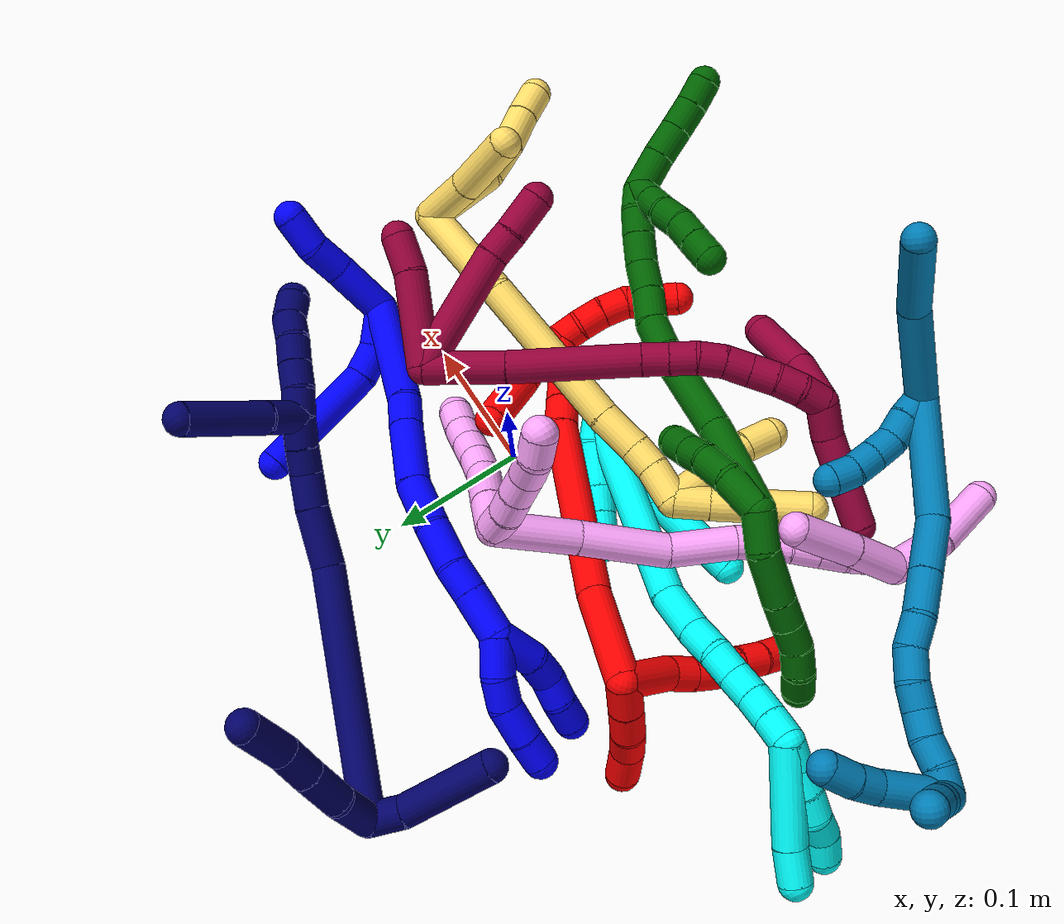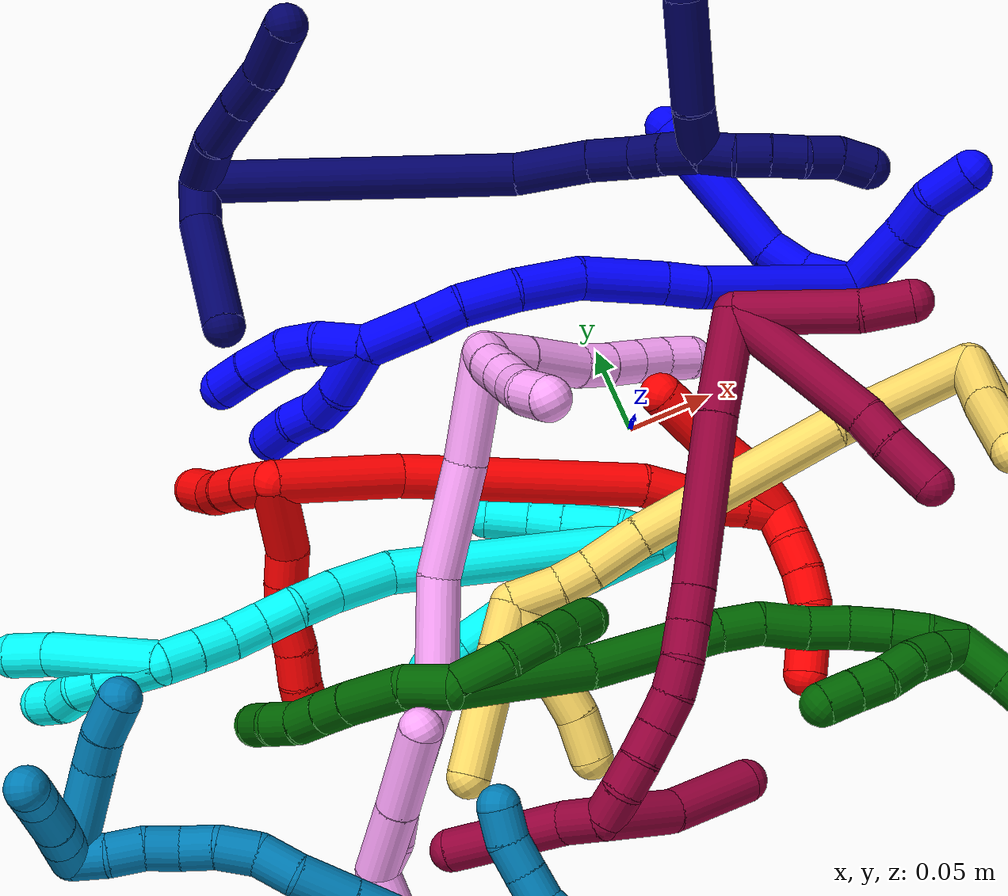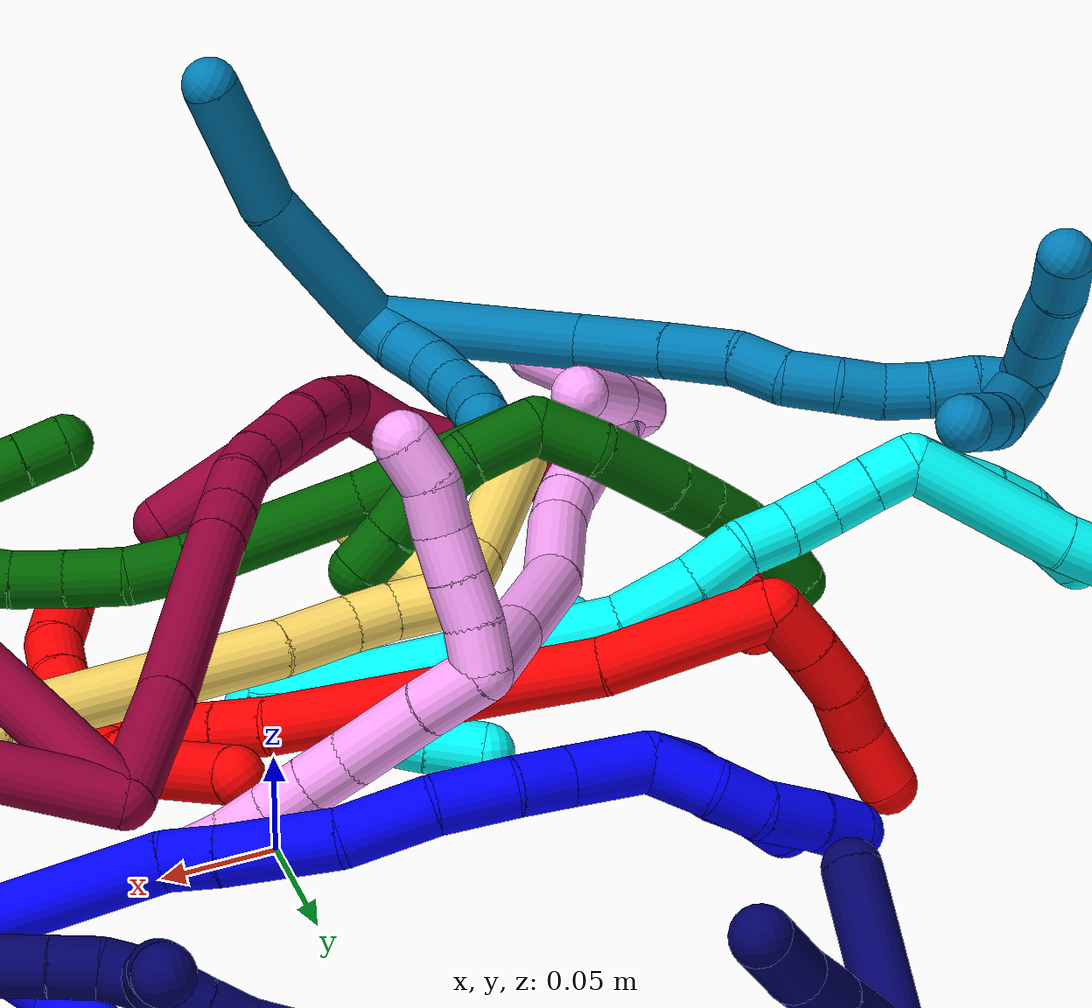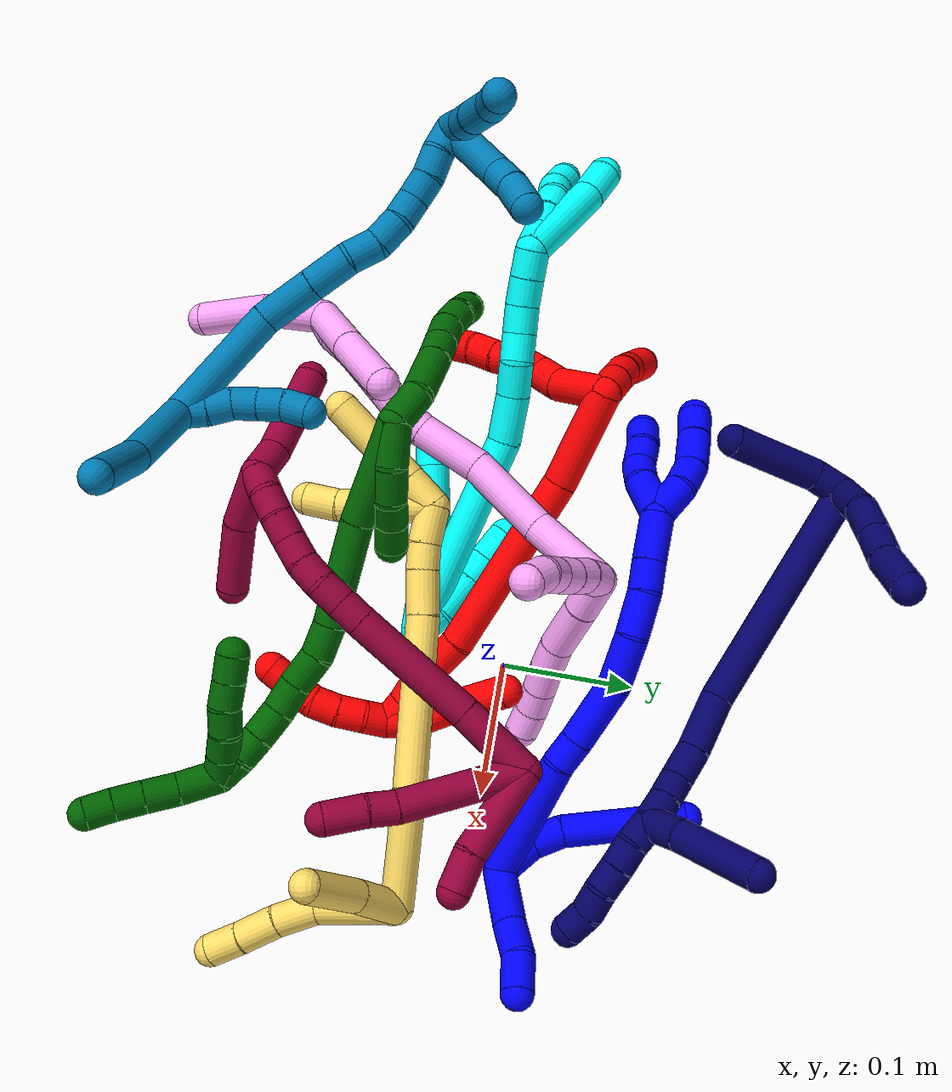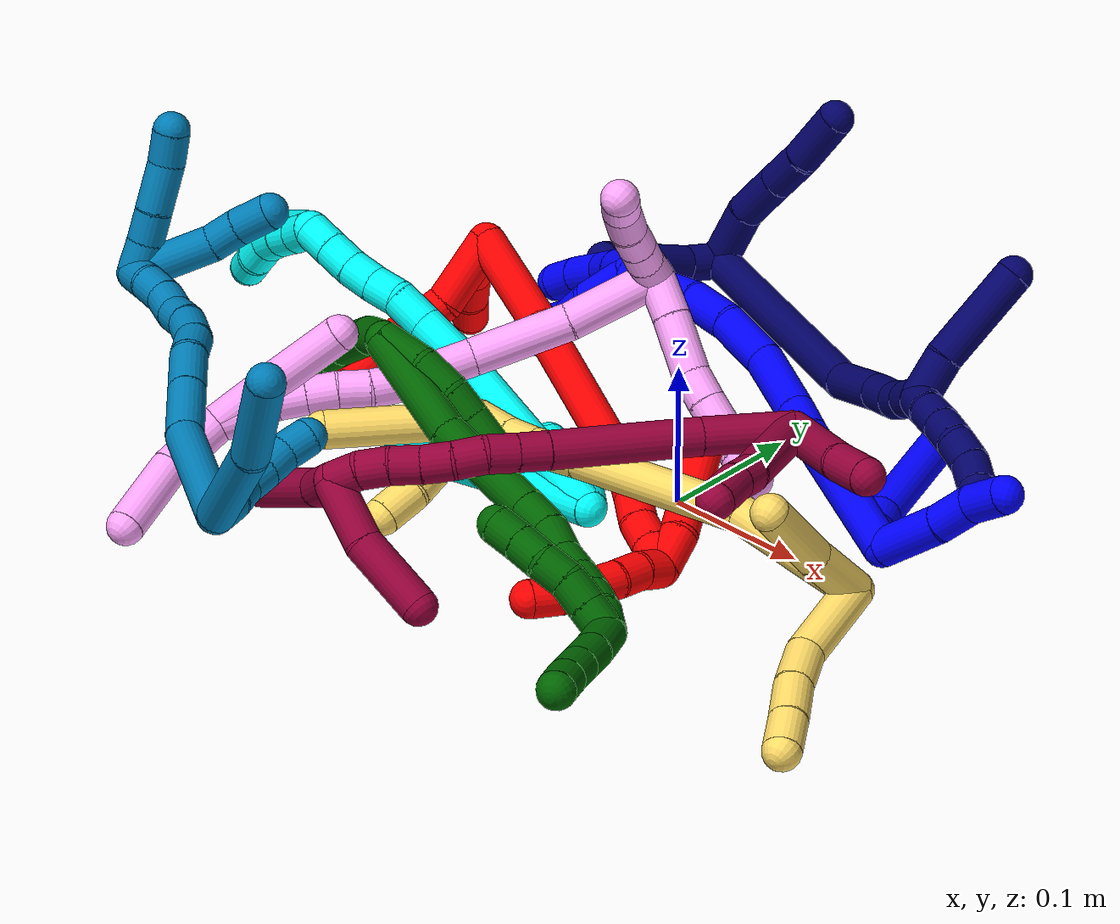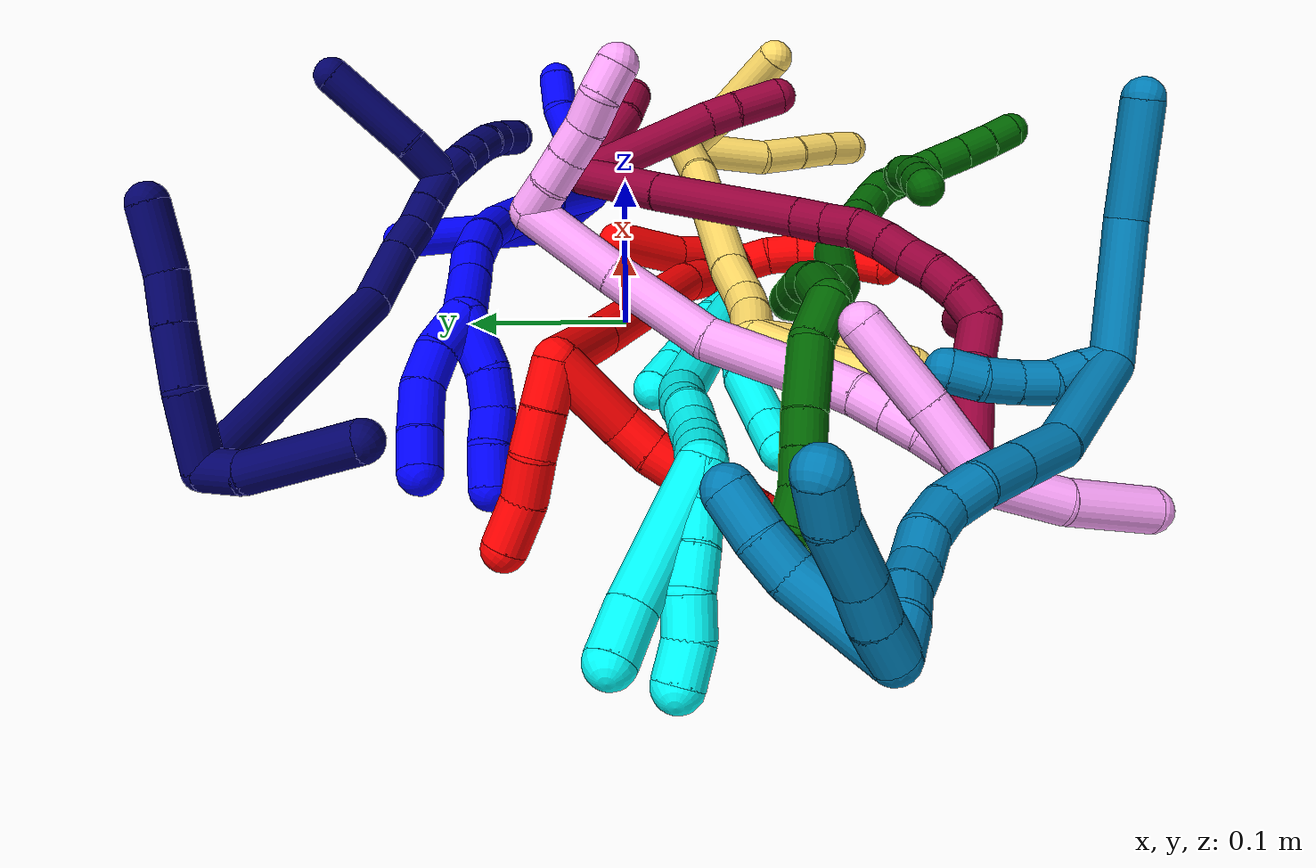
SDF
<sdf version="1.7">
 <world name="default">
  <plugin name="TubeGeneratorPlugin" filename="libtube_generator_plugin.so"/>
  <model name="photoneo_s_sensor">
   <static>1</static>
   <pose>0 0 2 1.57079 1.57079 3.14159</pose>
   <link name="link">
    <inertial><mass>0.1</mass></inertial>
    <sensor name="sensor" type="depth">
     <update_rate>30</update_rate>
     <camera>
      <horizontal_fov>1.22</horizontal_fov>
      <image><width>1920</width><height>1200</height><format>B8G8R8</format></image>
      <clip><near>0.1</near><far>4</far></clip>
      <depth_camera><output>points</output></depth_camera>
     </camera>
     <plugin name="camera_plugin" filename="libgazebo_ros_depth_camera.so">
      <baseline>0.2</baseline>
      <alwaysOn>1</alwaysOn>
      <updateRate>0.0</updateRate>
      <cameraName>camera_ir</cameraName>
      <imageTopicName>/camera/color/image_raw</imageTopicName>
      <cameraInfoTopicName>/camera/color/camera_info</cameraInfoTopicName>
      <depthImageTopicName>/camera/depth/image_raw</depthImageTopicName>
      <depthImageCameraInfoTopicName>/camera/depth/camera_info</depthImageCameraInfoTopicName>
      <pointCloudTopicName>/camera/depth/points</pointCloudTopicName>
      <frameName>fr_optical</frameName>
      <pointCloudCutoff>0.1</pointCloudCutoff>
      <pointCloudCutoffMax>2.0</pointCloudCutoffMax>
      <distortionK1>0</distortionK1>
      <distortionK2>0</distortionK2>
      <distortionK3>0</distortionK3>
      <distortionT1>0</distortionT1>
      <distortionT2>0</distortionT2>
      <CxPrime>0</CxPrime>
      <Cx>0</Cx>
      <Cy>0</Cy>
      <focalLength>0</focalLength>
      <hackBaseline>0</hackBaseline>
     </plugin>
    </sensor>
   </link>
  </model>
  <gravity>0 0 -9.8</gravity>
  <magnetic_field>6e-06 2.3e-05 -4.2e-05</magnetic_field>
  <atmosphere type="adiabatic"/>
  <physics name="default_physics" default="0" type="ode">
   <max_step_size>0.003</max_step_size>
   <real_time_factor>1</real_time_factor>
   <real_time_update_rate>1000</real_time_update_rate>
   <max_contacts>10000</max_contacts>
   <ode>
    <solver>
     <type>quick</type>
     <iters>100</iters>
     <sor>1.3</sor>
     <use_dynamic_moi_rescaling>0</use_dynamic_moi_rescaling>
    </solver>
    <constraints>
     <contact_max_correcting_vel>0</contact_max_correcting_vel>
     <contact_surface_layer>0.001</contact_surface_layer>
     <cfm>0</cfm>
     <erp>0.2</erp>
    </constraints>
   </ode>
  </physics>
  <scene><ambient>0.4 0.4 0.4 1</ambient><background>0.7 0.7 0.7 1</background><shadows>0</shadows></scene>
  <audio><device>default</device></audio>
  <spherical_coordinates>
   <surface_model>EARTH_WGS84</surface_model>
   <latitude_deg>0</latitude_deg>
   <longitude_deg>0</longitude_deg>
   <elevation>0</elevation>
   <heading_deg>0</heading_deg>
  </spherical_coordinates>
  <model name="bin">
   <static>1</static>
   <link name="bottom">
    <collision name="collision-bottom">
     <pose>0 0 -0.01 0 -0 0</pose>
     <geometry><box><size>0.8 0.6 0.02</size></box></geometry>
     <surface>
      <friction><ode><mu>100</mu><mu2>100</mu2></ode></friction>
      <contact><collide_bitmask>65535</collide_bitmask></contact>
     </surface>
    </collision>
   </link>
   <link name="west_wall">
    <collision name="collision-west_wall">
     <pose>-0.41 0 0.1 0 -0 0</pose>
     <geometry><box><size>0.02 0.6 0.2</size></box></geometry>
     <surface>
      <friction><ode><mu>100</mu><mu2>100</mu2></ode></friction>
      <contact><collide_bitmask>65535</collide_bitmask></contact>
     </surface>
    </collision>
   </link>
   <link name="east_wall">
    <collision name="collision-east_wall">
     <pose>0.41 0 0.1 0 -0 0</pose>
     <geometry><box><size>0.02 0.6 0.2</size></box></geometry>
     <surface>
      <friction><ode><mu>100</mu><mu2>100</mu2></ode></friction>
      <contact><collide_bitmask>65535</collide_bitmask></contact>
     </surface>
    </collision>
   </link>
   <link name="south_wall">
    <collision name="collision-south_wall">
     <pose>0 -0.31 0.1 0 -0 0</pose>
     <geometry><box><size>0.8 0.02 0.2</size></box></geometry>
     <surface>
      <friction><ode><mu>100</mu><mu2>100</mu2></ode></friction>
      <contact><collide_bitmask>65535</collide_bitmask></contact>
     </surface>
    </collision>
   </link>
   <link name="north_wall">
    <collision name="collision-north_wall">
     <pose>0 0.31 0.1 0 -0 0</pose>
     <geometry><box><size>0.8 0.02 0.2</size></box></geometry>
     <surface>
      <friction><ode><mu>100</mu><mu2>100</mu2></ode></friction>
      <contact><collide_bitmask>65535</collide_bitmask></contact>
     </surface>
    </collision>
   </link>
  </model>
  <model name="1">
   <static>0</static>
   <link name="1">
    <collision name="collision-cylinder-e_1_2_8">
     <pose>-0.007301 0.012135 0.006758 -1.06266 -0.483973 0.28811</pose>
     <geometry><cylinder><radius>0.0125</radius><length>0.031383</length></cylinder></geometry>
     <surface>
      <friction><ode><mu>1.16</mu><mu2>1.16</mu2><slip1>0</slip1><slip2>0</slip2></ode></friction>
      <contact><ode><kp>1e+06</kp><kd>1</kd><max_vel>0</max_vel><min_depth>0.001</min_depth></ode></contact>
     </surface>
    </collision>
    <visual name="visual-cylinder-e_1_2_8">
     <pose>-0.007301 0.012135 0.006758 -1.06266 -0.483973 0.28811</pose>
     <geometry><cylinder><radius>0.0125</radius><length>0.031383</length></cylinder></geometry>
     <material><ambient>0 0 1 1</ambient></material>
    </visual>
    <collision name="collision-cylinder-e_2_8_9">
     <pose>-0.019716 0.035585 0.015229 -1.42053 -0.420212 0.362759</pose>
     <geometry><cylinder><radius>0.0125</radius><length>0.02507</length></cylinder></geometry>
     <surface>
      <friction><ode><mu>1.16</mu><mu2>1.16</mu2><slip1>0</slip1><slip2>0</slip2></ode></friction>
      <contact><ode><kp>1e+06</kp><kd>1</kd><max_vel>0</max_vel><min_depth>0.001</min_depth></ode></contact>
     </surface>
    </collision>
    <visual name="visual-cylinder-e_2_8_9">
     <pose>-0.019716 0.035585 0.015229 -1.42053 -0.420212 0.362759</pose>
     <geometry><cylinder><radius>0.0125</radius><length>0.02507</length></cylinder></geometry>
     <material><ambient>0 0 1 1</ambient></material>
    </visual>
    <collision name="collision-cylinder-e_3_9_6">
     <pose>-0.03592 0.092064 0.011946 -1.68097 -0.239381 0.267008</pose>
     <geometry><cylinder><radius>0.0125</radius><length>0.093547</length></cylinder></geometry>
     <surface>
      <friction><ode><mu>1.16</mu><mu2>1.16</mu2><slip1>0</slip1><slip2>0</slip2></ode></friction>
      <contact><ode><kp>1e+06</kp><kd>1</kd><max_vel>0</max_vel><min_depth>0.001</min_depth></ode></contact>
     </surface>
    </collision>
    <visual name="visual-cylinder-e_3_9_6">
     <pose>-0.03592 0.092064 0.011946 -1.68097 -0.239381 0.267008</pose>
     <geometry><cylinder><radius>0.0125</radius><length>0.093547</length></cylinder></geometry>
     <material><ambient>0 0 1 1</ambient></material>
    </visual>
    <collision name="collision-cylinder-e_1_2_10">
     <pose>0.013574 0.003834 -0.017784 -2.92926 0.641048 -2.52034</pose>
     <geometry><cylinder><radius>0.0125</radius><length>0.045397</length></cylinder></geometry>
     <surface>
      <friction><ode><mu>1.16</mu><mu2>1.16</mu2><slip1>0</slip1><slip2>0</slip2></ode></friction>
      <contact><ode><kp>1e+06</kp><kd>1</kd><max_vel>0</max_vel><min_depth>0.001</min_depth></ode></contact>
     </surface>
    </collision>
    <visual name="visual-cylinder-e_1_2_10">
     <pose>0.013574 0.003834 -0.017784 -2.92926 0.641048 -2.52034</pose>
     <geometry><cylinder><radius>0.0125</radius><length>0.045397</length></cylinder></geometry>
     <material><ambient>0 0 1 1</ambient></material>
    </visual>
    <collision name="collision-cylinder-e_2_10_11">
     <pose>0.035916 0.011149 -0.045044 -2.78958 0.71503 -2.25294</pose>
     <geometry><cylinder><radius>0.0125</radius><length>0.026743</length></cylinder></geometry>
     <surface>
      <friction><ode><mu>1.16</mu><mu2>1.16</mu2><slip1>0</slip1><slip2>0</slip2></ode></friction>
      <contact><ode><kp>1e+06</kp><kd>1</kd><max_vel>0</max_vel><min_depth>0.001</min_depth></ode></contact>
     </surface>
    </collision>
    <visual name="visual-cylinder-e_2_10_11">
     <pose>0.035916 0.011149 -0.045044 -2.78958 0.71503 -2.25294</pose>
     <geometry><cylinder><radius>0.0125</radius><length>0.026743</length></cylinder></geometry>
     <material><ambient>0 0 1 1</ambient></material>
    </visual>
    <collision name="collision-cylinder-e_3_11_5">
     <pose>0.053332 0.014102 -0.065428 3.09325 0.669907 3.00289</pose>
     <geometry><cylinder><radius>0.0125</radius><length>0.027861</length></cylinder></geometry>
     <surface>
      <friction><ode><mu>1.16</mu><mu2>1.16</mu2><slip1>0</slip1><slip2>0</slip2></ode></friction>
      <contact><ode><kp>1e+06</kp><kd>1</kd><max_vel>0</max_vel><min_depth>0.001</min_depth></ode></contact>
     </surface>
    </collision>
    <visual name="visual-cylinder-e_3_11_5">
     <pose>0.053332 0.014102 -0.065428 3.09325 0.669907 3.00289</pose>
     <geometry><cylinder><radius>0.0125</radius><length>0.027861</length></cylinder></geometry>
     <material><ambient>0 0 1 1</ambient></material>
    </visual>
    <collision name="collision-cylinder-e_1_2_12">
     <pose>0.006334 0.032826 0.03586 -0.741253 0.129558 -0.050404</pose>
     <geometry><cylinder><radius>0.0125</radius><length>0.098052</length></cylinder></geometry>
     <surface>
      <friction><ode><mu>1.16</mu><mu2>1.16</mu2><slip1>0</slip1><slip2>0</slip2></ode></friction>
      <contact><ode><kp>1e+06</kp><kd>1</kd><max_vel>0</max_vel><min_depth>0.001</min_depth></ode></contact>
     </surface>
    </collision>
    <visual name="visual-cylinder-e_1_2_12">
     <pose>0.006334 0.032826 0.03586 -0.741253 0.129558 -0.050404</pose>
     <geometry><cylinder><radius>0.0125</radius><length>0.098052</length></cylinder></geometry>
     <material><ambient>0 0 1 1</ambient></material>
    </visual>
    <collision name="collision-cylinder-e_2_12_13">
     <pose>0.012001 0.074318 0.079037 -0.8696 -0.058681 0.02726</pose>
     <geometry><cylinder><radius>0.0125</radius><length>0.022726</length></cylinder></geometry>
     <surface>
      <friction><ode><mu>1.16</mu><mu2>1.16</mu2><slip1>0</slip1><slip2>0</slip2></ode></friction>
      <contact><ode><kp>1e+06</kp><kd>1</kd><max_vel>0</max_vel><min_depth>0.001</min_depth></ode></contact>
     </surface>
    </collision>
    <visual name="visual-cylinder-e_2_12_13">
     <pose>0.012001 0.074318 0.079037 -0.8696 -0.058681 0.02726</pose>
     <geometry><cylinder><radius>0.0125</radius><length>0.022726</length></cylinder></geometry>
     <material><ambient>0 0 1 1</ambient></material>
    </visual>
    <collision name="collision-cylinder-e_3_13_14">
     <pose>0.010867 0.101003 0.103272 -0.8169 -0.018948 0.008201</pose>
     <geometry><cylinder><radius>0.0125</radius><length>0.049437</length></cylinder></geometry>
     <surface>
      <friction><ode><mu>1.16</mu><mu2>1.16</mu2><slip1>0</slip1><slip2>0</slip2></ode></friction>
      <contact><ode><kp>1e+06</kp><kd>1</kd><max_vel>0</max_vel><min_depth>0.001</min_depth></ode></contact>
     </surface>
    </collision>
    <visual name="visual-cylinder-e_3_13_14">
     <pose>0.010867 0.101003 0.103272 -0.8169 -0.018948 0.008201</pose>
     <geometry><cylinder><radius>0.0125</radius><length>0.049437</length></cylinder></geometry>
     <material><ambient>0 0 1 1</ambient></material>
    </visual>
    <collision name="collision-cylinder-e_4_14_15">
     <pose>0.011699 0.129626 0.136466 -0.57745 0.066844 -0.019861</pose>
     <geometry><cylinder><radius>0.0125</radius><length>0.038944</length></cylinder></geometry>
     <surface>
      <friction><ode><mu>1.16</mu><mu2>1.16</mu2><slip1>0</slip1><slip2>0</slip2></ode></friction>
      <contact><ode><kp>1e+06</kp><kd>1</kd><max_vel>0</max_vel><min_depth>0.001</min_depth></ode></contact>
     </surface>
    </collision>
    <visual name="visual-cylinder-e_4_14_15">
     <pose>0.011699 0.129626 0.136466 -0.57745 0.066844 -0.019861</pose>
     <geometry><cylinder><radius>0.0125</radius><length>0.038944</length></cylinder></geometry>
     <material><ambient>0 0 1 1</ambient></material>
    </visual>
    <collision name="collision-cylinder-e_5_15_16">
     <pose>0.01113 0.147863 0.167153 -0.487083 -0.114185 0.028401</pose>
     <geometry><cylinder><radius>0.0125</radius><length>0.032822</length></cylinder></geometry>
     <surface>
      <friction><ode><mu>1.16</mu><mu2>1.16</mu2><slip1>0</slip1><slip2>0</slip2></ode></friction>
      <contact><ode><kp>1e+06</kp><kd>1</kd><max_vel>0</max_vel><min_depth>0.001</min_depth></ode></contact>
     </surface>
    </collision>
    <visual name="visual-cylinder-e_5_15_16">
     <pose>0.01113 0.147863 0.167153 -0.487083 -0.114185 0.028401</pose>
     <geometry><cylinder><radius>0.0125</radius><length>0.032822</length></cylinder></geometry>
     <material><ambient>0 0 1 1</ambient></material>
    </visual>
    <collision name="collision-cylinder-e_6_16_17">
     <pose>0.006647 0.159038 0.192045 -0.325997 -0.231866 0.038299</pose>
     <geometry><cylinder><radius>0.0125</radius><length>0.022743</length></cylinder></geometry>
     <surface>
      <friction><ode><mu>1.16</mu><mu2>1.16</mu2><slip1>0</slip1><slip2>0</slip2></ode></friction>
      <contact><ode><kp>1e+06</kp><kd>1</kd><max_vel>0</max_vel><min_depth>0.001</min_depth></ode></contact>
     </surface>
    </collision>
    <visual name="visual-cylinder-e_6_16_17">
     <pose>0.006647 0.159038 0.192045 -0.325997 -0.231866 0.038299</pose>
     <geometry><cylinder><radius>0.0125</radius><length>0.022743</length></cylinder></geometry>
     <material><ambient>0 0 1 1</ambient></material>
    </visual>
    <collision name="collision-cylinder-e_7_17_1">
     <pose>0.000151 0.168633 0.218635 -0.359373 -0.221961 0.040479</pose>
     <geometry><cylinder><radius>0.0125</radius><length>0.035276</length></cylinder></geometry>
     <surface>
      <friction><ode><mu>1.16</mu><mu2>1.16</mu2><slip1>0</slip1><slip2>0</slip2></ode></friction>
      <contact><ode><kp>1e+06</kp><kd>1</kd><max_vel>0</max_vel><min_depth>0.001</min_depth></ode></contact>
     </surface>
    </collision>
    <visual name="visual-cylinder-e_7_17_1">
     <pose>0.000151 0.168633 0.218635 -0.359373 -0.221961 0.040479</pose>
     <geometry><cylinder><radius>0.0125</radius><length>0.035276</length></cylinder></geometry>
     <material><ambient>0 0 1 1</ambient></material>
    </visual>
    <collision name="collision-cylinder-e_1_1_18">
     <pose>-0.011754 0.183383 0.242119 -0.867415 -0.612962 0.291036</pose>
     <geometry><cylinder><radius>0.0125</radius><length>0.027889</length></cylinder></geometry>
     <surface>
      <friction><ode><mu>1.16</mu><mu2>1.16</mu2><slip1>0</slip1><slip2>0</slip2></ode></friction>
      <contact><ode><kp>1e+06</kp><kd>1</kd><max_vel>0</max_vel><min_depth>0.001</min_depth></ode></contact>
     </surface>
    </collision>
    <visual name="visual-cylinder-e_1_1_18">
     <pose>-0.011754 0.183383 0.242119 -0.867415 -0.612962 0.291036</pose>
     <geometry><cylinder><radius>0.0125</radius><length>0.027889</length></cylinder></geometry>
     <material><ambient>0 0 1 1</ambient></material>
    </visual>
    <collision name="collision-cylinder-e_2_18_19">
     <pose>-0.027663 0.19649 0.256259 -0.577588 -0.773745 0.240907</pose>
     <geometry><cylinder><radius>0.0125</radius><length>0.022572</length></cylinder></geometry>
     <surface>
      <friction><ode><mu>1.16</mu><mu2>1.16</mu2><slip1>0</slip1><slip2>0</slip2></ode></friction>
      <contact><ode><kp>1e+06</kp><kd>1</kd><max_vel>0</max_vel><min_depth>0.001</min_depth></ode></contact>
     </surface>
    </collision>
    <visual name="visual-cylinder-e_2_18_19">
     <pose>-0.027663 0.19649 0.256259 -0.577588 -0.773745 0.240907</pose>
     <geometry><cylinder><radius>0.0125</radius><length>0.022572</length></cylinder></geometry>
     <material><ambient>0 0 1 1</ambient></material>
    </visual>
    <collision name="collision-cylinder-e_3_19_20">
     <pose>-0.043843 0.203207 0.274025 -0.206874 -0.635594 0.068268</pose>
     <geometry><cylinder><radius>0.0125</radius><length>0.02794</length></cylinder></geometry>
     <surface>
      <friction><ode><mu>1.16</mu><mu2>1.16</mu2><slip1>0</slip1><slip2>0</slip2></ode></friction>
      <contact><ode><kp>1e+06</kp><kd>1</kd><max_vel>0</max_vel><min_depth>0.001</min_depth></ode></contact>
     </surface>
    </collision>
    <visual name="visual-cylinder-e_3_19_20">
     <pose>-0.043843 0.203207 0.274025 -0.206874 -0.635594 0.068268</pose>
     <geometry><cylinder><radius>0.0125</radius><length>0.02794</length></cylinder></geometry>
     <material><ambient>0 0 1 1</ambient></material>
    </visual>
    <collision name="collision-cylinder-e_4_20_4">
     <pose>-0.059024 0.206426 0.293295 -0.109652 -0.691616 0.03954</pose>
     <geometry><cylinder><radius>0.0125</radius><length>0.021599</length></cylinder></geometry>
     <surface>
      <friction><ode><mu>1.16</mu><mu2>1.16</mu2><slip1>0</slip1><slip2>0</slip2></ode></friction>
      <contact><ode><kp>1e+06</kp><kd>1</kd><max_vel>0</max_vel><min_depth>0.001</min_depth></ode></contact>
     </surface>
    </collision>
    <visual name="visual-cylinder-e_4_20_4">
     <pose>-0.059024 0.206426 0.293295 -0.109652 -0.691616 0.03954</pose>
     <geometry><cylinder><radius>0.0125</radius><length>0.021599</length></cylinder></geometry>
     <material><ambient>0 0 1 1</ambient></material>
    </visual>
    <collision name="collision-cylinder-e_1_1_21">
     <pose>-0.014641 0.169456 0.247216 0.396897 -0.678701 -0.141738</pose>
     <geometry><cylinder><radius>0.0125</radius><length>0.034754</length></cylinder></geometry>
     <surface>
      <friction><ode><mu>1.16</mu><mu2>1.16</mu2><slip1>0</slip1><slip2>0</slip2></ode></friction>
      <contact><ode><kp>1e+06</kp><kd>1</kd><max_vel>0</max_vel><min_depth>0.001</min_depth></ode></contact>
     </surface>
    </collision>
    <visual name="visual-cylinder-e_1_1_21">
     <pose>-0.014641 0.169456 0.247216 0.396897 -0.678701 -0.141738</pose>
     <geometry><cylinder><radius>0.0125</radius><length>0.034754</length></cylinder></geometry>
     <material><ambient>0 0 1 1</ambient></material>
    </visual>
    <collision name="collision-cylinder-e_2_21_22">
     <pose>-0.034362 0.162835 0.266318 0.207103 -0.915606 -0.10232</pose>
     <geometry><cylinder><radius>0.0125</radius><length>0.022228</length></cylinder></geometry>
     <surface>
      <friction><ode><mu>1.16</mu><mu2>1.16</mu2><slip1>0</slip1><slip2>0</slip2></ode></friction>
      <contact><ode><kp>1e+06</kp><kd>1</kd><max_vel>0</max_vel><min_depth>0.001</min_depth></ode></contact>
     </surface>
    </collision>
    <visual name="visual-cylinder-e_2_21_22">
     <pose>-0.034362 0.162835 0.266318 0.207103 -0.915606 -0.10232</pose>
     <geometry><cylinder><radius>0.0125</radius><length>0.022228</length></cylinder></geometry>
     <material><ambient>0 0 1 1</ambient></material>
    </visual>
    <collision name="collision-cylinder-e_3_22_23">
     <pose>-0.050126 0.163269 0.279925 -0.255973 -0.766799 0.103724</pose>
     <geometry><cylinder><radius>0.0125</radius><length>0.020037</length></cylinder></geometry>
     <surface>
      <friction><ode><mu>1.16</mu><mu2>1.16</mu2><slip1>0</slip1><slip2>0</slip2></ode></friction>
      <contact><ode><kp>1e+06</kp><kd>1</kd><max_vel>0</max_vel><min_depth>0.001</min_depth></ode></contact>
     </surface>
    </collision>
    <visual name="visual-cylinder-e_3_22_23">
     <pose>-0.050126 0.163269 0.279925 -0.255973 -0.766799 0.103724</pose>
     <geometry><cylinder><radius>0.0125</radius><length>0.020037</length></cylinder></geometry>
     <material><ambient>0 0 1 1</ambient></material>
    </visual>
    <collision name="collision-cylinder-e_4_23_3">
     <pose>-0.066326 0.164938 0.293722 0.023146 -0.935395 -0.011691</pose>
     <geometry><cylinder><radius>0.0125</radius><length>0.022981</length></cylinder></geometry>
     <surface>
      <friction><ode><mu>1.16</mu><mu2>1.16</mu2><slip1>0</slip1><slip2>0</slip2></ode></friction>
      <contact><ode><kp>1e+06</kp><kd>1</kd><max_vel>0</max_vel><min_depth>0.001</min_depth></ode></contact>
     </surface>
    </collision>
    <visual name="visual-cylinder-e_4_23_3">
     <pose>-0.066326 0.164938 0.293722 0.023146 -0.935395 -0.011691</pose>
     <geometry><cylinder><radius>0.0125</radius><length>0.022981</length></cylinder></geometry>
     <material><ambient>0 0 1 1</ambient></material>
    </visual>
    <collision name="collision-sphere-3">
     <pose>-0.075574 0.16478 0.30054 0 -0 0</pose>
     <geometry><sphere><radius>0.0125</radius></sphere></geometry>
     <surface>
      <friction><ode><mu>1.16</mu><mu2>1.16</mu2><slip1>0</slip1><slip2>0</slip2></ode></friction>
      <contact><ode><kp>1e+06</kp><kd>1</kd><max_vel>0</max_vel><min_depth>0.001</min_depth></ode></contact>
     </surface>
    </collision>
    <visual name="visual-sphere-3">
     <pose>-0.075574 0.16478 0.30054 0 -0 0</pose>
     <geometry><sphere><radius>0.0125</radius></sphere></geometry>
     <material><ambient>0 0 1 1</ambient></material>
    </visual>
    <collision name="collision-sphere-23">
     <pose>-0.057078 0.165096 0.286904 0 -0 0</pose>
     <geometry><sphere><radius>0.0125</radius></sphere></geometry>
     <surface>
      <friction><ode><mu>1.16</mu><mu2>1.16</mu2><slip1>0</slip1><slip2>0</slip2></ode></friction>
      <contact><ode><kp>1e+06</kp><kd>1</kd><max_vel>0</max_vel><min_depth>0.001</min_depth></ode></contact>
     </surface>
    </collision>
    <visual name="visual-sphere-23">
     <pose>-0.057078 0.165096 0.286904 0 -0 0</pose>
     <geometry><sphere><radius>0.0125</radius></sphere></geometry>
     <material><ambient>0 0 1 1</ambient></material>
    </visual>
    <collision name="collision-sphere-22">
     <pose>-0.043175 0.161442 0.272945 0 -0 0</pose>
     <geometry><sphere><radius>0.0125</radius></sphere></geometry>
     <surface>
      <friction><ode><mu>1.16</mu><mu2>1.16</mu2><slip1>0</slip1><slip2>0</slip2></ode></friction>
      <contact><ode><kp>1e+06</kp><kd>1</kd><max_vel>0</max_vel><min_depth>0.001</min_depth></ode></contact>
     </surface>
    </collision>
    <visual name="visual-sphere-22">
     <pose>-0.043175 0.161442 0.272945 0 -0 0</pose>
     <geometry><sphere><radius>0.0125</radius></sphere></geometry>
     <material><ambient>0 0 1 1</ambient></material>
    </visual>
    <collision name="collision-sphere-21">
     <pose>-0.02555 0.164227 0.259691 0 -0 0</pose>
     <geometry><sphere><radius>0.0125</radius></sphere></geometry>
     <surface>
      <friction><ode><mu>1.16</mu><mu2>1.16</mu2><slip1>0</slip1><slip2>0</slip2></ode></friction>
      <contact><ode><kp>1e+06</kp><kd>1</kd><max_vel>0</max_vel><min_depth>0.001</min_depth></ode></contact>
     </surface>
    </collision>
    <visual name="visual-sphere-21">
     <pose>-0.02555 0.164227 0.259691 0 -0 0</pose>
     <geometry><sphere><radius>0.0125</radius></sphere></geometry>
     <material><ambient>0 0 1 1</ambient></material>
    </visual>
    <collision name="collision-sphere-4">
     <pose>-0.065912 0.207336 0.301563 0 -0 0</pose>
     <geometry><sphere><radius>0.0125</radius></sphere></geometry>
     <surface>
      <friction><ode><mu>1.16</mu><mu2>1.16</mu2><slip1>0</slip1><slip2>0</slip2></ode></friction>
      <contact><ode><kp>1e+06</kp><kd>1</kd><max_vel>0</max_vel><min_depth>0.001</min_depth></ode></contact>
     </surface>
    </collision>
    <visual name="visual-sphere-4">
     <pose>-0.065912 0.207336 0.301563 0 -0 0</pose>
     <geometry><sphere><radius>0.0125</radius></sphere></geometry>
     <material><ambient>0 0 1 1</ambient></material>
    </visual>
    <collision name="collision-sphere-20">
     <pose>-0.052137 0.205516 0.285027 0 -0 0</pose>
     <geometry><sphere><radius>0.0125</radius></sphere></geometry>
     <surface>
      <friction><ode><mu>1.16</mu><mu2>1.16</mu2><slip1>0</slip1><slip2>0</slip2></ode></friction>
      <contact><ode><kp>1e+06</kp><kd>1</kd><max_vel>0</max_vel><min_depth>0.001</min_depth></ode></contact>
     </surface>
    </collision>
    <visual name="visual-sphere-20">
     <pose>-0.052137 0.205516 0.285027 0 -0 0</pose>
     <geometry><sphere><radius>0.0125</radius></sphere></geometry>
     <material><ambient>0 0 1 1</ambient></material>
    </visual>
    <collision name="collision-sphere-11">
     <pose>0.044682 0.01463 -0.054521 0 -0 0</pose>
     <geometry><sphere><radius>0.0125</radius></sphere></geometry>
     <surface>
      <friction><ode><mu>1.16</mu><mu2>1.16</mu2><slip1>0</slip1><slip2>0</slip2></ode></friction>
      <contact><ode><kp>1e+06</kp><kd>1</kd><max_vel>0</max_vel><min_depth>0.001</min_depth></ode></contact>
     </surface>
    </collision>
    <visual name="visual-sphere-11">
     <pose>0.044682 0.01463 -0.054521 0 -0 0</pose>
     <geometry><sphere><radius>0.0125</radius></sphere></geometry>
     <material><ambient>0 0 1 1</ambient></material>
    </visual>
    <collision name="collision-sphere-10">
     <pose>0.027149 0.007668 -0.035567 0 -0 0</pose>
     <geometry><sphere><radius>0.0125</radius></sphere></geometry>
     <surface>
      <friction><ode><mu>1.16</mu><mu2>1.16</mu2><slip1>0</slip1><slip2>0</slip2></ode></friction>
      <contact><ode><kp>1e+06</kp><kd>1</kd><max_vel>0</max_vel><min_depth>0.001</min_depth></ode></contact>
     </surface>
    </collision>
    <visual name="visual-sphere-10">
     <pose>0.027149 0.007668 -0.035567 0 -0 0</pose>
     <geometry><sphere><radius>0.0125</radius></sphere></geometry>
     <material><ambient>0 0 1 1</ambient></material>
    </visual>
    <collision name="collision-sphere-6">
     <pose>-0.04701 0.137229 0.00695 0 -0 0</pose>
     <geometry><sphere><radius>0.0125</radius></sphere></geometry>
     <surface>
      <friction><ode><mu>1.16</mu><mu2>1.16</mu2><slip1>0</slip1><slip2>0</slip2></ode></friction>
      <contact><ode><kp>1e+06</kp><kd>1</kd><max_vel>0</max_vel><min_depth>0.001</min_depth></ode></contact>
     </surface>
    </collision>
    <visual name="visual-sphere-6">
     <pose>-0.04701 0.137229 0.00695 0 -0 0</pose>
     <geometry><sphere><radius>0.0125</radius></sphere></geometry>
     <material><ambient>0 0 1 1</ambient></material>
    </visual>
    <collision name="collision-sphere-9">
     <pose>-0.02483 0.0469 0.016942 0 -0 0</pose>
     <geometry><sphere><radius>0.0125</radius></sphere></geometry>
     <surface>
      <friction><ode><mu>1.16</mu><mu2>1.16</mu2><slip1>0</slip1><slip2>0</slip2></ode></friction>
      <contact><ode><kp>1e+06</kp><kd>1</kd><max_vel>0</max_vel><min_depth>0.001</min_depth></ode></contact>
     </surface>
    </collision>
    <visual name="visual-sphere-9">
     <pose>-0.02483 0.0469 0.016942 0 -0 0</pose>
     <geometry><sphere><radius>0.0125</radius></sphere></geometry>
     <material><ambient>0 0 1 1</ambient></material>
    </visual>
    <collision name="collision-sphere-2">
     <geometry><sphere><radius>0.0125</radius></sphere></geometry>
     <surface>
      <friction><ode><mu>1.16</mu><mu2>1.16</mu2><slip1>0</slip1><slip2>0</slip2></ode></friction>
      <contact><ode><kp>1e+06</kp><kd>1</kd><max_vel>0</max_vel><min_depth>0.001</min_depth></ode></contact>
     </surface>
    </collision>
    <visual name="visual-sphere-2">
     <geometry><sphere><radius>0.0125</radius></sphere></geometry>
     <material><ambient>0 0 1 1</ambient></material>
    </visual>
    <collision name="collision-sphere-19">
     <pose>-0.03555 0.200897 0.263023 0 -0 0</pose>
     <geometry><sphere><radius>0.0125</radius></sphere></geometry>
     <surface>
      <friction><ode><mu>1.16</mu><mu2>1.16</mu2><slip1>0</slip1><slip2>0</slip2></ode></friction>
      <contact><ode><kp>1e+06</kp><kd>1</kd><max_vel>0</max_vel><min_depth>0.001</min_depth></ode></contact>
     </surface>
    </collision>
    <visual name="visual-sphere-19">
     <pose>-0.03555 0.200897 0.263023 0 -0 0</pose>
     <geometry><sphere><radius>0.0125</radius></sphere></geometry>
     <material><ambient>0 0 1 1</ambient></material>
    </visual>
    <collision name="collision-sphere-8">
     <pose>-0.014603 0.024269 0.013516 0 -0 0</pose>
     <geometry><sphere><radius>0.0125</radius></sphere></geometry>
     <surface>
      <friction><ode><mu>1.16</mu><mu2>1.16</mu2><slip1>0</slip1><slip2>0</slip2></ode></friction>
      <contact><ode><kp>1e+06</kp><kd>1</kd><max_vel>0</max_vel><min_depth>0.001</min_depth></ode></contact>
     </surface>
    </collision>
    <visual name="visual-sphere-8">
     <pose>-0.014603 0.024269 0.013516 0 -0 0</pose>
     <geometry><sphere><radius>0.0125</radius></sphere></geometry>
     <material><ambient>0 0 1 1</ambient></material>
    </visual>
    <collision name="collision-sphere-5">
     <pose>0.061981 0.013574 -0.076335 0 -0 0</pose>
     <geometry><sphere><radius>0.0125</radius></sphere></geometry>
     <surface>
      <friction><ode><mu>1.16</mu><mu2>1.16</mu2><slip1>0</slip1><slip2>0</slip2></ode></friction>
      <contact><ode><kp>1e+06</kp><kd>1</kd><max_vel>0</max_vel><min_depth>0.001</min_depth></ode></contact>
     </surface>
    </collision>
    <visual name="visual-sphere-5">
     <pose>0.061981 0.013574 -0.076335 0 -0 0</pose>
     <geometry><sphere><radius>0.0125</radius></sphere></geometry>
     <material><ambient>0 0 1 1</ambient></material>
    </visual>
    <collision name="collision-sphere-12">
     <pose>0.012668 0.065651 0.071719 0 -0 0</pose>
     <geometry><sphere><radius>0.0125</radius></sphere></geometry>
     <surface>
      <friction><ode><mu>1.16</mu><mu2>1.16</mu2><slip1>0</slip1><slip2>0</slip2></ode></friction>
      <contact><ode><kp>1e+06</kp><kd>1</kd><max_vel>0</max_vel><min_depth>0.001</min_depth></ode></contact>
     </surface>
    </collision>
    <visual name="visual-sphere-12">
     <pose>0.012668 0.065651 0.071719 0 -0 0</pose>
     <geometry><sphere><radius>0.0125</radius></sphere></geometry>
     <material><ambient>0 0 1 1</ambient></material>
    </visual>
    <collision name="collision-sphere-13">
     <pose>0.011335 0.082985 0.086355 0 -0 0</pose>
     <geometry><sphere><radius>0.0125</radius></sphere></geometry>
     <surface>
      <friction><ode><mu>1.16</mu><mu2>1.16</mu2><slip1>0</slip1><slip2>0</slip2></ode></friction>
      <contact><ode><kp>1e+06</kp><kd>1</kd><max_vel>0</max_vel><min_depth>0.001</min_depth></ode></contact>
     </surface>
    </collision>
    <visual name="visual-sphere-13">
     <pose>0.011335 0.082985 0.086355 0 -0 0</pose>
     <geometry><sphere><radius>0.0125</radius></sphere></geometry>
     <material><ambient>0 0 1 1</ambient></material>
    </visual>
    <collision name="collision-sphere-14">
     <pose>0.010398 0.11902 0.120188 0 -0 0</pose>
     <geometry><sphere><radius>0.0125</radius></sphere></geometry>
     <surface>
      <friction><ode><mu>1.16</mu><mu2>1.16</mu2><slip1>0</slip1><slip2>0</slip2></ode></friction>
      <contact><ode><kp>1e+06</kp><kd>1</kd><max_vel>0</max_vel><min_depth>0.001</min_depth></ode></contact>
     </surface>
    </collision>
    <visual name="visual-sphere-14">
     <pose>0.010398 0.11902 0.120188 0 -0 0</pose>
     <geometry><sphere><radius>0.0125</radius></sphere></geometry>
     <material><ambient>0 0 1 1</ambient></material>
    </visual>
    <collision name="collision-sphere-15">
     <pose>0.013 0.140232 0.152745 0 -0 0</pose>
     <geometry><sphere><radius>0.0125</radius></sphere></geometry>
     <surface>
      <friction><ode><mu>1.16</mu><mu2>1.16</mu2><slip1>0</slip1><slip2>0</slip2></ode></friction>
      <contact><ode><kp>1e+06</kp><kd>1</kd><max_vel>0</max_vel><min_depth>0.001</min_depth></ode></contact>
     </surface>
    </collision>
    <visual name="visual-sphere-15">
     <pose>0.013 0.140232 0.152745 0 -0 0</pose>
     <geometry><sphere><radius>0.0125</radius></sphere></geometry>
     <material><ambient>0 0 1 1</ambient></material>
    </visual>
    <collision name="collision-sphere-16">
     <pose>0.00926 0.155494 0.181561 0 -0 0</pose>
     <geometry><sphere><radius>0.0125</radius></sphere></geometry>
     <surface>
      <friction><ode><mu>1.16</mu><mu2>1.16</mu2><slip1>0</slip1><slip2>0</slip2></ode></friction>
      <contact><ode><kp>1e+06</kp><kd>1</kd><max_vel>0</max_vel><min_depth>0.001</min_depth></ode></contact>
     </surface>
    </collision>
    <visual name="visual-sphere-16">
     <pose>0.00926 0.155494 0.181561 0 -0 0</pose>
     <geometry><sphere><radius>0.0125</radius></sphere></geometry>
     <material><ambient>0 0 1 1</ambient></material>
    </visual>
    <collision name="collision-sphere-17">
     <pose>0.004034 0.162582 0.202529 0 -0 0</pose>
     <geometry><sphere><radius>0.0125</radius></sphere></geometry>
     <surface>
      <friction><ode><mu>1.16</mu><mu2>1.16</mu2><slip1>0</slip1><slip2>0</slip2></ode></friction>
      <contact><ode><kp>1e+06</kp><kd>1</kd><max_vel>0</max_vel><min_depth>0.001</min_depth></ode></contact>
     </surface>
    </collision>
    <visual name="visual-sphere-17">
     <pose>0.004034 0.162582 0.202529 0 -0 0</pose>
     <geometry><sphere><radius>0.0125</radius></sphere></geometry>
     <material><ambient>0 0 1 1</ambient></material>
    </visual>
    <collision name="collision-sphere-1">
     <pose>-0.003732 0.174684 0.234742 0 -0 0</pose>
     <geometry><sphere><radius>0.0125</radius></sphere></geometry>
     <surface>
      <friction><ode><mu>1.16</mu><mu2>1.16</mu2><slip1>0</slip1><slip2>0</slip2></ode></friction>
      <contact><ode><kp>1e+06</kp><kd>1</kd><max_vel>0</max_vel><min_depth>0.001</min_depth></ode></contact>
     </surface>
    </collision>
    <visual name="visual-sphere-1">
     <pose>-0.003732 0.174684 0.234742 0 -0 0</pose>
     <geometry><sphere><radius>0.0125</radius></sphere></geometry>
     <material><ambient>0 0 1 1</ambient></material>
    </visual>
    <collision name="collision-sphere-18">
     <pose>-0.019776 0.192082 0.249496 0 -0 0</pose>
     <geometry><sphere><radius>0.0125</radius></sphere></geometry>
     <surface>
      <friction><ode><mu>1.16</mu><mu2>1.16</mu2><slip1>0</slip1><slip2>0</slip2></ode></friction>
      <contact><ode><kp>1e+06</kp><kd>1</kd><max_vel>0</max_vel><min_depth>0.001</min_depth></ode></contact>
     </surface>
    </collision>
    <visual name="visual-sphere-18">
     <pose>-0.019776 0.192082 0.249496 0 -0 0</pose>
     <geometry><sphere><radius>0.0125</radius></sphere></geometry>
     <material><ambient>0 0 1 1</ambient></material>
    </visual>
    <inertial>
     <pose>-0.007821 0.101833 0.112765 0 -0 0</pose>
     <mass>0.75</mass>
     <inertia>
      <ixx>0.000192</ixx>
      <ixy>0</ixy>
      <ixz>0</ixz>
      <iyy>0.000156</iyy>
      <iyz>0</iyz>
      <izz>-0.000114</izz>
     </inertia>
    </inertial>
   </link>
   <pose>0.151485 0.023321 0.020649 1.40403 -1.26954 -1.02157</pose>
  </model>
  <model name="2">
   <static>0</static>
   <link name="2">
    <collision name="collision-cylinder-e_1_2_8">
     <pose>0.00208 -0.023793 -0.00298 1.6954 0.086504 0.097998</pose>
     <geometry><cylinder><radius>0.0125</radius><length>0.048139</length></cylinder></geometry>
     <surface>
      <friction><ode><mu>1.16</mu><mu2>1.16</mu2><slip1>0</slip1><slip2>0</slip2></ode></friction>
      <contact><ode><kp>1e+06</kp><kd>1</kd><max_vel>0</max_vel><min_depth>0.001</min_depth></ode></contact>
     </surface>
    </collision>
    <visual name="visual-cylinder-e_1_2_8">
     <pose>0.00208 -0.023793 -0.00298 1.6954 0.086504 0.097998</pose>
     <geometry><cylinder><radius>0.0125</radius><length>0.048139</length></cylinder></geometry>
     <material><ambient>1 0 0 1</ambient></material>
    </visual>
    <collision name="collision-cylinder-e_2_8_9">
     <pose>0.001766 -0.057552 -0.006656 1.6405 -0.235102 -0.251916</pose>
     <geometry><cylinder><radius>0.0125</radius><length>0.020544</length></cylinder></geometry>
     <surface>
      <friction><ode><mu>1.16</mu><mu2>1.16</mu2><slip1>0</slip1><slip2>0</slip2></ode></friction>
      <contact><ode><kp>1e+06</kp><kd>1</kd><max_vel>0</max_vel><min_depth>0.001</min_depth></ode></contact>
     </surface>
    </collision>
    <visual name="visual-cylinder-e_2_8_9">
     <pose>0.001766 -0.057552 -0.006656 1.6405 -0.235102 -0.251916</pose>
     <geometry><cylinder><radius>0.0125</radius><length>0.020544</length></cylinder></geometry>
     <material><ambient>1 0 0 1</ambient></material>
    </visual>
    <collision name="collision-cylinder-e_3_9_10">
     <pose>-0.003175 -0.077394 -0.006435 1.47822 -0.251513 -0.229448</pose>
     <geometry><cylinder><radius>0.0125</radius><length>0.020483</length></cylinder></geometry>
     <surface>
      <friction><ode><mu>1.16</mu><mu2>1.16</mu2><slip1>0</slip1><slip2>0</slip2></ode></friction>
      <contact><ode><kp>1e+06</kp><kd>1</kd><max_vel>0</max_vel><min_depth>0.001</min_depth></ode></contact>
     </surface>
    </collision>
    <visual name="visual-cylinder-e_3_9_10">
     <pose>-0.003175 -0.077394 -0.006435 1.47822 -0.251513 -0.229448</pose>
     <geometry><cylinder><radius>0.0125</radius><length>0.020483</length></cylinder></geometry>
     <material><ambient>1 0 0 1</ambient></material>
    </visual>
    <collision name="collision-cylinder-e_4_10_11">
     <pose>-0.006007 -0.097222 -0.003644 1.38459 -0.027922 -0.023153</pose>
     <geometry><cylinder><radius>0.0125</radius><length>0.020259</length></cylinder></geometry>
     <surface>
      <friction><ode><mu>1.16</mu><mu2>1.16</mu2><slip1>0</slip1><slip2>0</slip2></ode></friction>
      <contact><ode><kp>1e+06</kp><kd>1</kd><max_vel>0</max_vel><min_depth>0.001</min_depth></ode></contact>
     </surface>
    </collision>
    <visual name="visual-cylinder-e_4_10_11">
     <pose>-0.006007 -0.097222 -0.003644 1.38459 -0.027922 -0.023153</pose>
     <geometry><cylinder><radius>0.0125</radius><length>0.020259</length></cylinder></geometry>
     <material><ambient>1 0 0 1</ambient></material>
    </visual>
    <collision name="collision-cylinder-e_5_11_12">
     <pose>-0.007744 -0.11729 -0.000705 1.46605 -0.141949 -0.127849</pose>
     <geometry><cylinder><radius>0.0125</radius><length>0.020553</length></cylinder></geometry>
     <surface>
      <friction><ode><mu>1.16</mu><mu2>1.16</mu2><slip1>0</slip1><slip2>0</slip2></ode></friction>
      <contact><ode><kp>1e+06</kp><kd>1</kd><max_vel>0</max_vel><min_depth>0.001</min_depth></ode></contact>
     </surface>
    </collision>
    <visual name="visual-cylinder-e_5_11_12">
     <pose>-0.007744 -0.11729 -0.000705 1.46605 -0.141949 -0.127849</pose>
     <geometry><cylinder><radius>0.0125</radius><length>0.020553</length></cylinder></geometry>
     <material><ambient>1 0 0 1</ambient></material>
    </visual>
    <collision name="collision-cylinder-e_6_12_6">
     <pose>-0.009219 -0.13739 0.001107 1.49593 -0.002163 -0.002007</pose>
     <geometry><cylinder><radius>0.0125</radius><length>0.020022</length></cylinder></geometry>
     <surface>
      <friction><ode><mu>1.16</mu><mu2>1.16</mu2><slip1>0</slip1><slip2>0</slip2></ode></friction>
      <contact><ode><kp>1e+06</kp><kd>1</kd><max_vel>0</max_vel><min_depth>0.001</min_depth></ode></contact>
     </surface>
    </collision>
    <visual name="visual-cylinder-e_6_12_6">
     <pose>-0.009219 -0.13739 0.001107 1.49593 -0.002163 -0.002007</pose>
     <geometry><cylinder><radius>0.0125</radius><length>0.020022</length></cylinder></geometry>
     <material><ambient>1 0 0 1</ambient></material>
    </visual>
    <collision name="collision-cylinder-e_1_2_13">
     <pose>-0.001493 -0.004804 -0.011529 2.74676 -0.119007 -0.578945</pose>
     <geometry><cylinder><radius>0.0125</radius><length>0.025158</length></cylinder></geometry>
     <surface>
      <friction><ode><mu>1.16</mu><mu2>1.16</mu2><slip1>0</slip1><slip2>0</slip2></ode></friction>
      <contact><ode><kp>1e+06</kp><kd>1</kd><max_vel>0</max_vel><min_depth>0.001</min_depth></ode></contact>
     </surface>
    </collision>
    <visual name="visual-cylinder-e_1_2_13">
     <pose>-0.001493 -0.004804 -0.011529 2.74676 -0.119007 -0.578945</pose>
     <geometry><cylinder><radius>0.0125</radius><length>0.025158</length></cylinder></geometry>
     <material><ambient>1 0 0 1</ambient></material>
    </visual>
    <collision name="collision-cylinder-e_2_13_14">
     <pose>-0.003726 -0.014558 -0.0342 2.72359 -0.060586 -0.283818</pose>
     <geometry><cylinder><radius>0.0125</radius><length>0.024427</length></cylinder></geometry>
     <surface>
      <friction><ode><mu>1.16</mu><mu2>1.16</mu2><slip1>0</slip1><slip2>0</slip2></ode></friction>
      <contact><ode><kp>1e+06</kp><kd>1</kd><max_vel>0</max_vel><min_depth>0.001</min_depth></ode></contact>
     </surface>
    </collision>
    <visual name="visual-cylinder-e_2_13_14">
     <pose>-0.003726 -0.014558 -0.0342 2.72359 -0.060586 -0.283818</pose>
     <geometry><cylinder><radius>0.0125</radius><length>0.024427</length></cylinder></geometry>
     <material><ambient>1 0 0 1</ambient></material>
    </visual>
    <collision name="collision-cylinder-e_3_14_15">
     <pose>-0.002691 -0.025088 -0.055671 2.64622 0.150079 0.577952</pose>
     <geometry><cylinder><radius>0.0125</radius><length>0.023749</length></cylinder></geometry>
     <surface>
      <friction><ode><mu>1.16</mu><mu2>1.16</mu2><slip1>0</slip1><slip2>0</slip2></ode></friction>
      <contact><ode><kp>1e+06</kp><kd>1</kd><max_vel>0</max_vel><min_depth>0.001</min_depth></ode></contact>
     </surface>
    </collision>
    <visual name="visual-cylinder-e_3_14_15">
     <pose>-0.002691 -0.025088 -0.055671 2.64622 0.150079 0.577952</pose>
     <geometry><cylinder><radius>0.0125</radius><length>0.023749</length></cylinder></geometry>
     <material><ambient>1 0 0 1</ambient></material>
    </visual>
    <collision name="collision-cylinder-e_4_15_5">
     <pose>-7.8e-05 -0.034319 -0.078797 2.86373 0.062801 0.441922</pose>
     <geometry><cylinder><radius>0.0125</radius><length>0.026666</length></cylinder></geometry>
     <surface>
      <friction><ode><mu>1.16</mu><mu2>1.16</mu2><slip1>0</slip1><slip2>0</slip2></ode></friction>
      <contact><ode><kp>1e+06</kp><kd>1</kd><max_vel>0</max_vel><min_depth>0.001</min_depth></ode></contact>
     </surface>
    </collision>
    <visual name="visual-cylinder-e_4_15_5">
     <pose>-7.8e-05 -0.034319 -0.078797 2.86373 0.062801 0.441922</pose>
     <geometry><cylinder><radius>0.0125</radius><length>0.026666</length></cylinder></geometry>
     <material><ambient>1 0 0 1</ambient></material>
    </visual>
    <collision name="collision-cylinder-e_1_2_16">
     <pose>0.034034 -0.010173 0.010601 0.764784 1.16327 0.51705</pose>
     <geometry><cylinder><radius>0.0125</radius><length>0.07414</length></cylinder></geometry>
     <surface>
      <friction><ode><mu>1.16</mu><mu2>1.16</mu2><slip1>0</slip1><slip2>0</slip2></ode></friction>
      <contact><ode><kp>1e+06</kp><kd>1</kd><max_vel>0</max_vel><min_depth>0.001</min_depth></ode></contact>
     </surface>
    </collision>
    <visual name="visual-cylinder-e_1_2_16">
     <pose>0.034034 -0.010173 0.010601 0.764784 1.16327 0.51705</pose>
     <geometry><cylinder><radius>0.0125</radius><length>0.07414</length></cylinder></geometry>
     <material><ambient>1 0 0 1</ambient></material>
    </visual>
    <collision name="collision-cylinder-e_2_16_17">
     <pose>0.129121 -0.041336 0.051568 0.604831 1.02697 0.348318</pose>
     <geometry><cylinder><radius>0.0125</radius><length>0.142691</length></cylinder></geometry>
     <surface>
      <friction><ode><mu>1.16</mu><mu2>1.16</mu2><slip1>0</slip1><slip2>0</slip2></ode></friction>
      <contact><ode><kp>1e+06</kp><kd>1</kd><max_vel>0</max_vel><min_depth>0.001</min_depth></ode></contact>
     </surface>
    </collision>
    <visual name="visual-cylinder-e_2_16_17">
     <pose>0.129121 -0.041336 0.051568 0.604831 1.02697 0.348318</pose>
     <geometry><cylinder><radius>0.0125</radius><length>0.142691</length></cylinder></geometry>
     <material><ambient>1 0 0 1</ambient></material>
    </visual>
    <collision name="collision-cylinder-e_3_17_18">
     <pose>0.198634 -0.067629 0.086993 0.808861 0.857034 0.386195</pose>
     <geometry><cylinder><radius>0.0125</radius><length>0.022386</length></cylinder></geometry>
     <surface>
      <friction><ode><mu>1.16</mu><mu2>1.16</mu2><slip1>0</slip1><slip2>0</slip2></ode></friction>
      <contact><ode><kp>1e+06</kp><kd>1</kd><max_vel>0</max_vel><min_depth>0.001</min_depth></ode></contact>
     </surface>
    </collision>
    <visual name="visual-cylinder-e_3_17_18">
     <pose>0.198634 -0.067629 0.086993 0.808861 0.857034 0.386195</pose>
     <geometry><cylinder><radius>0.0125</radius><length>0.022386</length></cylinder></geometry>
     <material><ambient>1 0 0 1</ambient></material>
    </visual>
    <collision name="collision-cylinder-e_4_18_19">
     <pose>0.214582 -0.078114 0.09656 0.854994 0.82831 0.395311</pose>
     <geometry><cylinder><radius>0.0125</radius><length>0.020321</length></cylinder></geometry>
     <surface>
      <friction><ode><mu>1.16</mu><mu2>1.16</mu2><slip1>0</slip1><slip2>0</slip2></ode></friction>
      <contact><ode><kp>1e+06</kp><kd>1</kd><max_vel>0</max_vel><min_depth>0.001</min_depth></ode></contact>
     </surface>
    </collision>
    <visual name="visual-cylinder-e_4_18_19">
     <pose>0.214582 -0.078114 0.09656 0.854994 0.82831 0.395311</pose>
     <geometry><cylinder><radius>0.0125</radius><length>0.020321</length></cylinder></geometry>
     <material><ambient>1 0 0 1</ambient></material>
    </visual>
    <collision name="collision-cylinder-e_5_19_20">
     <pose>0.230676 -0.086311 0.105355 0.61264 1.02399 0.351805</pose>
     <geometry><cylinder><radius>0.0125</radius><length>0.020156</length></cylinder></geometry>
     <surface>
      <friction><ode><mu>1.16</mu><mu2>1.16</mu2><slip1>0</slip1><slip2>0</slip2></ode></friction>
      <contact><ode><kp>1e+06</kp><kd>1</kd><max_vel>0</max_vel><min_depth>0.001</min_depth></ode></contact>
     </surface>
    </collision>
    <visual name="visual-cylinder-e_5_19_20">
     <pose>0.230676 -0.086311 0.105355 0.61264 1.02399 0.351805</pose>
     <geometry><cylinder><radius>0.0125</radius><length>0.020156</length></cylinder></geometry>
     <material><ambient>1 0 0 1</ambient></material>
    </visual>
    <collision name="collision-cylinder-e_6_20_1">
     <pose>0.247363 -0.093262 0.114368 0.694669 0.920037 0.354957</pose>
     <geometry><cylinder><radius>0.0125</radius><length>0.020306</length></cylinder></geometry>
     <surface>
      <friction><ode><mu>1.16</mu><mu2>1.16</mu2><slip1>0</slip1><slip2>0</slip2></ode></friction>
      <contact><ode><kp>1e+06</kp><kd>1</kd><max_vel>0</max_vel><min_depth>0.001</min_depth></ode></contact>
     </surface>
    </collision>
    <visual name="visual-cylinder-e_6_20_1">
     <pose>0.247363 -0.093262 0.114368 0.694669 0.920037 0.354957</pose>
     <geometry><cylinder><radius>0.0125</radius><length>0.020306</length></cylinder></geometry>
     <material><ambient>1 0 0 1</ambient></material>
    </visual>
    <collision name="collision-cylinder-e_1_1_21">
     <pose>0.252471 -0.102523 0.12702 0.591498 -0.301507 -0.092501</pose>
     <geometry><cylinder><radius>0.0125</radius><length>0.02</length></cylinder></geometry>
     <surface>
      <friction><ode><mu>1.16</mu><mu2>1.16</mu2><slip1>0</slip1><slip2>0</slip2></ode></friction>
      <contact><ode><kp>1e+06</kp><kd>1</kd><max_vel>0</max_vel><min_depth>0.001</min_depth></ode></contact>
     </surface>
    </collision>
    <visual name="visual-cylinder-e_1_1_21">
     <pose>0.252471 -0.102523 0.12702 0.591498 -0.301507 -0.092501</pose>
     <geometry><cylinder><radius>0.0125</radius><length>0.02</length></cylinder></geometry>
     <material><ambient>1 0 0 1</ambient></material>
    </visual>
    <collision name="collision-cylinder-e_2_21_22">
     <pose>0.247329 -0.114872 0.141724 0.80324 -0.219035 -0.093331</pose>
     <geometry><cylinder><radius>0.0125</radius><length>0.02</length></cylinder></geometry>
     <surface>
      <friction><ode><mu>1.16</mu><mu2>1.16</mu2><slip1>0</slip1><slip2>0</slip2></ode></friction>
      <contact><ode><kp>1e+06</kp><kd>1</kd><max_vel>0</max_vel><min_depth>0.001</min_depth></ode></contact>
     </surface>
    </collision>
    <visual name="visual-cylinder-e_2_21_22">
     <pose>0.247329 -0.114872 0.141724 0.80324 -0.219035 -0.093331</pose>
     <geometry><cylinder><radius>0.0125</radius><length>0.02</length></cylinder></geometry>
     <material><ambient>1 0 0 1</ambient></material>
    </visual>
    <collision name="collision-cylinder-e_3_22_23">
     <pose>0.241901 -0.129408 0.154245 0.918124 -0.331491 -0.164992</pose>
     <geometry><cylinder><radius>0.0125</radius><length>0.02</length></cylinder></geometry>
     <surface>
      <friction><ode><mu>1.16</mu><mu2>1.16</mu2><slip1>0</slip1><slip2>0</slip2></ode></friction>
      <contact><ode><kp>1e+06</kp><kd>1</kd><max_vel>0</max_vel><min_depth>0.001</min_depth></ode></contact>
     </surface>
    </collision>
    <visual name="visual-cylinder-e_3_22_23">
     <pose>0.241901 -0.129408 0.154245 0.918124 -0.331491 -0.164992</pose>
     <geometry><cylinder><radius>0.0125</radius><length>0.02</length></cylinder></geometry>
     <material><ambient>1 0 0 1</ambient></material>
    </visual>
    <collision name="collision-cylinder-e_4_23_24">
     <pose>0.233502 -0.144901 0.163125 1.19616 -0.540322 -0.372976</pose>
     <geometry><cylinder><radius>0.0125</radius><length>0.02</length></cylinder></geometry>
     <surface>
      <friction><ode><mu>1.16</mu><mu2>1.16</mu2><slip1>0</slip1><slip2>0</slip2></ode></friction>
      <contact><ode><kp>1e+06</kp><kd>1</kd><max_vel>0</max_vel><min_depth>0.001</min_depth></ode></contact>
     </surface>
    </collision>
    <visual name="visual-cylinder-e_4_23_24">
     <pose>0.233502 -0.144901 0.163125 1.19616 -0.540322 -0.372976</pose>
     <geometry><cylinder><radius>0.0125</radius><length>0.02</length></cylinder></geometry>
     <material><ambient>1 0 0 1</ambient></material>
    </visual>
    <collision name="collision-cylinder-e_5_24_4">
     <pose>0.222579 -0.160066 0.170134 1.0766 -0.616256 -0.375606</pose>
     <geometry><cylinder><radius>0.0125</radius><length>0.02</length></cylinder></geometry>
     <surface>
      <friction><ode><mu>1.16</mu><mu2>1.16</mu2><slip1>0</slip1><slip2>0</slip2></ode></friction>
      <contact><ode><kp>1e+06</kp><kd>1</kd><max_vel>0</max_vel><min_depth>0.001</min_depth></ode></contact>
     </surface>
    </collision>
    <visual name="visual-cylinder-e_5_24_4">
     <pose>0.222579 -0.160066 0.170134 1.0766 -0.616256 -0.375606</pose>
     <geometry><cylinder><radius>0.0125</radius><length>0.02</length></cylinder></geometry>
     <material><ambient>1 0 0 1</ambient></material>
    </visual>
    <collision name="collision-cylinder-e_1_1_25">
     <pose>0.251653 -0.085017 0.113704 -1.98731 -0.277005 0.421822</pose>
     <geometry><cylinder><radius>0.0125</radius><length>0.027697</length></cylinder></geometry>
     <surface>
      <friction><ode><mu>1.16</mu><mu2>1.16</mu2><slip1>0</slip1><slip2>0</slip2></ode></friction>
      <contact><ode><kp>1e+06</kp><kd>1</kd><max_vel>0</max_vel><min_depth>0.001</min_depth></ode></contact>
     </surface>
    </collision>
    <visual name="visual-cylinder-e_1_1_25">
     <pose>0.251653 -0.085017 0.113704 -1.98731 -0.277005 0.421822</pose>
     <geometry><cylinder><radius>0.0125</radius><length>0.027697</length></cylinder></geometry>
     <material><ambient>1 0 0 1</ambient></material>
    </visual>
    <collision name="collision-cylinder-e_2_25_26">
     <pose>0.242227 -0.063564 0.101798 -2.18342 -0.461756 0.849923</pose>
     <geometry><cylinder><radius>0.0125</radius><length>0.025317</length></cylinder></geometry>
     <surface>
      <friction><ode><mu>1.16</mu><mu2>1.16</mu2><slip1>0</slip1><slip2>0</slip2></ode></friction>
      <contact><ode><kp>1e+06</kp><kd>1</kd><max_vel>0</max_vel><min_depth>0.001</min_depth></ode></contact>
     </surface>
    </collision>
    <visual name="visual-cylinder-e_2_25_26">
     <pose>0.242227 -0.063564 0.101798 -2.18342 -0.461756 0.849923</pose>
     <geometry><cylinder><radius>0.0125</radius><length>0.025317</length></cylinder></geometry>
     <material><ambient>1 0 0 1</ambient></material>
    </visual>
    <collision name="collision-cylinder-e_3_26_3">
     <pose>0.22616 -0.035154 0.086512 -2.00047 -0.459893 0.699521</pose>
     <geometry><cylinder><radius>0.0125</radius><length>0.046987</length></cylinder></geometry>
     <surface>
      <friction><ode><mu>1.16</mu><mu2>1.16</mu2><slip1>0</slip1><slip2>0</slip2></ode></friction>
      <contact><ode><kp>1e+06</kp><kd>1</kd><max_vel>0</max_vel><min_depth>0.001</min_depth></ode></contact>
     </surface>
    </collision>
    <visual name="visual-cylinder-e_3_26_3">
     <pose>0.22616 -0.035154 0.086512 -2.00047 -0.459893 0.699521</pose>
     <geometry><cylinder><radius>0.0125</radius><length>0.046987</length></cylinder></geometry>
     <material><ambient>1 0 0 1</ambient></material>
    </visual>
    <collision name="collision-sphere-3">
     <pose>0.215732 -0.016015 0.077742 0 -0 0</pose>
     <geometry><sphere><radius>0.0125</radius></sphere></geometry>
     <surface>
      <friction><ode><mu>1.16</mu><mu2>1.16</mu2><slip1>0</slip1><slip2>0</slip2></ode></friction>
      <contact><ode><kp>1e+06</kp><kd>1</kd><max_vel>0</max_vel><min_depth>0.001</min_depth></ode></contact>
     </surface>
    </collision>
    <visual name="visual-sphere-3">
     <pose>0.215732 -0.016015 0.077742 0 -0 0</pose>
     <geometry><sphere><radius>0.0125</radius></sphere></geometry>
     <material><ambient>1 0 0 1</ambient></material>
    </visual>
    <collision name="collision-sphere-26">
     <pose>0.236587 -0.054292 0.095282 0 -0 0</pose>
     <geometry><sphere><radius>0.0125</radius></sphere></geometry>
     <surface>
      <friction><ode><mu>1.16</mu><mu2>1.16</mu2><slip1>0</slip1><slip2>0</slip2></ode></friction>
      <contact><ode><kp>1e+06</kp><kd>1</kd><max_vel>0</max_vel><min_depth>0.001</min_depth></ode></contact>
     </surface>
    </collision>
    <visual name="visual-sphere-26">
     <pose>0.236587 -0.054292 0.095282 0 -0 0</pose>
     <geometry><sphere><radius>0.0125</radius></sphere></geometry>
     <material><ambient>1 0 0 1</ambient></material>
    </visual>
    <collision name="collision-sphere-25">
     <pose>0.247866 -0.072836 0.108315 0 -0 0</pose>
     <geometry><sphere><radius>0.0125</radius></sphere></geometry>
     <surface>
      <friction><ode><mu>1.16</mu><mu2>1.16</mu2><slip1>0</slip1><slip2>0</slip2></ode></friction>
      <contact><ode><kp>1e+06</kp><kd>1</kd><max_vel>0</max_vel><min_depth>0.001</min_depth></ode></contact>
     </surface>
    </collision>
    <visual name="visual-sphere-25">
     <pose>0.247866 -0.072836 0.108315 0 -0 0</pose>
     <geometry><sphere><radius>0.0125</radius></sphere></geometry>
     <material><ambient>1 0 0 1</ambient></material>
    </visual>
    <collision name="collision-sphere-4">
     <pose>0.216799 -0.16725 0.174005 0 -0 0</pose>
     <geometry><sphere><radius>0.0125</radius></sphere></geometry>
     <surface>
      <friction><ode><mu>1.16</mu><mu2>1.16</mu2><slip1>0</slip1><slip2>0</slip2></ode></friction>
      <contact><ode><kp>1e+06</kp><kd>1</kd><max_vel>0</max_vel><min_depth>0.001</min_depth></ode></contact>
     </surface>
    </collision>
    <visual name="visual-sphere-4">
     <pose>0.216799 -0.16725 0.174005 0 -0 0</pose>
     <geometry><sphere><radius>0.0125</radius></sphere></geometry>
     <material><ambient>1 0 0 1</ambient></material>
    </visual>
    <collision name="collision-sphere-24">
     <pose>0.228358 -0.152882 0.166263 0 -0 0</pose>
     <geometry><sphere><radius>0.0125</radius></sphere></geometry>
     <surface>
      <friction><ode><mu>1.16</mu><mu2>1.16</mu2><slip1>0</slip1><slip2>0</slip2></ode></friction>
      <contact><ode><kp>1e+06</kp><kd>1</kd><max_vel>0</max_vel><min_depth>0.001</min_depth></ode></contact>
     </surface>
    </collision>
    <visual name="visual-sphere-24">
     <pose>0.228358 -0.152882 0.166263 0 -0 0</pose>
     <geometry><sphere><radius>0.0125</radius></sphere></geometry>
     <material><ambient>1 0 0 1</ambient></material>
    </visual>
    <collision name="collision-sphere-23">
     <pose>0.238647 -0.136921 0.159987 0 -0 0</pose>
     <geometry><sphere><radius>0.0125</radius></sphere></geometry>
     <surface>
      <friction><ode><mu>1.16</mu><mu2>1.16</mu2><slip1>0</slip1><slip2>0</slip2></ode></friction>
      <contact><ode><kp>1e+06</kp><kd>1</kd><max_vel>0</max_vel><min_depth>0.001</min_depth></ode></contact>
     </surface>
    </collision>
    <visual name="visual-sphere-23">
     <pose>0.238647 -0.136921 0.159987 0 -0 0</pose>
     <geometry><sphere><radius>0.0125</radius></sphere></geometry>
     <material><ambient>1 0 0 1</ambient></material>
    </visual>
    <collision name="collision-sphere-22">
     <pose>0.245156 -0.121896 0.148502 0 -0 0</pose>
     <geometry><sphere><radius>0.0125</radius></sphere></geometry>
     <surface>
      <friction><ode><mu>1.16</mu><mu2>1.16</mu2><slip1>0</slip1><slip2>0</slip2></ode></friction>
      <contact><ode><kp>1e+06</kp><kd>1</kd><max_vel>0</max_vel><min_depth>0.001</min_depth></ode></contact>
     </surface>
    </collision>
    <visual name="visual-sphere-22">
     <pose>0.245156 -0.121896 0.148502 0 -0 0</pose>
     <geometry><sphere><radius>0.0125</radius></sphere></geometry>
     <material><ambient>1 0 0 1</ambient></material>
    </visual>
    <collision name="collision-sphere-21">
     <pose>0.249501 -0.107848 0.134946 0 -0 0</pose>
     <geometry><sphere><radius>0.0125</radius></sphere></geometry>
     <surface>
      <friction><ode><mu>1.16</mu><mu2>1.16</mu2><slip1>0</slip1><slip2>0</slip2></ode></friction>
      <contact><ode><kp>1e+06</kp><kd>1</kd><max_vel>0</max_vel><min_depth>0.001</min_depth></ode></contact>
     </surface>
    </collision>
    <visual name="visual-sphere-21">
     <pose>0.249501 -0.107848 0.134946 0 -0 0</pose>
     <geometry><sphere><radius>0.0125</radius></sphere></geometry>
     <material><ambient>1 0 0 1</ambient></material>
    </visual>
    <collision name="collision-sphere-1">
     <pose>0.255441 -0.097199 0.119093 0 -0 0</pose>
     <geometry><sphere><radius>0.0125</radius></sphere></geometry>
     <surface>
      <friction><ode><mu>1.16</mu><mu2>1.16</mu2><slip1>0</slip1><slip2>0</slip2></ode></friction>
      <contact><ode><kp>1e+06</kp><kd>1</kd><max_vel>0</max_vel><min_depth>0.001</min_depth></ode></contact>
     </surface>
    </collision>
    <visual name="visual-sphere-1">
     <pose>0.255441 -0.097199 0.119093 0 -0 0</pose>
     <geometry><sphere><radius>0.0125</radius></sphere></geometry>
     <material><ambient>1 0 0 1</ambient></material>
    </visual>
    <collision name="collision-sphere-12">
     <pose>-0.009197 -0.127407 0.000358 0 -0 0</pose>
     <geometry><sphere><radius>0.0125</radius></sphere></geometry>
     <surface>
      <friction><ode><mu>1.16</mu><mu2>1.16</mu2><slip1>0</slip1><slip2>0</slip2></ode></friction>
      <contact><ode><kp>1e+06</kp><kd>1</kd><max_vel>0</max_vel><min_depth>0.001</min_depth></ode></contact>
     </surface>
    </collision>
    <visual name="visual-sphere-12">
     <pose>-0.009197 -0.127407 0.000358 0 -0 0</pose>
     <geometry><sphere><radius>0.0125</radius></sphere></geometry>
     <material><ambient>1 0 0 1</ambient></material>
    </visual>
    <collision name="collision-sphere-11">
     <pose>-0.00629 -0.107172 -0.001769 0 -0 0</pose>
     <geometry><sphere><radius>0.0125</radius></sphere></geometry>
     <surface>
      <friction><ode><mu>1.16</mu><mu2>1.16</mu2><slip1>0</slip1><slip2>0</slip2></ode></friction>
      <contact><ode><kp>1e+06</kp><kd>1</kd><max_vel>0</max_vel><min_depth>0.001</min_depth></ode></contact>
     </surface>
    </collision>
    <visual name="visual-sphere-11">
     <pose>-0.00629 -0.107172 -0.001769 0 -0 0</pose>
     <geometry><sphere><radius>0.0125</radius></sphere></geometry>
     <material><ambient>1 0 0 1</ambient></material>
    </visual>
    <collision name="collision-sphere-10">
     <pose>-0.005724 -0.087271 -0.005518 0 -0 0</pose>
     <geometry><sphere><radius>0.0125</radius></sphere></geometry>
     <surface>
      <friction><ode><mu>1.16</mu><mu2>1.16</mu2><slip1>0</slip1><slip2>0</slip2></ode></friction>
      <contact><ode><kp>1e+06</kp><kd>1</kd><max_vel>0</max_vel><min_depth>0.001</min_depth></ode></contact>
     </surface>
    </collision>
    <visual name="visual-sphere-10">
     <pose>-0.005724 -0.087271 -0.005518 0 -0 0</pose>
     <geometry><sphere><radius>0.0125</radius></sphere></geometry>
     <material><ambient>1 0 0 1</ambient></material>
    </visual>
    <collision name="collision-sphere-9">
     <pose>-0.000627 -0.067517 -0.007352 0 -0 0</pose>
     <geometry><sphere><radius>0.0125</radius></sphere></geometry>
     <surface>
      <friction><ode><mu>1.16</mu><mu2>1.16</mu2><slip1>0</slip1><slip2>0</slip2></ode></friction>
      <contact><ode><kp>1e+06</kp><kd>1</kd><max_vel>0</max_vel><min_depth>0.001</min_depth></ode></contact>
     </surface>
    </collision>
    <visual name="visual-sphere-9">
     <pose>-0.000627 -0.067517 -0.007352 0 -0 0</pose>
     <geometry><sphere><radius>0.0125</radius></sphere></geometry>
     <material><ambient>1 0 0 1</ambient></material>
    </visual>
    <collision name="collision-sphere-2">
     <geometry><sphere><radius>0.0125</radius></sphere></geometry>
     <surface>
      <friction><ode><mu>1.16</mu><mu2>1.16</mu2><slip1>0</slip1><slip2>0</slip2></ode></friction>
      <contact><ode><kp>1e+06</kp><kd>1</kd><max_vel>0</max_vel><min_depth>0.001</min_depth></ode></contact>
     </surface>
    </collision>
    <visual name="visual-sphere-2">
     <geometry><sphere><radius>0.0125</radius></sphere></geometry>
     <material><ambient>1 0 0 1</ambient></material>
    </visual>
    <collision name="collision-sphere-19">
     <pose>0.222068 -0.083298 0.101068 0 -0 0</pose>
     <geometry><sphere><radius>0.0125</radius></sphere></geometry>
     <surface>
      <friction><ode><mu>1.16</mu><mu2>1.16</mu2><slip1>0</slip1><slip2>0</slip2></ode></friction>
      <contact><ode><kp>1e+06</kp><kd>1</kd><max_vel>0</max_vel><min_depth>0.001</min_depth></ode></contact>
     </surface>
    </collision>
    <visual name="visual-sphere-19">
     <pose>0.222068 -0.083298 0.101068 0 -0 0</pose>
     <geometry><sphere><radius>0.0125</radius></sphere></geometry>
     <material><ambient>1 0 0 1</ambient></material>
    </visual>
    <collision name="collision-sphere-8">
     <pose>0.004159 -0.047587 -0.005961 0 -0 0</pose>
     <geometry><sphere><radius>0.0125</radius></sphere></geometry>
     <surface>
      <friction><ode><mu>1.16</mu><mu2>1.16</mu2><slip1>0</slip1><slip2>0</slip2></ode></friction>
      <contact><ode><kp>1e+06</kp><kd>1</kd><max_vel>0</max_vel><min_depth>0.001</min_depth></ode></contact>
     </surface>
    </collision>
    <visual name="visual-sphere-8">
     <pose>0.004159 -0.047587 -0.005961 0 -0 0</pose>
     <geometry><sphere><radius>0.0125</radius></sphere></geometry>
     <material><ambient>1 0 0 1</ambient></material>
    </visual>
    <collision name="collision-sphere-6">
     <pose>-0.009241 -0.147373 0.001856 0 -0 0</pose>
     <geometry><sphere><radius>0.0125</radius></sphere></geometry>
     <surface>
      <friction><ode><mu>1.16</mu><mu2>1.16</mu2><slip1>0</slip1><slip2>0</slip2></ode></friction>
      <contact><ode><kp>1e+06</kp><kd>1</kd><max_vel>0</max_vel><min_depth>0.001</min_depth></ode></contact>
     </surface>
    </collision>
    <visual name="visual-sphere-6">
     <pose>-0.009241 -0.147373 0.001856 0 -0 0</pose>
     <geometry><sphere><radius>0.0125</radius></sphere></geometry>
     <material><ambient>1 0 0 1</ambient></material>
    </visual>
    <collision name="collision-sphere-13">
     <pose>-0.002987 -0.009609 -0.023059 0 -0 0</pose>
     <geometry><sphere><radius>0.0125</radius></sphere></geometry>
     <surface>
      <friction><ode><mu>1.16</mu><mu2>1.16</mu2><slip1>0</slip1><slip2>0</slip2></ode></friction>
      <contact><ode><kp>1e+06</kp><kd>1</kd><max_vel>0</max_vel><min_depth>0.001</min_depth></ode></contact>
     </surface>
    </collision>
    <visual name="visual-sphere-13">
     <pose>-0.002987 -0.009609 -0.023059 0 -0 0</pose>
     <geometry><sphere><radius>0.0125</radius></sphere></geometry>
     <material><ambient>1 0 0 1</ambient></material>
    </visual>
    <collision name="collision-sphere-14">
     <pose>-0.004466 -0.019506 -0.045341 0 -0 0</pose>
     <geometry><sphere><radius>0.0125</radius></sphere></geometry>
     <surface>
      <friction><ode><mu>1.16</mu><mu2>1.16</mu2><slip1>0</slip1><slip2>0</slip2></ode></friction>
      <contact><ode><kp>1e+06</kp><kd>1</kd><max_vel>0</max_vel><min_depth>0.001</min_depth></ode></contact>
     </surface>
    </collision>
    <visual name="visual-sphere-14">
     <pose>-0.004466 -0.019506 -0.045341 0 -0 0</pose>
     <geometry><sphere><radius>0.0125</radius></sphere></geometry>
     <material><ambient>1 0 0 1</ambient></material>
    </visual>
    <collision name="collision-sphere-15">
     <pose>-0.000915 -0.030669 -0.066001 0 -0 0</pose>
     <geometry><sphere><radius>0.0125</radius></sphere></geometry>
     <surface>
      <friction><ode><mu>1.16</mu><mu2>1.16</mu2><slip1>0</slip1><slip2>0</slip2></ode></friction>
      <contact><ode><kp>1e+06</kp><kd>1</kd><max_vel>0</max_vel><min_depth>0.001</min_depth></ode></contact>
     </surface>
    </collision>
    <visual name="visual-sphere-15">
     <pose>-0.000915 -0.030669 -0.066001 0 -0 0</pose>
     <geometry><sphere><radius>0.0125</radius></sphere></geometry>
     <material><ambient>1 0 0 1</ambient></material>
    </visual>
    <collision name="collision-sphere-5">
     <pose>0.000758 -0.037969 -0.091593 0 -0 0</pose>
     <geometry><sphere><radius>0.0125</radius></sphere></geometry>
     <surface>
      <friction><ode><mu>1.16</mu><mu2>1.16</mu2><slip1>0</slip1><slip2>0</slip2></ode></friction>
      <contact><ode><kp>1e+06</kp><kd>1</kd><max_vel>0</max_vel><min_depth>0.001</min_depth></ode></contact>
     </surface>
    </collision>
    <visual name="visual-sphere-5">
     <pose>0.000758 -0.037969 -0.091593 0 -0 0</pose>
     <geometry><sphere><radius>0.0125</radius></sphere></geometry>
     <material><ambient>1 0 0 1</ambient></material>
    </visual>
    <collision name="collision-sphere-16">
     <pose>0.068068 -0.020345 0.021202 0 -0 0</pose>
     <geometry><sphere><radius>0.0125</radius></sphere></geometry>
     <surface>
      <friction><ode><mu>1.16</mu><mu2>1.16</mu2><slip1>0</slip1><slip2>0</slip2></ode></friction>
      <contact><ode><kp>1e+06</kp><kd>1</kd><max_vel>0</max_vel><min_depth>0.001</min_depth></ode></contact>
     </surface>
    </collision>
    <visual name="visual-sphere-16">
     <pose>0.068068 -0.020345 0.021202 0 -0 0</pose>
     <geometry><sphere><radius>0.0125</radius></sphere></geometry>
     <material><ambient>1 0 0 1</ambient></material>
    </visual>
    <collision name="collision-sphere-17">
     <pose>0.190174 -0.062327 0.081935 0 -0 0</pose>
     <geometry><sphere><radius>0.0125</radius></sphere></geometry>
     <surface>
      <friction><ode><mu>1.16</mu><mu2>1.16</mu2><slip1>0</slip1><slip2>0</slip2></ode></friction>
      <contact><ode><kp>1e+06</kp><kd>1</kd><max_vel>0</max_vel><min_depth>0.001</min_depth></ode></contact>
     </surface>
    </collision>
    <visual name="visual-sphere-17">
     <pose>0.190174 -0.062327 0.081935 0 -0 0</pose>
     <geometry><sphere><radius>0.0125</radius></sphere></geometry>
     <material><ambient>1 0 0 1</ambient></material>
    </visual>
    <collision name="collision-sphere-18">
     <pose>0.207095 -0.072931 0.092052 0 -0 0</pose>
     <geometry><sphere><radius>0.0125</radius></sphere></geometry>
     <surface>
      <friction><ode><mu>1.16</mu><mu2>1.16</mu2><slip1>0</slip1><slip2>0</slip2></ode></friction>
      <contact><ode><kp>1e+06</kp><kd>1</kd><max_vel>0</max_vel><min_depth>0.001</min_depth></ode></contact>
     </surface>
    </collision>
    <visual name="visual-sphere-18">
     <pose>0.207095 -0.072931 0.092052 0 -0 0</pose>
     <geometry><sphere><radius>0.0125</radius></sphere></geometry>
     <material><ambient>1 0 0 1</ambient></material>
    </visual>
    <collision name="collision-sphere-20">
     <pose>0.239285 -0.089325 0.109643 0 -0 0</pose>
     <geometry><sphere><radius>0.0125</radius></sphere></geometry>
     <surface>
      <friction><ode><mu>1.16</mu><mu2>1.16</mu2><slip1>0</slip1><slip2>0</slip2></ode></friction>
      <contact><ode><kp>1e+06</kp><kd>1</kd><max_vel>0</max_vel><min_depth>0.001</min_depth></ode></contact>
     </surface>
    </collision>
    <visual name="visual-sphere-20">
     <pose>0.239285 -0.089325 0.109643 0 -0 0</pose>
     <geometry><sphere><radius>0.0125</radius></sphere></geometry>
     <material><ambient>1 0 0 1</ambient></material>
    </visual>
    <inertial>
     <pose>0.115364 -0.060093 0.048519 0 -0 0</pose>
     <mass>0.75</mass>
     <inertia>
      <ixx>0.000254</ixx>
      <ixy>0</ixy>
      <ixz>0</ixz>
      <iyy>0.000307</iyy>
      <iyz>0</iyz>
      <izz>-0.000138</izz>
     </inertia>
    </inertial>
   </link>
   <pose>-0.204208 0.037413 0.09673 0.736832 0.428187 0.14281</pose>
  </model>
  <model name="3">
   <static>0</static>
   <link name="3">
    <collision name="collision-cylinder-e_1_2_8">
     <pose>0.003504 0.00449 0.03862 -0.115741 0.089891 -0.005211</pose>
     <geometry><cylinder><radius>0.0125</radius><length>0.078076</length></cylinder></geometry>
     <surface>
      <friction><ode><mu>1.16</mu><mu2>1.16</mu2><slip1>0</slip1><slip2>0</slip2></ode></friction>
      <contact><ode><kp>1e+06</kp><kd>1</kd><max_vel>0</max_vel><min_depth>0.001</min_depth></ode></contact>
     </surface>
    </collision>
    <visual name="visual-cylinder-e_1_2_8">
     <pose>0.003504 0.00449 0.03862 -0.115741 0.089891 -0.005211</pose>
     <geometry><cylinder><radius>0.0125</radius><length>0.078076</length></cylinder></geometry>
     <material><ambient>0.003922 1 0.996078 1</ambient></material>
    </visual>
    <collision name="collision-cylinder-e_2_8_9">
     <pose>0.010168 0.016568 0.100272 -0.318256 0.129555 -0.02082</pose>
     <geometry><cylinder><radius>0.0125</radius><length>0.04891</length></cylinder></geometry>
     <surface>
      <friction><ode><mu>1.16</mu><mu2>1.16</mu2><slip1>0</slip1><slip2>0</slip2></ode></friction>
      <contact><ode><kp>1e+06</kp><kd>1</kd><max_vel>0</max_vel><min_depth>0.001</min_depth></ode></contact>
     </surface>
    </collision>
    <visual name="visual-cylinder-e_2_8_9">
     <pose>0.010168 0.016568 0.100272 -0.318256 0.129555 -0.02082</pose>
     <geometry><cylinder><radius>0.0125</radius><length>0.04891</length></cylinder></geometry>
     <material><ambient>0.003922 1 0.996078 1</ambient></material>
    </visual>
    <collision name="collision-cylinder-e_3_9_6">
     <pose>0.014789 0.027729 0.134145 -0.318373 0.127332 -0.020469</pose>
     <geometry><cylinder><radius>0.0125</radius><length>0.023015</length></cylinder></geometry>
     <surface>
      <friction><ode><mu>1.16</mu><mu2>1.16</mu2><slip1>0</slip1><slip2>0</slip2></ode></friction>
      <contact><ode><kp>1e+06</kp><kd>1</kd><max_vel>0</max_vel><min_depth>0.001</min_depth></ode></contact>
     </surface>
    </collision>
    <visual name="visual-cylinder-e_3_9_6">
     <pose>0.014789 0.027729 0.134145 -0.318373 0.127332 -0.020469</pose>
     <geometry><cylinder><radius>0.0125</radius><length>0.023015</length></cylinder></geometry>
     <material><ambient>0.003922 1 0.996078 1</ambient></material>
    </visual>
    <collision name="collision-cylinder-e_1_2_10">
     <pose>-0.003613 -0.005029 0.00914 0.503021 -0.333408 -0.086418</pose>
     <geometry><cylinder><radius>0.0125</radius><length>0.02208</length></cylinder></geometry>
     <surface>
      <friction><ode><mu>1.16</mu><mu2>1.16</mu2><slip1>0</slip1><slip2>0</slip2></ode></friction>
      <contact><ode><kp>1e+06</kp><kd>1</kd><max_vel>0</max_vel><min_depth>0.001</min_depth></ode></contact>
     </surface>
    </collision>
    <visual name="visual-cylinder-e_1_2_10">
     <pose>-0.003613 -0.005029 0.00914 0.503021 -0.333408 -0.086418</pose>
     <geometry><cylinder><radius>0.0125</radius><length>0.02208</length></cylinder></geometry>
     <material><ambient>0.003922 1 0.996078 1</ambient></material>
    </visual>
    <collision name="collision-cylinder-e_2_10_11">
     <pose>-0.009462 -0.015893 0.03366 0.36263 -0.135101 -0.024804</pose>
     <geometry><cylinder><radius>0.0125</radius><length>0.033202</length></cylinder></geometry>
     <surface>
      <friction><ode><mu>1.16</mu><mu2>1.16</mu2><slip1>0</slip1><slip2>0</slip2></ode></friction>
      <contact><ode><kp>1e+06</kp><kd>1</kd><max_vel>0</max_vel><min_depth>0.001</min_depth></ode></contact>
     </surface>
    </collision>
    <visual name="visual-cylinder-e_2_10_11">
     <pose>-0.009462 -0.015893 0.03366 0.36263 -0.135101 -0.024804</pose>
     <geometry><cylinder><radius>0.0125</radius><length>0.033202</length></cylinder></geometry>
     <material><ambient>0.003922 1 0.996078 1</ambient></material>
    </visual>
    <collision name="collision-cylinder-e_3_11_12">
     <pose>-0.013558 -0.025217 0.058283 0.360828 -0.186048 -0.03403</pose>
     <geometry><cylinder><radius>0.0125</radius><length>0.020106</length></cylinder></geometry>
     <surface>
      <friction><ode><mu>1.16</mu><mu2>1.16</mu2><slip1>0</slip1><slip2>0</slip2></ode></friction>
      <contact><ode><kp>1e+06</kp><kd>1</kd><max_vel>0</max_vel><min_depth>0.001</min_depth></ode></contact>
     </surface>
    </collision>
    <visual name="visual-cylinder-e_3_11_12">
     <pose>-0.013558 -0.025217 0.058283 0.360828 -0.186048 -0.03403</pose>
     <geometry><cylinder><radius>0.0125</radius><length>0.020106</length></cylinder></geometry>
     <material><ambient>0.003922 1 0.996078 1</ambient></material>
    </visual>
    <collision name="collision-cylinder-e_4_12_5">
     <pose>-0.018008 -0.03238 0.078981 0.31047 -0.212092 -0.033313</pose>
     <geometry><cylinder><radius>0.0125</radius><length>0.024612</length></cylinder></geometry>
     <surface>
      <friction><ode><mu>1.16</mu><mu2>1.16</mu2><slip1>0</slip1><slip2>0</slip2></ode></friction>
      <contact><ode><kp>1e+06</kp><kd>1</kd><max_vel>0</max_vel><min_depth>0.001</min_depth></ode></contact>
     </surface>
    </collision>
    <visual name="visual-cylinder-e_4_12_5">
     <pose>-0.018008 -0.03238 0.078981 0.31047 -0.212092 -0.033313</pose>
     <geometry><cylinder><radius>0.0125</radius><length>0.024612</length></cylinder></geometry>
     <material><ambient>0.003922 1 0.996078 1</ambient></material>
    </visual>
    <collision name="collision-cylinder-e_1_2_13">
     <pose>-0.02366 0.003061 0.074941 -0.04082 -0.305572 0.006287</pose>
     <geometry><cylinder><radius>0.0125</radius><length>0.157294</length></cylinder></geometry>
     <surface>
      <friction><ode><mu>1.16</mu><mu2>1.16</mu2><slip1>0</slip1><slip2>0</slip2></ode></friction>
      <contact><ode><kp>1e+06</kp><kd>1</kd><max_vel>0</max_vel><min_depth>0.001</min_depth></ode></contact>
     </surface>
    </collision>
    <visual name="visual-cylinder-e_1_2_13">
     <pose>-0.02366 0.003061 0.074941 -0.04082 -0.305572 0.006287</pose>
     <geometry><cylinder><radius>0.0125</radius><length>0.157294</length></cylinder></geometry>
     <material><ambient>0.003922 1 0.996078 1</ambient></material>
    </visual>
    <collision name="collision-cylinder-e_2_13_14">
     <pose>-0.053112 0.0119 0.16593 -0.345642 -0.327341 0.057641</pose>
     <geometry><cylinder><radius>0.0125</radius><length>0.036026</length></cylinder></geometry>
     <surface>
      <friction><ode><mu>1.16</mu><mu2>1.16</mu2><slip1>0</slip1><slip2>0</slip2></ode></friction>
      <contact><ode><kp>1e+06</kp><kd>1</kd><max_vel>0</max_vel><min_depth>0.001</min_depth></ode></contact>
     </surface>
    </collision>
    <visual name="visual-cylinder-e_2_13_14">
     <pose>-0.053112 0.0119 0.16593 -0.345642 -0.327341 0.057641</pose>
     <geometry><cylinder><radius>0.0125</radius><length>0.036026</length></cylinder></geometry>
     <material><ambient>0.003922 1 0.996078 1</ambient></material>
    </visual>
    <collision name="collision-cylinder-e_3_14_15">
     <pose>-0.063196 0.023038 0.192443 -0.473243 -0.350098 0.085244</pose>
     <geometry><cylinder><radius>0.0125</radius><length>0.025033</length></cylinder></geometry>
     <surface>
      <friction><ode><mu>1.16</mu><mu2>1.16</mu2><slip1>0</slip1><slip2>0</slip2></ode></friction>
      <contact><ode><kp>1e+06</kp><kd>1</kd><max_vel>0</max_vel><min_depth>0.001</min_depth></ode></contact>
     </surface>
    </collision>
    <visual name="visual-cylinder-e_3_14_15">
     <pose>-0.063196 0.023038 0.192443 -0.473243 -0.350098 0.085244</pose>
     <geometry><cylinder><radius>0.0125</radius><length>0.025033</length></cylinder></geometry>
     <material><ambient>0.003922 1 0.996078 1</ambient></material>
    </visual>
    <collision name="collision-cylinder-e_4_15_16">
     <pose>-0.06843 0.031355 0.212689 -0.293688 -0.091819 0.01359</pose>
     <geometry><cylinder><radius>0.0125</radius><length>0.020525</length></cylinder></geometry>
     <surface>
      <friction><ode><mu>1.16</mu><mu2>1.16</mu2><slip1>0</slip1><slip2>0</slip2></ode></friction>
      <contact><ode><kp>1e+06</kp><kd>1</kd><max_vel>0</max_vel><min_depth>0.001</min_depth></ode></contact>
     </surface>
    </collision>
    <visual name="visual-cylinder-e_4_15_16">
     <pose>-0.06843 0.031355 0.212689 -0.293688 -0.091819 0.01359</pose>
     <geometry><cylinder><radius>0.0125</radius><length>0.020525</length></cylinder></geometry>
     <material><ambient>0.003922 1 0.996078 1</ambient></material>
    </visual>
    <collision name="collision-cylinder-e_5_16_17">
     <pose>-0.071208 0.037861 0.23188 -0.360603 -0.180633 0.033013</pose>
     <geometry><cylinder><radius>0.0125</radius><length>0.020443</length></cylinder></geometry>
     <surface>
      <friction><ode><mu>1.16</mu><mu2>1.16</mu2><slip1>0</slip1><slip2>0</slip2></ode></friction>
      <contact><ode><kp>1e+06</kp><kd>1</kd><max_vel>0</max_vel><min_depth>0.001</min_depth></ode></contact>
     </surface>
    </collision>
    <visual name="visual-cylinder-e_5_16_17">
     <pose>-0.071208 0.037861 0.23188 -0.360603 -0.180633 0.033013</pose>
     <geometry><cylinder><radius>0.0125</radius><length>0.020443</length></cylinder></geometry>
     <material><ambient>0.003922 1 0.996078 1</ambient></material>
    </visual>
    <collision name="collision-cylinder-e_6_17_18">
     <pose>-0.076068 0.04477 0.250379 -0.354195 -0.302418 0.054527</pose>
     <geometry><cylinder><radius>0.0125</radius><length>0.020307</length></cylinder></geometry>
     <surface>
      <friction><ode><mu>1.16</mu><mu2>1.16</mu2><slip1>0</slip1><slip2>0</slip2></ode></friction>
      <contact><ode><kp>1e+06</kp><kd>1</kd><max_vel>0</max_vel><min_depth>0.001</min_depth></ode></contact>
     </surface>
    </collision>
    <visual name="visual-cylinder-e_6_17_18">
     <pose>-0.076068 0.04477 0.250379 -0.354195 -0.302418 0.054527</pose>
     <geometry><cylinder><radius>0.0125</radius><length>0.020307</length></cylinder></geometry>
     <material><ambient>0.003922 1 0.996078 1</ambient></material>
    </visual>
    <collision name="collision-cylinder-e_7_18_1">
     <pose>-0.082091 0.051226 0.2687 -0.323402 -0.298879 0.049111</pose>
     <geometry><cylinder><radius>0.0125</radius><length>0.020372</length></cylinder></geometry>
     <surface>
      <friction><ode><mu>1.16</mu><mu2>1.16</mu2><slip1>0</slip1><slip2>0</slip2></ode></friction>
      <contact><ode><kp>1e+06</kp><kd>1</kd><max_vel>0</max_vel><min_depth>0.001</min_depth></ode></contact>
     </surface>
    </collision>
    <visual name="visual-cylinder-e_7_18_1">
     <pose>-0.082091 0.051226 0.2687 -0.323402 -0.298879 0.049111</pose>
     <geometry><cylinder><radius>0.0125</radius><length>0.020372</length></cylinder></geometry>
     <material><ambient>0.003922 1 0.996078 1</ambient></material>
    </visual>
    <collision name="collision-cylinder-e_1_1_19">
     <pose>-0.079415 0.035801 0.309314 0.533085 0.154503 0.042263</pose>
     <geometry><cylinder><radius>0.0125</radius><length>0.07376</length></cylinder></geometry>
     <surface>
      <friction><ode><mu>1.16</mu><mu2>1.16</mu2><slip1>0</slip1><slip2>0</slip2></ode></friction>
      <contact><ode><kp>1e+06</kp><kd>1</kd><max_vel>0</max_vel><min_depth>0.001</min_depth></ode></contact>
     </surface>
    </collision>
    <visual name="visual-cylinder-e_1_1_19">
     <pose>-0.079415 0.035801 0.309314 0.533085 0.154503 0.042263</pose>
     <geometry><cylinder><radius>0.0125</radius><length>0.07376</length></cylinder></geometry>
     <material><ambient>0.003922 1 0.996078 1</ambient></material>
    </visual>
    <collision name="collision-cylinder-e_2_19_4">
     <pose>-0.071729 0.012086 0.352577 0.412377 0.153878 0.032246</pose>
     <geometry><cylinder><radius>0.0125</radius><length>0.02624</length></cylinder></geometry>
     <surface>
      <friction><ode><mu>1.16</mu><mu2>1.16</mu2><slip1>0</slip1><slip2>0</slip2></ode></friction>
      <contact><ode><kp>1e+06</kp><kd>1</kd><max_vel>0</max_vel><min_depth>0.001</min_depth></ode></contact>
     </surface>
    </collision>
    <visual name="visual-cylinder-e_2_19_4">
     <pose>-0.071729 0.012086 0.352577 0.412377 0.153878 0.032246</pose>
     <geometry><cylinder><radius>0.0125</radius><length>0.02624</length></cylinder></geometry>
     <material><ambient>0.003922 1 0.996078 1</ambient></material>
    </visual>
    <collision name="collision-cylinder-e_1_1_20">
     <pose>-0.081208 0.051219 0.286608 0.34317 0.398748 0.07</pose>
     <geometry><cylinder><radius>0.0125</radius><length>0.02</length></cylinder></geometry>
     <surface>
      <friction><ode><mu>1.16</mu><mu2>1.16</mu2><slip1>0</slip1><slip2>0</slip2></ode></friction>
      <contact><ode><kp>1e+06</kp><kd>1</kd><max_vel>0</max_vel><min_depth>0.001</min_depth></ode></contact>
     </surface>
    </collision>
    <visual name="visual-cylinder-e_1_1_20">
     <pose>-0.081208 0.051219 0.286608 0.34317 0.398748 0.07</pose>
     <geometry><cylinder><radius>0.0125</radius><length>0.02</length></cylinder></geometry>
     <material><ambient>0.003922 1 0.996078 1</ambient></material>
    </visual>
    <collision name="collision-cylinder-e_2_20_21">
     <pose>-0.073659 0.045913 0.304325 0.239238 0.375338 0.045642</pose>
     <geometry><cylinder><radius>0.0125</radius><length>0.02</length></cylinder></geometry>
     <surface>
      <friction><ode><mu>1.16</mu><mu2>1.16</mu2><slip1>0</slip1><slip2>0</slip2></ode></friction>
      <contact><ode><kp>1e+06</kp><kd>1</kd><max_vel>0</max_vel><min_depth>0.001</min_depth></ode></contact>
     </surface>
    </collision>
    <visual name="visual-cylinder-e_2_20_21">
     <pose>-0.073659 0.045913 0.304325 0.239238 0.375338 0.045642</pose>
     <geometry><cylinder><radius>0.0125</radius><length>0.02</length></cylinder></geometry>
     <material><ambient>0.003922 1 0.996078 1</ambient></material>
    </visual>
    <collision name="collision-cylinder-e_3_21_22">
     <pose>-0.065904 0.040646 0.321961 0.342228 0.421302 0.073865</pose>
     <geometry><cylinder><radius>0.0125</radius><length>0.02</length></cylinder></geometry>
     <surface>
      <friction><ode><mu>1.16</mu><mu2>1.16</mu2><slip1>0</slip1><slip2>0</slip2></ode></friction>
      <contact><ode><kp>1e+06</kp><kd>1</kd><max_vel>0</max_vel><min_depth>0.001</min_depth></ode></contact>
     </surface>
    </collision>
    <visual name="visual-cylinder-e_3_21_22">
     <pose>-0.065904 0.040646 0.321961 0.342228 0.421302 0.073865</pose>
     <geometry><cylinder><radius>0.0125</radius><length>0.02</length></cylinder></geometry>
     <material><ambient>0.003922 1 0.996078 1</ambient></material>
    </visual>
    <collision name="collision-cylinder-e_4_22_23">
     <pose>-0.055078 0.034422 0.337237 0.442046 0.739114 0.173634</pose>
     <geometry><cylinder><radius>0.0125</radius><length>0.02</length></cylinder></geometry>
     <surface>
      <friction><ode><mu>1.16</mu><mu2>1.16</mu2><slip1>0</slip1><slip2>0</slip2></ode></friction>
      <contact><ode><kp>1e+06</kp><kd>1</kd><max_vel>0</max_vel><min_depth>0.001</min_depth></ode></contact>
     </surface>
    </collision>
    <visual name="visual-cylinder-e_4_22_23">
     <pose>-0.055078 0.034422 0.337237 0.442046 0.739114 0.173634</pose>
     <geometry><cylinder><radius>0.0125</radius><length>0.02</length></cylinder></geometry>
     <material><ambient>0.003922 1 0.996078 1</ambient></material>
    </visual>
    <collision name="collision-cylinder-e_5_23_3">
     <pose>-0.043704 0.02616 0.351162 0.613466 0.482208 0.155445</pose>
     <geometry><cylinder><radius>0.0125</radius><length>0.02</length></cylinder></geometry>
     <surface>
      <friction><ode><mu>1.16</mu><mu2>1.16</mu2><slip1>0</slip1><slip2>0</slip2></ode></friction>
      <contact><ode><kp>1e+06</kp><kd>1</kd><max_vel>0</max_vel><min_depth>0.001</min_depth></ode></contact>
     </surface>
    </collision>
    <visual name="visual-cylinder-e_5_23_3">
     <pose>-0.043704 0.02616 0.351162 0.613466 0.482208 0.155445</pose>
     <geometry><cylinder><radius>0.0125</radius><length>0.02</length></cylinder></geometry>
     <material><ambient>0.003922 1 0.996078 1</ambient></material>
    </visual>
    <collision name="collision-sphere-3">
     <pose>-0.039067 0.021059 0.358406 0 -0 0</pose>
     <geometry><sphere><radius>0.0125</radius></sphere></geometry>
     <surface>
      <friction><ode><mu>1.16</mu><mu2>1.16</mu2><slip1>0</slip1><slip2>0</slip2></ode></friction>
      <contact><ode><kp>1e+06</kp><kd>1</kd><max_vel>0</max_vel><min_depth>0.001</min_depth></ode></contact>
     </surface>
    </collision>
    <visual name="visual-sphere-3">
     <pose>-0.039067 0.021059 0.358406 0 -0 0</pose>
     <geometry><sphere><radius>0.0125</radius></sphere></geometry>
     <material><ambient>0.003922 1 0.996078 1</ambient></material>
    </visual>
    <collision name="collision-sphere-23">
     <pose>-0.048342 0.03126 0.343917 0 -0 0</pose>
     <geometry><sphere><radius>0.0125</radius></sphere></geometry>
     <surface>
      <friction><ode><mu>1.16</mu><mu2>1.16</mu2><slip1>0</slip1><slip2>0</slip2></ode></friction>
      <contact><ode><kp>1e+06</kp><kd>1</kd><max_vel>0</max_vel><min_depth>0.001</min_depth></ode></contact>
     </surface>
    </collision>
    <visual name="visual-sphere-23">
     <pose>-0.048342 0.03126 0.343917 0 -0 0</pose>
     <geometry><sphere><radius>0.0125</radius></sphere></geometry>
     <material><ambient>0.003922 1 0.996078 1</ambient></material>
    </visual>
    <collision name="collision-sphere-22">
     <pose>-0.061814 0.037584 0.330557 0 -0 0</pose>
     <geometry><sphere><radius>0.0125</radius></sphere></geometry>
     <surface>
      <friction><ode><mu>1.16</mu><mu2>1.16</mu2><slip1>0</slip1><slip2>0</slip2></ode></friction>
      <contact><ode><kp>1e+06</kp><kd>1</kd><max_vel>0</max_vel><min_depth>0.001</min_depth></ode></contact>
     </surface>
    </collision>
    <visual name="visual-sphere-22">
     <pose>-0.061814 0.037584 0.330557 0 -0 0</pose>
     <geometry><sphere><radius>0.0125</radius></sphere></geometry>
     <material><ambient>0.003922 1 0.996078 1</ambient></material>
    </visual>
    <collision name="collision-sphere-21">
     <pose>-0.069993 0.043709 0.313364 0 -0 0</pose>
     <geometry><sphere><radius>0.0125</radius></sphere></geometry>
     <surface>
      <friction><ode><mu>1.16</mu><mu2>1.16</mu2><slip1>0</slip1><slip2>0</slip2></ode></friction>
      <contact><ode><kp>1e+06</kp><kd>1</kd><max_vel>0</max_vel><min_depth>0.001</min_depth></ode></contact>
     </surface>
    </collision>
    <visual name="visual-sphere-21">
     <pose>-0.069993 0.043709 0.313364 0 -0 0</pose>
     <geometry><sphere><radius>0.0125</radius></sphere></geometry>
     <material><ambient>0.003922 1 0.996078 1</ambient></material>
    </visual>
    <collision name="collision-sphere-20">
     <pose>-0.077325 0.048118 0.295286 0 -0 0</pose>
     <geometry><sphere><radius>0.0125</radius></sphere></geometry>
     <surface>
      <friction><ode><mu>1.16</mu><mu2>1.16</mu2><slip1>0</slip1><slip2>0</slip2></ode></friction>
      <contact><ode><kp>1e+06</kp><kd>1</kd><max_vel>0</max_vel><min_depth>0.001</min_depth></ode></contact>
     </surface>
    </collision>
    <visual name="visual-sphere-20">
     <pose>-0.077325 0.048118 0.295286 0 -0 0</pose>
     <geometry><sphere><radius>0.0125</radius></sphere></geometry>
     <material><ambient>0.003922 1 0.996078 1</ambient></material>
    </visual>
    <collision name="collision-sphere-4">
     <pose>-0.069718 0.006889 0.364455 0 -0 0</pose>
     <geometry><sphere><radius>0.0125</radius></sphere></geometry>
     <surface>
      <friction><ode><mu>1.16</mu><mu2>1.16</mu2><slip1>0</slip1><slip2>0</slip2></ode></friction>
      <contact><ode><kp>1e+06</kp><kd>1</kd><max_vel>0</max_vel><min_depth>0.001</min_depth></ode></contact>
     </surface>
    </collision>
    <visual name="visual-sphere-4">
     <pose>-0.069718 0.006889 0.364455 0 -0 0</pose>
     <geometry><sphere><radius>0.0125</radius></sphere></geometry>
     <material><ambient>0.003922 1 0.996078 1</ambient></material>
    </visual>
    <collision name="collision-sphere-11">
     <pose>-0.011698 -0.021729 0.049039 0 -0 0</pose>
     <geometry><sphere><radius>0.0125</radius></sphere></geometry>
     <surface>
      <friction><ode><mu>1.16</mu><mu2>1.16</mu2><slip1>0</slip1><slip2>0</slip2></ode></friction>
      <contact><ode><kp>1e+06</kp><kd>1</kd><max_vel>0</max_vel><min_depth>0.001</min_depth></ode></contact>
     </surface>
    </collision>
    <visual name="visual-sphere-11">
     <pose>-0.011698 -0.021729 0.049039 0 -0 0</pose>
     <geometry><sphere><radius>0.0125</radius></sphere></geometry>
     <material><ambient>0.003922 1 0.996078 1</ambient></material>
    </visual>
    <collision name="collision-sphere-10">
     <pose>-0.007226 -0.010058 0.01828 0 -0 0</pose>
     <geometry><sphere><radius>0.0125</radius></sphere></geometry>
     <surface>
      <friction><ode><mu>1.16</mu><mu2>1.16</mu2><slip1>0</slip1><slip2>0</slip2></ode></friction>
      <contact><ode><kp>1e+06</kp><kd>1</kd><max_vel>0</max_vel><min_depth>0.001</min_depth></ode></contact>
     </surface>
    </collision>
    <visual name="visual-sphere-10">
     <pose>-0.007226 -0.010058 0.01828 0 -0 0</pose>
     <geometry><sphere><radius>0.0125</radius></sphere></geometry>
     <material><ambient>0.003922 1 0.996078 1</ambient></material>
    </visual>
    <collision name="collision-sphere-6">
     <pose>0.01625 0.031302 0.144986 0 -0 0</pose>
     <geometry><sphere><radius>0.0125</radius></sphere></geometry>
     <surface>
      <friction><ode><mu>1.16</mu><mu2>1.16</mu2><slip1>0</slip1><slip2>0</slip2></ode></friction>
      <contact><ode><kp>1e+06</kp><kd>1</kd><max_vel>0</max_vel><min_depth>0.001</min_depth></ode></contact>
     </surface>
    </collision>
    <visual name="visual-sphere-6">
     <pose>0.01625 0.031302 0.144986 0 -0 0</pose>
     <geometry><sphere><radius>0.0125</radius></sphere></geometry>
     <material><ambient>0.003922 1 0.996078 1</ambient></material>
    </visual>
    <collision name="collision-sphere-9">
     <pose>0.013328 0.024156 0.123304 0 -0 0</pose>
     <geometry><sphere><radius>0.0125</radius></sphere></geometry>
     <surface>
      <friction><ode><mu>1.16</mu><mu2>1.16</mu2><slip1>0</slip1><slip2>0</slip2></ode></friction>
      <contact><ode><kp>1e+06</kp><kd>1</kd><max_vel>0</max_vel><min_depth>0.001</min_depth></ode></contact>
     </surface>
    </collision>
    <visual name="visual-sphere-9">
     <pose>0.013328 0.024156 0.123304 0 -0 0</pose>
     <geometry><sphere><radius>0.0125</radius></sphere></geometry>
     <material><ambient>0.003922 1 0.996078 1</ambient></material>
    </visual>
    <collision name="collision-sphere-2">
     <geometry><sphere><radius>0.0125</radius></sphere></geometry>
     <surface>
      <friction><ode><mu>1.16</mu><mu2>1.16</mu2><slip1>0</slip1><slip2>0</slip2></ode></friction>
      <contact><ode><kp>1e+06</kp><kd>1</kd><max_vel>0</max_vel><min_depth>0.001</min_depth></ode></contact>
     </surface>
    </collision>
    <visual name="visual-sphere-2">
     <geometry><sphere><radius>0.0125</radius></sphere></geometry>
     <material><ambient>0.003922 1 0.996078 1</ambient></material>
    </visual>
    <collision name="collision-sphere-19">
     <pose>-0.07374 0.017282 0.340698 0 -0 0</pose>
     <geometry><sphere><radius>0.0125</radius></sphere></geometry>
     <surface>
      <friction><ode><mu>1.16</mu><mu2>1.16</mu2><slip1>0</slip1><slip2>0</slip2></ode></friction>
      <contact><ode><kp>1e+06</kp><kd>1</kd><max_vel>0</max_vel><min_depth>0.001</min_depth></ode></contact>
     </surface>
    </collision>
    <visual name="visual-sphere-19">
     <pose>-0.07374 0.017282 0.340698 0 -0 0</pose>
     <geometry><sphere><radius>0.0125</radius></sphere></geometry>
     <material><ambient>0.003922 1 0.996078 1</ambient></material>
    </visual>
    <collision name="collision-sphere-8">
     <pose>0.007009 0.00898 0.07724 0 -0 0</pose>
     <geometry><sphere><radius>0.0125</radius></sphere></geometry>
     <surface>
      <friction><ode><mu>1.16</mu><mu2>1.16</mu2><slip1>0</slip1><slip2>0</slip2></ode></friction>
      <contact><ode><kp>1e+06</kp><kd>1</kd><max_vel>0</max_vel><min_depth>0.001</min_depth></ode></contact>
     </surface>
    </collision>
    <visual name="visual-sphere-8">
     <pose>0.007009 0.00898 0.07724 0 -0 0</pose>
     <geometry><sphere><radius>0.0125</radius></sphere></geometry>
     <material><ambient>0.003922 1 0.996078 1</ambient></material>
    </visual>
    <collision name="collision-sphere-12">
     <pose>-0.015417 -0.028704 0.067526 0 -0 0</pose>
     <geometry><sphere><radius>0.0125</radius></sphere></geometry>
     <surface>
      <friction><ode><mu>1.16</mu><mu2>1.16</mu2><slip1>0</slip1><slip2>0</slip2></ode></friction>
      <contact><ode><kp>1e+06</kp><kd>1</kd><max_vel>0</max_vel><min_depth>0.001</min_depth></ode></contact>
     </surface>
    </collision>
    <visual name="visual-sphere-12">
     <pose>-0.015417 -0.028704 0.067526 0 -0 0</pose>
     <geometry><sphere><radius>0.0125</radius></sphere></geometry>
     <material><ambient>0.003922 1 0.996078 1</ambient></material>
    </visual>
    <collision name="collision-sphere-5">
     <pose>-0.020598 -0.036055 0.090436 0 -0 0</pose>
     <geometry><sphere><radius>0.0125</radius></sphere></geometry>
     <surface>
      <friction><ode><mu>1.16</mu><mu2>1.16</mu2><slip1>0</slip1><slip2>0</slip2></ode></friction>
      <contact><ode><kp>1e+06</kp><kd>1</kd><max_vel>0</max_vel><min_depth>0.001</min_depth></ode></contact>
     </surface>
    </collision>
    <visual name="visual-sphere-5">
     <pose>-0.020598 -0.036055 0.090436 0 -0 0</pose>
     <geometry><sphere><radius>0.0125</radius></sphere></geometry>
     <material><ambient>0.003922 1 0.996078 1</ambient></material>
    </visual>
    <collision name="collision-sphere-13">
     <pose>-0.04732 0.006122 0.149882 0 -0 0</pose>
     <geometry><sphere><radius>0.0125</radius></sphere></geometry>
     <surface>
      <friction><ode><mu>1.16</mu><mu2>1.16</mu2><slip1>0</slip1><slip2>0</slip2></ode></friction>
      <contact><ode><kp>1e+06</kp><kd>1</kd><max_vel>0</max_vel><min_depth>0.001</min_depth></ode></contact>
     </surface>
    </collision>
    <visual name="visual-sphere-13">
     <pose>-0.04732 0.006122 0.149882 0 -0 0</pose>
     <geometry><sphere><radius>0.0125</radius></sphere></geometry>
     <material><ambient>0.003922 1 0.996078 1</ambient></material>
    </visual>
    <collision name="collision-sphere-14">
     <pose>-0.058903 0.017679 0.181978 0 -0 0</pose>
     <geometry><sphere><radius>0.0125</radius></sphere></geometry>
     <surface>
      <friction><ode><mu>1.16</mu><mu2>1.16</mu2><slip1>0</slip1><slip2>0</slip2></ode></friction>
      <contact><ode><kp>1e+06</kp><kd>1</kd><max_vel>0</max_vel><min_depth>0.001</min_depth></ode></contact>
     </surface>
    </collision>
    <visual name="visual-sphere-14">
     <pose>-0.058903 0.017679 0.181978 0 -0 0</pose>
     <geometry><sphere><radius>0.0125</radius></sphere></geometry>
     <material><ambient>0.003922 1 0.996078 1</ambient></material>
    </visual>
    <collision name="collision-sphere-15">
     <pose>-0.067489 0.028396 0.202907 0 -0 0</pose>
     <geometry><sphere><radius>0.0125</radius></sphere></geometry>
     <surface>
      <friction><ode><mu>1.16</mu><mu2>1.16</mu2><slip1>0</slip1><slip2>0</slip2></ode></friction>
      <contact><ode><kp>1e+06</kp><kd>1</kd><max_vel>0</max_vel><min_depth>0.001</min_depth></ode></contact>
     </surface>
    </collision>
    <visual name="visual-sphere-15">
     <pose>-0.067489 0.028396 0.202907 0 -0 0</pose>
     <geometry><sphere><radius>0.0125</radius></sphere></geometry>
     <material><ambient>0.003922 1 0.996078 1</ambient></material>
    </visual>
    <collision name="collision-sphere-16">
     <pose>-0.069371 0.034313 0.222471 0 -0 0</pose>
     <geometry><sphere><radius>0.0125</radius></sphere></geometry>
     <surface>
      <friction><ode><mu>1.16</mu><mu2>1.16</mu2><slip1>0</slip1><slip2>0</slip2></ode></friction>
      <contact><ode><kp>1e+06</kp><kd>1</kd><max_vel>0</max_vel><min_depth>0.001</min_depth></ode></contact>
     </surface>
    </collision>
    <visual name="visual-sphere-16">
     <pose>-0.069371 0.034313 0.222471 0 -0 0</pose>
     <geometry><sphere><radius>0.0125</radius></sphere></geometry>
     <material><ambient>0.003922 1 0.996078 1</ambient></material>
    </visual>
    <collision name="collision-sphere-17">
     <pose>-0.073044 0.041409 0.241288 0 -0 0</pose>
     <geometry><sphere><radius>0.0125</radius></sphere></geometry>
     <surface>
      <friction><ode><mu>1.16</mu><mu2>1.16</mu2><slip1>0</slip1><slip2>0</slip2></ode></friction>
      <contact><ode><kp>1e+06</kp><kd>1</kd><max_vel>0</max_vel><min_depth>0.001</min_depth></ode></contact>
     </surface>
    </collision>
    <visual name="visual-sphere-17">
     <pose>-0.073044 0.041409 0.241288 0 -0 0</pose>
     <geometry><sphere><radius>0.0125</radius></sphere></geometry>
     <material><ambient>0.003922 1 0.996078 1</ambient></material>
    </visual>
    <collision name="collision-sphere-18">
     <pose>-0.079092 0.048132 0.259471 0 -0 0</pose>
     <geometry><sphere><radius>0.0125</radius></sphere></geometry>
     <surface>
      <friction><ode><mu>1.16</mu><mu2>1.16</mu2><slip1>0</slip1><slip2>0</slip2></ode></friction>
      <contact><ode><kp>1e+06</kp><kd>1</kd><max_vel>0</max_vel><min_depth>0.001</min_depth></ode></contact>
     </surface>
    </collision>
    <visual name="visual-sphere-18">
     <pose>-0.079092 0.048132 0.259471 0 -0 0</pose>
     <geometry><sphere><radius>0.0125</radius></sphere></geometry>
     <material><ambient>0.003922 1 0.996078 1</ambient></material>
    </visual>
    <collision name="collision-sphere-1">
     <pose>-0.08509 0.054319 0.27793 0 -0 0</pose>
     <geometry><sphere><radius>0.0125</radius></sphere></geometry>
     <surface>
      <friction><ode><mu>1.16</mu><mu2>1.16</mu2><slip1>0</slip1><slip2>0</slip2></ode></friction>
      <contact><ode><kp>1e+06</kp><kd>1</kd><max_vel>0</max_vel><min_depth>0.001</min_depth></ode></contact>
     </surface>
    </collision>
    <visual name="visual-sphere-1">
     <pose>-0.08509 0.054319 0.27793 0 -0 0</pose>
     <geometry><sphere><radius>0.0125</radius></sphere></geometry>
     <material><ambient>0.003922 1 0.996078 1</ambient></material>
    </visual>
    <inertial>
     <pose>-0.036565 0.015518 0.162376 0 -0 0</pose>
     <mass>0.75</mass>
     <inertia>
      <ixx>0.00044</ixx>
      <ixy>0</ixy>
      <ixz>0</ixz>
      <iyy>0.000449</iyy>
      <iyz>0</iyz>
      <izz>0.000142</izz>
     </inertia>
    </inertial>
   </link>
   <pose>-0.01486 -0.068497 0.021038 1.73113 1.00283 -1.56835</pose>
  </model>
  <model name="4">
   <static>0</static>
   <link name="4">
    <collision name="collision-cylinder-e_1_2_8">
     <pose>0.012262 -0.000857 0.007585 0.112512 1.01399 0.062537</pose>
     <geometry><cylinder><radius>0.0125</radius><length>0.028887</length></cylinder></geometry>
     <surface>
      <friction><ode><mu>1.16</mu><mu2>1.16</mu2><slip1>0</slip1><slip2>0</slip2></ode></friction>
      <contact><ode><kp>1e+06</kp><kd>1</kd><max_vel>0</max_vel><min_depth>0.001</min_depth></ode></contact>
     </surface>
    </collision>
    <visual name="visual-cylinder-e_1_2_8">
     <pose>0.012262 -0.000857 0.007585 0.112512 1.01399 0.062537</pose>
     <geometry><cylinder><radius>0.0125</radius><length>0.028887</length></cylinder></geometry>
     <material><ambient>1 0.65098 0.996078 1</ambient></material>
    </visual>
    <collision name="collision-cylinder-e_2_8_9">
     <pose>0.041205 -0.003955 0.025955 0.204913 0.987179 0.110519</pose>
     <geometry><cylinder><radius>0.0125</radius><length>0.039981</length></cylinder></geometry>
     <surface>
      <friction><ode><mu>1.16</mu><mu2>1.16</mu2><slip1>0</slip1><slip2>0</slip2></ode></friction>
      <contact><ode><kp>1e+06</kp><kd>1</kd><max_vel>0</max_vel><min_depth>0.001</min_depth></ode></contact>
     </surface>
    </collision>
    <visual name="visual-cylinder-e_2_8_9">
     <pose>0.041205 -0.003955 0.025955 0.204913 0.987179 0.110519</pose>
     <geometry><cylinder><radius>0.0125</radius><length>0.039981</length></cylinder></geometry>
     <material><ambient>1 0.65098 0.996078 1</ambient></material>
    </visual>
    <collision name="collision-cylinder-e_3_9_10">
     <pose>0.06731 -0.006237 0.041113 0.009203 1.13627 0.005875</pose>
     <geometry><cylinder><radius>0.0125</radius><length>0.020777</length></cylinder></geometry>
     <surface>
      <friction><ode><mu>1.16</mu><mu2>1.16</mu2><slip1>0</slip1><slip2>0</slip2></ode></friction>
      <contact><ode><kp>1e+06</kp><kd>1</kd><max_vel>0</max_vel><min_depth>0.001</min_depth></ode></contact>
     </surface>
    </collision>
    <visual name="visual-cylinder-e_3_9_10">
     <pose>0.06731 -0.006237 0.041113 0.009203 1.13627 0.005875</pose>
     <geometry><cylinder><radius>0.0125</radius><length>0.020777</length></cylinder></geometry>
     <material><ambient>1 0.65098 0.996078 1</ambient></material>
    </visual>
    <collision name="collision-cylinder-e_4_10_11">
     <pose>0.086119 -0.006491 0.049277 0.056241 1.18643 0.037924</pose>
     <geometry><cylinder><radius>0.0125</radius><length>0.020248</length></cylinder></geometry>
     <surface>
      <friction><ode><mu>1.16</mu><mu2>1.16</mu2><slip1>0</slip1><slip2>0</slip2></ode></friction>
      <contact><ode><kp>1e+06</kp><kd>1</kd><max_vel>0</max_vel><min_depth>0.001</min_depth></ode></contact>
     </surface>
    </collision>
    <visual name="visual-cylinder-e_4_10_11">
     <pose>0.086119 -0.006491 0.049277 0.056241 1.18643 0.037924</pose>
     <geometry><cylinder><radius>0.0125</radius><length>0.020248</length></cylinder></geometry>
     <material><ambient>1 0.65098 0.996078 1</ambient></material>
    </visual>
    <collision name="collision-cylinder-e_5_11_12">
     <pose>0.104765 -0.006672 0.056901 -0.008485 1.1783 -0.005671</pose>
     <geometry><cylinder><radius>0.0125</radius><length>0.020046</length></cylinder></geometry>
     <surface>
      <friction><ode><mu>1.16</mu><mu2>1.16</mu2><slip1>0</slip1><slip2>0</slip2></ode></friction>
      <contact><ode><kp>1e+06</kp><kd>1</kd><max_vel>0</max_vel><min_depth>0.001</min_depth></ode></contact>
     </surface>
    </collision>
    <visual name="visual-cylinder-e_5_11_12">
     <pose>0.104765 -0.006672 0.056901 -0.008485 1.1783 -0.005671</pose>
     <geometry><cylinder><radius>0.0125</radius><length>0.020046</length></cylinder></geometry>
     <material><ambient>1 0.65098 0.996078 1</ambient></material>
    </visual>
    <collision name="collision-cylinder-e_6_12_6">
     <pose>0.12298 -0.005493 0.065106 -0.256394 1.10338 -0.158332</pose>
     <geometry><cylinder><radius>0.0125</radius><length>0.02006</length></cylinder></geometry>
     <surface>
      <friction><ode><mu>1.16</mu><mu2>1.16</mu2><slip1>0</slip1><slip2>0</slip2></ode></friction>
      <contact><ode><kp>1e+06</kp><kd>1</kd><max_vel>0</max_vel><min_depth>0.001</min_depth></ode></contact>
     </surface>
    </collision>
    <visual name="visual-cylinder-e_6_12_6">
     <pose>0.12298 -0.005493 0.065106 -0.256394 1.10338 -0.158332</pose>
     <geometry><cylinder><radius>0.0125</radius><length>0.02006</length></cylinder></geometry>
     <material><ambient>1 0.65098 0.996078 1</ambient></material>
    </visual>
    <collision name="collision-cylinder-e_1_2_13">
     <pose>-0.005451 0.007997 0.002519 -1.26564 -0.576483 0.428261</pose>
     <geometry><cylinder><radius>0.0125</radius><length>0.02</length></cylinder></geometry>
     <surface>
      <friction><ode><mu>1.16</mu><mu2>1.16</mu2><slip1>0</slip1><slip2>0</slip2></ode></friction>
      <contact><ode><kp>1e+06</kp><kd>1</kd><max_vel>0</max_vel><min_depth>0.001</min_depth></ode></contact>
     </surface>
    </collision>
    <visual name="visual-cylinder-e_1_2_13">
     <pose>-0.005451 0.007997 0.002519 -1.26564 -0.576483 0.428261</pose>
     <geometry><cylinder><radius>0.0125</radius><length>0.02</length></cylinder></geometry>
     <material><ambient>1 0.65098 0.996078 1</ambient></material>
    </visual>
    <collision name="collision-cylinder-e_2_13_14">
     <pose>-0.014958 0.024749 0.007659 -1.27992 -0.417727 0.313013</pose>
     <geometry><cylinder><radius>0.0125</radius><length>0.02</length></cylinder></geometry>
     <surface>
      <friction><ode><mu>1.16</mu><mu2>1.16</mu2><slip1>0</slip1><slip2>0</slip2></ode></friction>
      <contact><ode><kp>1e+06</kp><kd>1</kd><max_vel>0</max_vel><min_depth>0.001</min_depth></ode></contact>
     </surface>
    </collision>
    <visual name="visual-cylinder-e_2_13_14">
     <pose>-0.014958 0.024749 0.007659 -1.27992 -0.417727 0.313013</pose>
     <geometry><cylinder><radius>0.0125</radius><length>0.02</length></cylinder></geometry>
     <material><ambient>1 0.65098 0.996078 1</ambient></material>
    </visual>
    <collision name="collision-cylinder-e_3_14_15">
     <pose>-0.023323 0.042127 0.012946 -1.27092 -0.445347 0.330934</pose>
     <geometry><cylinder><radius>0.0125</radius><length>0.02</length></cylinder></geometry>
     <surface>
      <friction><ode><mu>1.16</mu><mu2>1.16</mu2><slip1>0</slip1><slip2>0</slip2></ode></friction>
      <contact><ode><kp>1e+06</kp><kd>1</kd><max_vel>0</max_vel><min_depth>0.001</min_depth></ode></contact>
     </surface>
    </collision>
    <visual name="visual-cylinder-e_3_14_15">
     <pose>-0.023323 0.042127 0.012946 -1.27092 -0.445347 0.330934</pose>
     <geometry><cylinder><radius>0.0125</radius><length>0.02</length></cylinder></geometry>
     <material><ambient>1 0.65098 0.996078 1</ambient></material>
    </visual>
    <collision name="collision-cylinder-e_4_15_16">
     <pose>-0.03225 0.059548 0.016725 -1.44498 -0.480155 0.425054</pose>
     <geometry><cylinder><radius>0.0125</radius><length>0.02</length></cylinder></geometry>
     <surface>
      <friction><ode><mu>1.16</mu><mu2>1.16</mu2><slip1>0</slip1><slip2>0</slip2></ode></friction>
      <contact><ode><kp>1e+06</kp><kd>1</kd><max_vel>0</max_vel><min_depth>0.001</min_depth></ode></contact>
     </surface>
    </collision>
    <visual name="visual-cylinder-e_4_15_16">
     <pose>-0.03225 0.059548 0.016725 -1.44498 -0.480155 0.425054</pose>
     <geometry><cylinder><radius>0.0125</radius><length>0.02</length></cylinder></geometry>
     <material><ambient>1 0.65098 0.996078 1</ambient></material>
    </visual>
    <collision name="collision-cylinder-e_5_16_5">
     <pose>-0.038506 0.077887 0.020351 -1.31318 -0.164407 0.126817</pose>
     <geometry><cylinder><radius>0.0125</radius><length>0.02</length></cylinder></geometry>
     <surface>
      <friction><ode><mu>1.16</mu><mu2>1.16</mu2><slip1>0</slip1><slip2>0</slip2></ode></friction>
      <contact><ode><kp>1e+06</kp><kd>1</kd><max_vel>0</max_vel><min_depth>0.001</min_depth></ode></contact>
     </surface>
    </collision>
    <visual name="visual-cylinder-e_5_16_5">
     <pose>-0.038506 0.077887 0.020351 -1.31318 -0.164407 0.126817</pose>
     <geometry><cylinder><radius>0.0125</radius><length>0.02</length></cylinder></geometry>
     <material><ambient>1 0.65098 0.996078 1</ambient></material>
    </visual>
    <collision name="collision-cylinder-e_1_2_17">
     <pose>-0.012979 -0.013239 0.024924 0.488266 -0.43103 -0.108956</pose>
     <geometry><cylinder><radius>0.0125</radius><length>0.062127</length></cylinder></geometry>
     <surface>
      <friction><ode><mu>1.16</mu><mu2>1.16</mu2><slip1>0</slip1><slip2>0</slip2></ode></friction>
      <contact><ode><kp>1e+06</kp><kd>1</kd><max_vel>0</max_vel><min_depth>0.001</min_depth></ode></contact>
     </surface>
    </collision>
    <visual name="visual-cylinder-e_1_2_17">
     <pose>-0.012979 -0.013239 0.024924 0.488266 -0.43103 -0.108956</pose>
     <geometry><cylinder><radius>0.0125</radius><length>0.062127</length></cylinder></geometry>
     <material><ambient>1 0.65098 0.996078 1</ambient></material>
    </visual>
    <collision name="collision-cylinder-e_2_17_18">
     <pose>-0.043242 -0.039378 0.075188 0.470893 -0.546214 -0.134191</pose>
     <geometry><cylinder><radius>0.0125</radius><length>0.066551</length></cylinder></geometry>
     <surface>
      <friction><ode><mu>1.16</mu><mu2>1.16</mu2><slip1>0</slip1><slip2>0</slip2></ode></friction>
      <contact><ode><kp>1e+06</kp><kd>1</kd><max_vel>0</max_vel><min_depth>0.001</min_depth></ode></contact>
     </surface>
    </collision>
    <visual name="visual-cylinder-e_2_17_18">
     <pose>-0.043242 -0.039378 0.075188 0.470893 -0.546214 -0.134191</pose>
     <geometry><cylinder><radius>0.0125</radius><length>0.066551</length></cylinder></geometry>
     <material><ambient>1 0.65098 0.996078 1</ambient></material>
    </visual>
    <collision name="collision-cylinder-e_3_18_19">
     <pose>-0.072605 -0.05594 0.12208 0.168316 -0.504726 -0.043498</pose>
     <geometry><cylinder><radius>0.0125</radius><length>0.049952</length></cylinder></geometry>
     <surface>
      <friction><ode><mu>1.16</mu><mu2>1.16</mu2><slip1>0</slip1><slip2>0</slip2></ode></friction>
      <contact><ode><kp>1e+06</kp><kd>1</kd><max_vel>0</max_vel><min_depth>0.001</min_depth></ode></contact>
     </surface>
    </collision>
    <visual name="visual-cylinder-e_3_18_19">
     <pose>-0.072605 -0.05594 0.12208 0.168316 -0.504726 -0.043498</pose>
     <geometry><cylinder><radius>0.0125</radius><length>0.049952</length></cylinder></geometry>
     <material><ambient>1 0.65098 0.996078 1</ambient></material>
    </visual>
    <collision name="collision-cylinder-e_4_19_20">
     <pose>-0.090891 -0.061041 0.151429 0.18245 -0.664413 -0.063098</pose>
     <geometry><cylinder><radius>0.0125</radius><length>0.02014</length></cylinder></geometry>
     <surface>
      <friction><ode><mu>1.16</mu><mu2>1.16</mu2><slip1>0</slip1><slip2>0</slip2></ode></friction>
      <contact><ode><kp>1e+06</kp><kd>1</kd><max_vel>0</max_vel><min_depth>0.001</min_depth></ode></contact>
     </surface>
    </collision>
    <visual name="visual-cylinder-e_4_19_20">
     <pose>-0.090891 -0.061041 0.151429 0.18245 -0.664413 -0.063098</pose>
     <geometry><cylinder><radius>0.0125</radius><length>0.02014</length></cylinder></geometry>
     <material><ambient>1 0.65098 0.996078 1</ambient></material>
    </visual>
    <collision name="collision-cylinder-e_5_20_21">
     <pose>-0.104773 -0.064442 0.166003 0.281948 -0.82719 -0.124416</pose>
     <geometry><cylinder><radius>0.0125</radius><length>0.020848</length></cylinder></geometry>
     <surface>
      <friction><ode><mu>1.16</mu><mu2>1.16</mu2><slip1>0</slip1><slip2>0</slip2></ode></friction>
      <contact><ode><kp>1e+06</kp><kd>1</kd><max_vel>0</max_vel><min_depth>0.001</min_depth></ode></contact>
     </surface>
    </collision>
    <visual name="visual-cylinder-e_5_20_21">
     <pose>-0.104773 -0.064442 0.166003 0.281948 -0.82719 -0.124416</pose>
     <geometry><cylinder><radius>0.0125</radius><length>0.020848</length></cylinder></geometry>
     <material><ambient>1 0.65098 0.996078 1</ambient></material>
    </visual>
    <collision name="collision-cylinder-e_6_21_22">
     <pose>-0.119158 -0.069427 0.179727 0.410224 -0.725156 -0.157512</pose>
     <geometry><cylinder><radius>0.0125</radius><length>0.020243</length></cylinder></geometry>
     <surface>
      <friction><ode><mu>1.16</mu><mu2>1.16</mu2><slip1>0</slip1><slip2>0</slip2></ode></friction>
      <contact><ode><kp>1e+06</kp><kd>1</kd><max_vel>0</max_vel><min_depth>0.001</min_depth></ode></contact>
     </surface>
    </collision>
    <visual name="visual-cylinder-e_6_21_22">
     <pose>-0.119158 -0.069427 0.179727 0.410224 -0.725156 -0.157512</pose>
     <geometry><cylinder><radius>0.0125</radius><length>0.020243</length></cylinder></geometry>
     <material><ambient>1 0.65098 0.996078 1</ambient></material>
    </visual>
    <collision name="collision-cylinder-e_7_22_23">
     <pose>-0.132375 -0.075535 0.193696 0.414181 -0.703233 -0.153853</pose>
     <geometry><cylinder><radius>0.0125</radius><length>0.020115</length></cylinder></geometry>
     <surface>
      <friction><ode><mu>1.16</mu><mu2>1.16</mu2><slip1>0</slip1><slip2>0</slip2></ode></friction>
      <contact><ode><kp>1e+06</kp><kd>1</kd><max_vel>0</max_vel><min_depth>0.001</min_depth></ode></contact>
     </surface>
    </collision>
    <visual name="visual-cylinder-e_7_22_23">
     <pose>-0.132375 -0.075535 0.193696 0.414181 -0.703233 -0.153853</pose>
     <geometry><cylinder><radius>0.0125</radius><length>0.020115</length></cylinder></geometry>
     <material><ambient>1 0.65098 0.996078 1</ambient></material>
    </visual>
    <collision name="collision-cylinder-e_8_23_24">
     <pose>-0.143524 -0.082338 0.208757 0.433002 -0.483047 -0.108255</pose>
     <geometry><cylinder><radius>0.0125</radius><length>0.02</length></cylinder></geometry>
     <surface>
      <friction><ode><mu>1.16</mu><mu2>1.16</mu2><slip1>0</slip1><slip2>0</slip2></ode></friction>
      <contact><ode><kp>1e+06</kp><kd>1</kd><max_vel>0</max_vel><min_depth>0.001</min_depth></ode></contact>
     </surface>
    </collision>
    <visual name="visual-cylinder-e_8_23_24">
     <pose>-0.143524 -0.082338 0.208757 0.433002 -0.483047 -0.108255</pose>
     <geometry><cylinder><radius>0.0125</radius><length>0.02</length></cylinder></geometry>
     <material><ambient>1 0.65098 0.996078 1</ambient></material>
    </visual>
    <collision name="collision-cylinder-e_9_24_1">
     <pose>-0.153896 -0.09158 0.222871 0.738084 -0.608905 -0.241871</pose>
     <geometry><cylinder><radius>0.0125</radius><length>0.020025</length></cylinder></geometry>
     <surface>
      <friction><ode><mu>1.16</mu><mu2>1.16</mu2><slip1>0</slip1><slip2>0</slip2></ode></friction>
      <contact><ode><kp>1e+06</kp><kd>1</kd><max_vel>0</max_vel><min_depth>0.001</min_depth></ode></contact>
     </surface>
    </collision>
    <visual name="visual-cylinder-e_9_24_1">
     <pose>-0.153896 -0.09158 0.222871 0.738084 -0.608905 -0.241871</pose>
     <geometry><cylinder><radius>0.0125</radius><length>0.020025</length></cylinder></geometry>
     <material><ambient>1 0.65098 0.996078 1</ambient></material>
    </visual>
    <collision name="collision-cylinder-e_1_1_25">
     <pose>-0.16156 -0.098267 0.25174 0.050887 -0.084703 -0.002157</pose>
     <geometry><cylinder><radius>0.0125</radius><length>0.045809</length></cylinder></geometry>
     <surface>
      <friction><ode><mu>1.16</mu><mu2>1.16</mu2><slip1>0</slip1><slip2>0</slip2></ode></friction>
      <contact><ode><kp>1e+06</kp><kd>1</kd><max_vel>0</max_vel><min_depth>0.001</min_depth></ode></contact>
     </surface>
    </collision>
    <visual name="visual-cylinder-e_1_1_25">
     <pose>-0.16156 -0.098267 0.25174 0.050887 -0.084703 -0.002157</pose>
     <geometry><cylinder><radius>0.0125</radius><length>0.045809</length></cylinder></geometry>
     <material><ambient>1 0.65098 0.996078 1</ambient></material>
    </visual>
    <collision name="collision-cylinder-e_2_25_4">
     <pose>-0.160657 -0.097066 0.301375 -0.087775 0.105058 -0.004618</pose>
     <geometry><cylinder><radius>0.0125</radius><length>0.054191</length></cylinder></geometry>
     <surface>
      <friction><ode><mu>1.16</mu><mu2>1.16</mu2><slip1>0</slip1><slip2>0</slip2></ode></friction>
      <contact><ode><kp>1e+06</kp><kd>1</kd><max_vel>0</max_vel><min_depth>0.001</min_depth></ode></contact>
     </surface>
    </collision>
    <visual name="visual-cylinder-e_2_25_4">
     <pose>-0.160657 -0.097066 0.301375 -0.087775 0.105058 -0.004618</pose>
     <geometry><cylinder><radius>0.0125</radius><length>0.054191</length></cylinder></geometry>
     <material><ambient>1 0.65098 0.996078 1</ambient></material>
    </visual>
    <collision name="collision-cylinder-e_1_1_26">
     <pose>-0.153241 -0.081382 0.212947 -2.36489 0.277153 -0.657087</pose>
     <geometry><cylinder><radius>0.0125</radius><length>0.046646</length></cylinder></geometry>
     <surface>
      <friction><ode><mu>1.16</mu><mu2>1.16</mu2><slip1>0</slip1><slip2>0</slip2></ode></friction>
      <contact><ode><kp>1e+06</kp><kd>1</kd><max_vel>0</max_vel><min_depth>0.001</min_depth></ode></contact>
     </surface>
    </collision>
    <visual name="visual-cylinder-e_1_1_26">
     <pose>-0.153241 -0.081382 0.212947 -2.36489 0.277153 -0.657087</pose>
     <geometry><cylinder><radius>0.0125</radius><length>0.046646</length></cylinder></geometry>
     <material><ambient>1 0.65098 0.996078 1</ambient></material>
    </visual>
    <collision name="collision-cylinder-e_2_26_3">
     <pose>-0.139032 -0.048491 0.178088 -2.40312 0.297788 -0.73958</pose>
     <geometry><cylinder><radius>0.0125</radius><length>0.053354</length></cylinder></geometry>
     <surface>
      <friction><ode><mu>1.16</mu><mu2>1.16</mu2><slip1>0</slip1><slip2>0</slip2></ode></friction>
      <contact><ode><kp>1e+06</kp><kd>1</kd><max_vel>0</max_vel><min_depth>0.001</min_depth></ode></contact>
     </surface>
    </collision>
    <visual name="visual-cylinder-e_2_26_3">
     <pose>-0.139032 -0.048491 0.178088 -2.40312 0.297788 -0.73958</pose>
     <geometry><cylinder><radius>0.0125</radius><length>0.053354</length></cylinder></geometry>
     <material><ambient>1 0.65098 0.996078 1</ambient></material>
    </visual>
    <collision name="collision-sphere-3">
     <pose>-0.131205 -0.031324 0.159229 0 -0 0</pose>
     <geometry><sphere><radius>0.0125</radius></sphere></geometry>
     <surface>
      <friction><ode><mu>1.16</mu><mu2>1.16</mu2><slip1>0</slip1><slip2>0</slip2></ode></friction>
      <contact><ode><kp>1e+06</kp><kd>1</kd><max_vel>0</max_vel><min_depth>0.001</min_depth></ode></contact>
     </surface>
    </collision>
    <visual name="visual-sphere-3">
     <pose>-0.131205 -0.031324 0.159229 0 -0 0</pose>
     <geometry><sphere><radius>0.0125</radius></sphere></geometry>
     <material><ambient>1 0.65098 0.996078 1</ambient></material>
    </visual>
    <collision name="collision-sphere-26">
     <pose>-0.146859 -0.065658 0.196947 0 -0 0</pose>
     <geometry><sphere><radius>0.0125</radius></sphere></geometry>
     <surface>
      <friction><ode><mu>1.16</mu><mu2>1.16</mu2><slip1>0</slip1><slip2>0</slip2></ode></friction>
      <contact><ode><kp>1e+06</kp><kd>1</kd><max_vel>0</max_vel><min_depth>0.001</min_depth></ode></contact>
     </surface>
    </collision>
    <visual name="visual-sphere-26">
     <pose>-0.146859 -0.065658 0.196947 0 -0 0</pose>
     <geometry><sphere><radius>0.0125</radius></sphere></geometry>
     <material><ambient>1 0.65098 0.996078 1</ambient></material>
    </visual>
    <collision name="collision-sphere-4">
     <pose>-0.157815 -0.094704 0.328217 0 -0 0</pose>
     <geometry><sphere><radius>0.0125</radius></sphere></geometry>
     <surface>
      <friction><ode><mu>1.16</mu><mu2>1.16</mu2><slip1>0</slip1><slip2>0</slip2></ode></friction>
      <contact><ode><kp>1e+06</kp><kd>1</kd><max_vel>0</max_vel><min_depth>0.001</min_depth></ode></contact>
     </surface>
    </collision>
    <visual name="visual-sphere-4">
     <pose>-0.157815 -0.094704 0.328217 0 -0 0</pose>
     <geometry><sphere><radius>0.0125</radius></sphere></geometry>
     <material><ambient>1 0.65098 0.996078 1</ambient></material>
    </visual>
    <collision name="collision-sphere-25">
     <pose>-0.163498 -0.099428 0.274532 0 -0 0</pose>
     <geometry><sphere><radius>0.0125</radius></sphere></geometry>
     <surface>
      <friction><ode><mu>1.16</mu><mu2>1.16</mu2><slip1>0</slip1><slip2>0</slip2></ode></friction>
      <contact><ode><kp>1e+06</kp><kd>1</kd><max_vel>0</max_vel><min_depth>0.001</min_depth></ode></contact>
     </surface>
    </collision>
    <visual name="visual-sphere-25">
     <pose>-0.163498 -0.099428 0.274532 0 -0 0</pose>
     <geometry><sphere><radius>0.0125</radius></sphere></geometry>
     <material><ambient>1 0.65098 0.996078 1</ambient></material>
    </visual>
    <collision name="collision-sphere-1">
     <pose>-0.159623 -0.097106 0.228947 0 -0 0</pose>
     <geometry><sphere><radius>0.0125</radius></sphere></geometry>
     <surface>
      <friction><ode><mu>1.16</mu><mu2>1.16</mu2><slip1>0</slip1><slip2>0</slip2></ode></friction>
      <contact><ode><kp>1e+06</kp><kd>1</kd><max_vel>0</max_vel><min_depth>0.001</min_depth></ode></contact>
     </surface>
    </collision>
    <visual name="visual-sphere-1">
     <pose>-0.159623 -0.097106 0.228947 0 -0 0</pose>
     <geometry><sphere><radius>0.0125</radius></sphere></geometry>
     <material><ambient>1 0.65098 0.996078 1</ambient></material>
    </visual>
    <collision name="collision-sphere-24">
     <pose>-0.148169 -0.086054 0.216796 0 -0 0</pose>
     <geometry><sphere><radius>0.0125</radius></sphere></geometry>
     <surface>
      <friction><ode><mu>1.16</mu><mu2>1.16</mu2><slip1>0</slip1><slip2>0</slip2></ode></friction>
      <contact><ode><kp>1e+06</kp><kd>1</kd><max_vel>0</max_vel><min_depth>0.001</min_depth></ode></contact>
     </surface>
    </collision>
    <visual name="visual-sphere-24">
     <pose>-0.148169 -0.086054 0.216796 0 -0 0</pose>
     <geometry><sphere><radius>0.0125</radius></sphere></geometry>
     <material><ambient>1 0.65098 0.996078 1</ambient></material>
    </visual>
    <collision name="collision-sphere-23">
     <pose>-0.138879 -0.078622 0.200719 0 -0 0</pose>
     <geometry><sphere><radius>0.0125</radius></sphere></geometry>
     <surface>
      <friction><ode><mu>1.16</mu><mu2>1.16</mu2><slip1>0</slip1><slip2>0</slip2></ode></friction>
      <contact><ode><kp>1e+06</kp><kd>1</kd><max_vel>0</max_vel><min_depth>0.001</min_depth></ode></contact>
     </surface>
    </collision>
    <visual name="visual-sphere-23">
     <pose>-0.138879 -0.078622 0.200719 0 -0 0</pose>
     <geometry><sphere><radius>0.0125</radius></sphere></geometry>
     <material><ambient>1 0.65098 0.996078 1</ambient></material>
    </visual>
    <collision name="collision-sphere-22">
     <pose>-0.125871 -0.072448 0.186673 0 -0 0</pose>
     <geometry><sphere><radius>0.0125</radius></sphere></geometry>
     <surface>
      <friction><ode><mu>1.16</mu><mu2>1.16</mu2><slip1>0</slip1><slip2>0</slip2></ode></friction>
      <contact><ode><kp>1e+06</kp><kd>1</kd><max_vel>0</max_vel><min_depth>0.001</min_depth></ode></contact>
     </surface>
    </collision>
    <visual name="visual-sphere-22">
     <pose>-0.125871 -0.072448 0.186673 0 -0 0</pose>
     <geometry><sphere><radius>0.0125</radius></sphere></geometry>
     <material><ambient>1 0.65098 0.996078 1</ambient></material>
    </visual>
    <collision name="collision-sphere-21">
     <pose>-0.112445 -0.066406 0.17278 0 -0 0</pose>
     <geometry><sphere><radius>0.0125</radius></sphere></geometry>
     <surface>
      <friction><ode><mu>1.16</mu><mu2>1.16</mu2><slip1>0</slip1><slip2>0</slip2></ode></friction>
      <contact><ode><kp>1e+06</kp><kd>1</kd><max_vel>0</max_vel><min_depth>0.001</min_depth></ode></contact>
     </surface>
    </collision>
    <visual name="visual-sphere-21">
     <pose>-0.112445 -0.066406 0.17278 0 -0 0</pose>
     <geometry><sphere><radius>0.0125</radius></sphere></geometry>
     <material><ambient>1 0.65098 0.996078 1</ambient></material>
    </visual>
    <collision name="collision-sphere-12">
     <pose>0.114026 -0.006639 0.060735 0 -0 0</pose>
     <geometry><sphere><radius>0.0125</radius></sphere></geometry>
     <surface>
      <friction><ode><mu>1.16</mu><mu2>1.16</mu2><slip1>0</slip1><slip2>0</slip2></ode></friction>
      <contact><ode><kp>1e+06</kp><kd>1</kd><max_vel>0</max_vel><min_depth>0.001</min_depth></ode></contact>
     </surface>
    </collision>
    <visual name="visual-sphere-12">
     <pose>0.114026 -0.006639 0.060735 0 -0 0</pose>
     <geometry><sphere><radius>0.0125</radius></sphere></geometry>
     <material><ambient>1 0.65098 0.996078 1</ambient></material>
    </visual>
    <collision name="collision-sphere-11">
     <pose>0.095504 -0.006704 0.053067 0 -0 0</pose>
     <geometry><sphere><radius>0.0125</radius></sphere></geometry>
     <surface>
      <friction><ode><mu>1.16</mu><mu2>1.16</mu2><slip1>0</slip1><slip2>0</slip2></ode></friction>
      <contact><ode><kp>1e+06</kp><kd>1</kd><max_vel>0</max_vel><min_depth>0.001</min_depth></ode></contact>
     </surface>
    </collision>
    <visual name="visual-sphere-11">
     <pose>0.095504 -0.006704 0.053067 0 -0 0</pose>
     <geometry><sphere><radius>0.0125</radius></sphere></geometry>
     <material><ambient>1 0.65098 0.996078 1</ambient></material>
    </visual>
    <collision name="collision-sphere-10">
     <pose>0.076733 -0.006277 0.045487 0 -0 0</pose>
     <geometry><sphere><radius>0.0125</radius></sphere></geometry>
     <surface>
      <friction><ode><mu>1.16</mu><mu2>1.16</mu2><slip1>0</slip1><slip2>0</slip2></ode></friction>
      <contact><ode><kp>1e+06</kp><kd>1</kd><max_vel>0</max_vel><min_depth>0.001</min_depth></ode></contact>
     </surface>
    </collision>
    <visual name="visual-sphere-10">
     <pose>0.076733 -0.006277 0.045487 0 -0 0</pose>
     <geometry><sphere><radius>0.0125</radius></sphere></geometry>
     <material><ambient>1 0.65098 0.996078 1</ambient></material>
    </visual>
    <collision name="collision-sphere-9">
     <pose>0.057887 -0.006197 0.03674 0 -0 0</pose>
     <geometry><sphere><radius>0.0125</radius></sphere></geometry>
     <surface>
      <friction><ode><mu>1.16</mu><mu2>1.16</mu2><slip1>0</slip1><slip2>0</slip2></ode></friction>
      <contact><ode><kp>1e+06</kp><kd>1</kd><max_vel>0</max_vel><min_depth>0.001</min_depth></ode></contact>
     </surface>
    </collision>
    <visual name="visual-sphere-9">
     <pose>0.057887 -0.006197 0.03674 0 -0 0</pose>
     <geometry><sphere><radius>0.0125</radius></sphere></geometry>
     <material><ambient>1 0.65098 0.996078 1</ambient></material>
    </visual>
    <collision name="collision-sphere-2">
     <geometry><sphere><radius>0.0125</radius></sphere></geometry>
     <surface>
      <friction><ode><mu>1.16</mu><mu2>1.16</mu2><slip1>0</slip1><slip2>0</slip2></ode></friction>
      <contact><ode><kp>1e+06</kp><kd>1</kd><max_vel>0</max_vel><min_depth>0.001</min_depth></ode></contact>
     </surface>
    </collision>
    <visual name="visual-sphere-2">
     <geometry><sphere><radius>0.0125</radius></sphere></geometry>
     <material><ambient>1 0.65098 0.996078 1</ambient></material>
    </visual>
    <collision name="collision-sphere-19">
     <pose>-0.084682 -0.059602 0.143632 0 -0 0</pose>
     <geometry><sphere><radius>0.0125</radius></sphere></geometry>
     <surface>
      <friction><ode><mu>1.16</mu><mu2>1.16</mu2><slip1>0</slip1><slip2>0</slip2></ode></friction>
      <contact><ode><kp>1e+06</kp><kd>1</kd><max_vel>0</max_vel><min_depth>0.001</min_depth></ode></contact>
     </surface>
    </collision>
    <visual name="visual-sphere-19">
     <pose>-0.084682 -0.059602 0.143632 0 -0 0</pose>
     <geometry><sphere><radius>0.0125</radius></sphere></geometry>
     <material><ambient>1 0.65098 0.996078 1</ambient></material>
    </visual>
    <collision name="collision-sphere-8">
     <pose>0.024523 -0.001714 0.01517 0 -0 0</pose>
     <geometry><sphere><radius>0.0125</radius></sphere></geometry>
     <surface>
      <friction><ode><mu>1.16</mu><mu2>1.16</mu2><slip1>0</slip1><slip2>0</slip2></ode></friction>
      <contact><ode><kp>1e+06</kp><kd>1</kd><max_vel>0</max_vel><min_depth>0.001</min_depth></ode></contact>
     </surface>
    </collision>
    <visual name="visual-sphere-8">
     <pose>0.024523 -0.001714 0.01517 0 -0 0</pose>
     <geometry><sphere><radius>0.0125</radius></sphere></geometry>
     <material><ambient>1 0.65098 0.996078 1</ambient></material>
    </visual>
    <collision name="collision-sphere-6">
     <pose>0.131934 -0.004347 0.069478 0 -0 0</pose>
     <geometry><sphere><radius>0.0125</radius></sphere></geometry>
     <surface>
      <friction><ode><mu>1.16</mu><mu2>1.16</mu2><slip1>0</slip1><slip2>0</slip2></ode></friction>
      <contact><ode><kp>1e+06</kp><kd>1</kd><max_vel>0</max_vel><min_depth>0.001</min_depth></ode></contact>
     </surface>
    </collision>
    <visual name="visual-sphere-6">
     <pose>0.131934 -0.004347 0.069478 0 -0 0</pose>
     <geometry><sphere><radius>0.0125</radius></sphere></geometry>
     <material><ambient>1 0.65098 0.996078 1</ambient></material>
    </visual>
    <collision name="collision-sphere-13">
     <pose>-0.010902 0.015993 0.005038 0 -0 0</pose>
     <geometry><sphere><radius>0.0125</radius></sphere></geometry>
     <surface>
      <friction><ode><mu>1.16</mu><mu2>1.16</mu2><slip1>0</slip1><slip2>0</slip2></ode></friction>
      <contact><ode><kp>1e+06</kp><kd>1</kd><max_vel>0</max_vel><min_depth>0.001</min_depth></ode></contact>
     </surface>
    </collision>
    <visual name="visual-sphere-13">
     <pose>-0.010902 0.015993 0.005038 0 -0 0</pose>
     <geometry><sphere><radius>0.0125</radius></sphere></geometry>
     <material><ambient>1 0.65098 0.996078 1</ambient></material>
    </visual>
    <collision name="collision-sphere-14">
     <pose>-0.019015 0.033505 0.01028 0 -0 0</pose>
     <geometry><sphere><radius>0.0125</radius></sphere></geometry>
     <surface>
      <friction><ode><mu>1.16</mu><mu2>1.16</mu2><slip1>0</slip1><slip2>0</slip2></ode></friction>
      <contact><ode><kp>1e+06</kp><kd>1</kd><max_vel>0</max_vel><min_depth>0.001</min_depth></ode></contact>
     </surface>
    </collision>
    <visual name="visual-sphere-14">
     <pose>-0.019015 0.033505 0.01028 0 -0 0</pose>
     <geometry><sphere><radius>0.0125</radius></sphere></geometry>
     <material><ambient>1 0.65098 0.996078 1</ambient></material>
    </visual>
    <collision name="collision-sphere-15">
     <pose>-0.027631 0.050749 0.015612 0 -0 0</pose>
     <geometry><sphere><radius>0.0125</radius></sphere></geometry>
     <surface>
      <friction><ode><mu>1.16</mu><mu2>1.16</mu2><slip1>0</slip1><slip2>0</slip2></ode></friction>
      <contact><ode><kp>1e+06</kp><kd>1</kd><max_vel>0</max_vel><min_depth>0.001</min_depth></ode></contact>
     </surface>
    </collision>
    <visual name="visual-sphere-15">
     <pose>-0.027631 0.050749 0.015612 0 -0 0</pose>
     <geometry><sphere><radius>0.0125</radius></sphere></geometry>
     <material><ambient>1 0.65098 0.996078 1</ambient></material>
    </visual>
    <collision name="collision-sphere-16">
     <pose>-0.036869 0.068347 0.017838 0 -0 0</pose>
     <geometry><sphere><radius>0.0125</radius></sphere></geometry>
     <surface>
      <friction><ode><mu>1.16</mu><mu2>1.16</mu2><slip1>0</slip1><slip2>0</slip2></ode></friction>
      <contact><ode><kp>1e+06</kp><kd>1</kd><max_vel>0</max_vel><min_depth>0.001</min_depth></ode></contact>
     </surface>
    </collision>
    <visual name="visual-sphere-16">
     <pose>-0.036869 0.068347 0.017838 0 -0 0</pose>
     <geometry><sphere><radius>0.0125</radius></sphere></geometry>
     <material><ambient>1 0.65098 0.996078 1</ambient></material>
    </visual>
    <collision name="collision-sphere-5">
     <pose>-0.040142 0.087427 0.022865 0 -0 0</pose>
     <geometry><sphere><radius>0.0125</radius></sphere></geometry>
     <surface>
      <friction><ode><mu>1.16</mu><mu2>1.16</mu2><slip1>0</slip1><slip2>0</slip2></ode></friction>
      <contact><ode><kp>1e+06</kp><kd>1</kd><max_vel>0</max_vel><min_depth>0.001</min_depth></ode></contact>
     </surface>
    </collision>
    <visual name="visual-sphere-5">
     <pose>-0.040142 0.087427 0.022865 0 -0 0</pose>
     <geometry><sphere><radius>0.0125</radius></sphere></geometry>
     <material><ambient>1 0.65098 0.996078 1</ambient></material>
    </visual>
    <collision name="collision-sphere-17">
     <pose>-0.025957 -0.026478 0.049849 0 -0 0</pose>
     <geometry><sphere><radius>0.0125</radius></sphere></geometry>
     <surface>
      <friction><ode><mu>1.16</mu><mu2>1.16</mu2><slip1>0</slip1><slip2>0</slip2></ode></friction>
      <contact><ode><kp>1e+06</kp><kd>1</kd><max_vel>0</max_vel><min_depth>0.001</min_depth></ode></contact>
     </surface>
    </collision>
    <visual name="visual-sphere-17">
     <pose>-0.025957 -0.026478 0.049849 0 -0 0</pose>
     <geometry><sphere><radius>0.0125</radius></sphere></geometry>
     <material><ambient>1 0.65098 0.996078 1</ambient></material>
    </visual>
    <collision name="collision-sphere-18">
     <pose>-0.060527 -0.052278 0.100527 0 -0 0</pose>
     <geometry><sphere><radius>0.0125</radius></sphere></geometry>
     <surface>
      <friction><ode><mu>1.16</mu><mu2>1.16</mu2><slip1>0</slip1><slip2>0</slip2></ode></friction>
      <contact><ode><kp>1e+06</kp><kd>1</kd><max_vel>0</max_vel><min_depth>0.001</min_depth></ode></contact>
     </surface>
    </collision>
    <visual name="visual-sphere-18">
     <pose>-0.060527 -0.052278 0.100527 0 -0 0</pose>
     <geometry><sphere><radius>0.0125</radius></sphere></geometry>
     <material><ambient>1 0.65098 0.996078 1</ambient></material>
    </visual>
    <collision name="collision-sphere-20">
     <pose>-0.097101 -0.062479 0.159225 0 -0 0</pose>
     <geometry><sphere><radius>0.0125</radius></sphere></geometry>
     <surface>
      <friction><ode><mu>1.16</mu><mu2>1.16</mu2><slip1>0</slip1><slip2>0</slip2></ode></friction>
      <contact><ode><kp>1e+06</kp><kd>1</kd><max_vel>0</max_vel><min_depth>0.001</min_depth></ode></contact>
     </surface>
    </collision>
    <visual name="visual-sphere-20">
     <pose>-0.097101 -0.062479 0.159225 0 -0 0</pose>
     <geometry><sphere><radius>0.0125</radius></sphere></geometry>
     <material><ambient>1 0.65098 0.996078 1</ambient></material>
    </visual>
    <inertial>
     <pose>-0.060806 -0.03707 0.119189 0 -0 0</pose>
     <mass>0.75</mass>
     <inertia><ixx>9.5e-05</ixx><ixy>0</ixy><ixz>0</ixz><iyy>8.3e-05</iyy><iyz>0</iyz><izz>4.5e-05</izz></inertia>
    </inertial>
   </link>
   <pose>-0.070071 0.054775 0.114907 1.93148 0.500679 0.275308</pose>
  </model>
  <model name="5">
   <static>0</static>
   <link name="5">
    <collision name="collision-cylinder-e_1_2_8">
     <pose>-0.000439 0.000918 0.03058 -0.03002 -0.014344 0.000215</pose>
     <geometry><cylinder><radius>0.0125</radius><length>0.061194</length></cylinder></geometry>
     <surface>
      <friction><ode><mu>1.16</mu><mu2>1.16</mu2><slip1>0</slip1><slip2>0</slip2></ode></friction>
      <contact><ode><kp>1e+06</kp><kd>1</kd><max_vel>0</max_vel><min_depth>0.001</min_depth></ode></contact>
     </surface>
    </collision>
    <visual name="visual-cylinder-e_1_2_8">
     <pose>-0.000439 0.000918 0.03058 -0.03002 -0.014344 0.000215</pose>
     <geometry><cylinder><radius>0.0125</radius><length>0.061194</length></cylinder></geometry>
     <material><ambient>1 0.858824 0.4 1</ambient></material>
    </visual>
    <collision name="collision-cylinder-e_2_8_9">
     <pose>0.003906 0.003093 0.076479 -0.081831 0.301693 -0.012445</pose>
     <geometry><cylinder><radius>0.0125</radius><length>0.032196</length></cylinder></geometry>
     <surface>
      <friction><ode><mu>1.16</mu><mu2>1.16</mu2><slip1>0</slip1><slip2>0</slip2></ode></friction>
      <contact><ode><kp>1e+06</kp><kd>1</kd><max_vel>0</max_vel><min_depth>0.001</min_depth></ode></contact>
     </surface>
    </collision>
    <visual name="visual-cylinder-e_2_8_9">
     <pose>0.003906 0.003093 0.076479 -0.081831 0.301693 -0.012445</pose>
     <geometry><cylinder><radius>0.0125</radius><length>0.032196</length></cylinder></geometry>
     <material><ambient>1 0.858824 0.4 1</ambient></material>
    </visual>
    <collision name="collision-cylinder-e_3_9_10">
     <pose>0.014752 0.004587 0.105826 -0.01691 0.407916 -0.003498</pose>
     <geometry><cylinder><radius>0.0125</radius><length>0.030567</length></cylinder></geometry>
     <surface>
      <friction><ode><mu>1.16</mu><mu2>1.16</mu2><slip1>0</slip1><slip2>0</slip2></ode></friction>
      <contact><ode><kp>1e+06</kp><kd>1</kd><max_vel>0</max_vel><min_depth>0.001</min_depth></ode></contact>
     </surface>
    </collision>
    <visual name="visual-cylinder-e_3_9_10">
     <pose>0.014752 0.004587 0.105826 -0.01691 0.407916 -0.003498</pose>
     <geometry><cylinder><radius>0.0125</radius><length>0.030567</length></cylinder></geometry>
     <material><ambient>1 0.858824 0.4 1</ambient></material>
    </visual>
    <collision name="collision-cylinder-e_4_10_6">
     <pose>0.02533 0.004506 0.132063 0.026022 0.354154 0.004657</pose>
     <geometry><cylinder><radius>0.0125</radius><length>0.026043</length></cylinder></geometry>
     <surface>
      <friction><ode><mu>1.16</mu><mu2>1.16</mu2><slip1>0</slip1><slip2>0</slip2></ode></friction>
      <contact><ode><kp>1e+06</kp><kd>1</kd><max_vel>0</max_vel><min_depth>0.001</min_depth></ode></contact>
     </surface>
    </collision>
    <visual name="visual-cylinder-e_4_10_6">
     <pose>0.02533 0.004506 0.132063 0.026022 0.354154 0.004657</pose>
     <geometry><cylinder><radius>0.0125</radius><length>0.026043</length></cylinder></geometry>
     <material><ambient>1 0.858824 0.4 1</ambient></material>
    </visual>
    <collision name="collision-cylinder-e_1_2_11">
     <pose>-0.004574 0.020685 0.009047 -1.1585 -0.199872 0.130984</pose>
     <geometry><cylinder><radius>0.0125</radius><length>0.046071</length></cylinder></geometry>
     <surface>
      <friction><ode><mu>1.16</mu><mu2>1.16</mu2><slip1>0</slip1><slip2>0</slip2></ode></friction>
      <contact><ode><kp>1e+06</kp><kd>1</kd><max_vel>0</max_vel><min_depth>0.001</min_depth></ode></contact>
     </surface>
    </collision>
    <visual name="visual-cylinder-e_1_2_11">
     <pose>-0.004574 0.020685 0.009047 -1.1585 -0.199872 0.130984</pose>
     <geometry><cylinder><radius>0.0125</radius><length>0.046071</length></cylinder></geometry>
     <material><ambient>1 0.858824 0.4 1</ambient></material>
    </visual>
    <collision name="collision-cylinder-e_2_11_5">
     <pose>-0.012641 0.066361 0.027598 -1.20741 -0.129941 0.089672</pose>
     <geometry><cylinder><radius>0.0125</radius><length>0.053929</length></cylinder></geometry>
     <surface>
      <friction><ode><mu>1.16</mu><mu2>1.16</mu2><slip1>0</slip1><slip2>0</slip2></ode></friction>
      <contact><ode><kp>1e+06</kp><kd>1</kd><max_vel>0</max_vel><min_depth>0.001</min_depth></ode></contact>
     </surface>
    </collision>
    <visual name="visual-cylinder-e_2_11_5">
     <pose>-0.012641 0.066361 0.027598 -1.20741 -0.129941 0.089672</pose>
     <geometry><cylinder><radius>0.0125</radius><length>0.053929</length></cylinder></geometry>
     <material><ambient>1 0.858824 0.4 1</ambient></material>
    </visual>
    <collision name="collision-cylinder-e_1_2_12">
     <pose>-0.042597 0.01354 -0.009034 -2.15916 -1.20581 1.82037</pose>
     <geometry><cylinder><radius>0.0125</radius><length>0.091202</length></cylinder></geometry>
     <surface>
      <friction><ode><mu>1.16</mu><mu2>1.16</mu2><slip1>0</slip1><slip2>0</slip2></ode></friction>
      <contact><ode><kp>1e+06</kp><kd>1</kd><max_vel>0</max_vel><min_depth>0.001</min_depth></ode></contact>
     </surface>
    </collision>
    <visual name="visual-cylinder-e_1_2_12">
     <pose>-0.042597 0.01354 -0.009034 -2.15916 -1.20581 1.82037</pose>
     <geometry><cylinder><radius>0.0125</radius><length>0.091202</length></cylinder></geometry>
     <material><ambient>1 0.858824 0.4 1</ambient></material>
    </visual>
    <collision name="collision-cylinder-e_2_12_13">
     <pose>-0.147938 0.030487 -0.024182 -2.63325 -1.45969 2.57637</pose>
     <geometry><cylinder><radius>0.0125</radius><length>0.126266</length></cylinder></geometry>
     <surface>
      <friction><ode><mu>1.16</mu><mu2>1.16</mu2><slip1>0</slip1><slip2>0</slip2></ode></friction>
      <contact><ode><kp>1e+06</kp><kd>1</kd><max_vel>0</max_vel><min_depth>0.001</min_depth></ode></contact>
     </surface>
    </collision>
    <visual name="visual-cylinder-e_2_12_13">
     <pose>-0.147938 0.030487 -0.024182 -2.63325 -1.45969 2.57637</pose>
     <geometry><cylinder><radius>0.0125</radius><length>0.126266</length></cylinder></geometry>
     <material><ambient>1 0.858824 0.4 1</ambient></material>
    </visual>
    <collision name="collision-cylinder-e_3_13_14">
     <pose>-0.227503 0.03539 -0.03055 -1.73791 -1.48084 1.64854</pose>
     <geometry><cylinder><radius>0.0125</radius><length>0.033779</length></cylinder></geometry>
     <surface>
      <friction><ode><mu>1.16</mu><mu2>1.16</mu2><slip1>0</slip1><slip2>0</slip2></ode></friction>
      <contact><ode><kp>1e+06</kp><kd>1</kd><max_vel>0</max_vel><min_depth>0.001</min_depth></ode></contact>
     </surface>
    </collision>
    <visual name="visual-cylinder-e_3_13_14">
     <pose>-0.227503 0.03539 -0.03055 -1.73791 -1.48084 1.64854</pose>
     <geometry><cylinder><radius>0.0125</radius><length>0.033779</length></cylinder></geometry>
     <material><ambient>1 0.858824 0.4 1</ambient></material>
    </visual>
    <collision name="collision-cylinder-e_4_14_15">
     <pose>-0.254201 0.038017 -0.031956 -2.36629 -1.40871 2.24573</pose>
     <geometry><cylinder><radius>0.0125</radius><length>0.020017</length></cylinder></geometry>
     <surface>
      <friction><ode><mu>1.16</mu><mu2>1.16</mu2><slip1>0</slip1><slip2>0</slip2></ode></friction>
      <contact><ode><kp>1e+06</kp><kd>1</kd><max_vel>0</max_vel><min_depth>0.001</min_depth></ode></contact>
     </surface>
    </collision>
    <visual name="visual-cylinder-e_4_14_15">
     <pose>-0.254201 0.038017 -0.031956 -2.36629 -1.40871 2.24573</pose>
     <geometry><cylinder><radius>0.0125</radius><length>0.020017</length></cylinder></geometry>
     <material><ambient>1 0.858824 0.4 1</ambient></material>
    </visual>
    <collision name="collision-cylinder-e_5_15_1">
     <pose>-0.277875 0.040443 -0.036908 -2.81278 -1.28768 2.7065</pose>
     <geometry><cylinder><radius>0.0125</radius><length>0.028736</length></cylinder></geometry>
     <surface>
      <friction><ode><mu>1.16</mu><mu2>1.16</mu2><slip1>0</slip1><slip2>0</slip2></ode></friction>
      <contact><ode><kp>1e+06</kp><kd>1</kd><max_vel>0</max_vel><min_depth>0.001</min_depth></ode></contact>
     </surface>
    </collision>
    <visual name="visual-cylinder-e_5_15_1">
     <pose>-0.277875 0.040443 -0.036908 -2.81278 -1.28768 2.7065</pose>
     <geometry><cylinder><radius>0.0125</radius><length>0.028736</length></cylinder></geometry>
     <material><ambient>1 0.858824 0.4 1</ambient></material>
    </visual>
    <collision name="collision-cylinder-e_1_1_16">
     <pose>-0.294386 0.041411 -0.003949 0.008926 -0.073737 -0.000329</pose>
     <geometry><cylinder><radius>0.0125</radius><length>0.073718</length></cylinder></geometry>
     <surface>
      <friction><ode><mu>1.16</mu><mu2>1.16</mu2><slip1>0</slip1><slip2>0</slip2></ode></friction>
      <contact><ode><kp>1e+06</kp><kd>1</kd><max_vel>0</max_vel><min_depth>0.001</min_depth></ode></contact>
     </surface>
    </collision>
    <visual name="visual-cylinder-e_1_1_16">
     <pose>-0.294386 0.041411 -0.003949 0.008926 -0.073737 -0.000329</pose>
     <geometry><cylinder><radius>0.0125</radius><length>0.073718</length></cylinder></geometry>
     <material><ambient>1 0.858824 0.4 1</ambient></material>
    </visual>
    <collision name="collision-cylinder-e_2_16_4">
     <pose>-0.300614 0.041041 0.045471 0.003349 -0.270572 -0.000456</pose>
     <geometry><cylinder><radius>0.0125</radius><length>0.026282</length></cylinder></geometry>
     <surface>
      <friction><ode><mu>1.16</mu><mu2>1.16</mu2><slip1>0</slip1><slip2>0</slip2></ode></friction>
      <contact><ode><kp>1e+06</kp><kd>1</kd><max_vel>0</max_vel><min_depth>0.001</min_depth></ode></contact>
     </surface>
    </collision>
    <visual name="visual-cylinder-e_2_16_4">
     <pose>-0.300614 0.041041 0.045471 0.003349 -0.270572 -0.000456</pose>
     <geometry><cylinder><radius>0.0125</radius><length>0.026282</length></cylinder></geometry>
     <material><ambient>1 0.858824 0.4 1</ambient></material>
    </visual>
    <collision name="collision-cylinder-e_1_1_17">
     <pose>-0.30162 0.045015 -0.032363 -0.374101 -0.837432 0.16806</pose>
     <geometry><cylinder><radius>0.0125</radius><length>0.026783</length></cylinder></geometry>
     <surface>
      <friction><ode><mu>1.16</mu><mu2>1.16</mu2><slip1>0</slip1><slip2>0</slip2></ode></friction>
      <contact><ode><kp>1e+06</kp><kd>1</kd><max_vel>0</max_vel><min_depth>0.001</min_depth></ode></contact>
     </surface>
    </collision>
    <visual name="visual-cylinder-e_1_1_17">
     <pose>-0.30162 0.045015 -0.032363 -0.374101 -0.837432 0.16806</pose>
     <geometry><cylinder><radius>0.0125</radius><length>0.026783</length></cylinder></geometry>
     <material><ambient>1 0.858824 0.4 1</ambient></material>
    </visual>
    <collision name="collision-cylinder-e_2_17_3">
     <pose>-0.338115 0.058773 -0.001093 -0.428829 -0.811254 0.18649</pose>
     <geometry><cylinder><radius>0.0125</radius><length>0.073217</length></cylinder></geometry>
     <surface>
      <friction><ode><mu>1.16</mu><mu2>1.16</mu2><slip1>0</slip1><slip2>0</slip2></ode></friction>
      <contact><ode><kp>1e+06</kp><kd>1</kd><max_vel>0</max_vel><min_depth>0.001</min_depth></ode></contact>
     </surface>
    </collision>
    <visual name="visual-cylinder-e_2_17_3">
     <pose>-0.338115 0.058773 -0.001093 -0.428829 -0.811254 0.18649</pose>
     <geometry><cylinder><radius>0.0125</radius><length>0.073217</length></cylinder></geometry>
     <material><ambient>1 0.858824 0.4 1</ambient></material>
    </visual>
    <collision name="collision-sphere-3">
     <pose>-0.364662 0.069254 0.021833 0 -0 0</pose>
     <geometry><sphere><radius>0.0125</radius></sphere></geometry>
     <surface>
      <friction><ode><mu>1.16</mu><mu2>1.16</mu2><slip1>0</slip1><slip2>0</slip2></ode></friction>
      <contact><ode><kp>1e+06</kp><kd>1</kd><max_vel>0</max_vel><min_depth>0.001</min_depth></ode></contact>
     </surface>
    </collision>
    <visual name="visual-sphere-3">
     <pose>-0.364662 0.069254 0.021833 0 -0 0</pose>
     <geometry><sphere><radius>0.0125</radius></sphere></geometry>
     <material><ambient>1 0.858824 0.4 1</ambient></material>
    </visual>
    <collision name="collision-sphere-17">
     <pose>-0.311569 0.048291 -0.024019 0 -0 0</pose>
     <geometry><sphere><radius>0.0125</radius></sphere></geometry>
     <surface>
      <friction><ode><mu>1.16</mu><mu2>1.16</mu2><slip1>0</slip1><slip2>0</slip2></ode></friction>
      <contact><ode><kp>1e+06</kp><kd>1</kd><max_vel>0</max_vel><min_depth>0.001</min_depth></ode></contact>
     </surface>
    </collision>
    <visual name="visual-sphere-17">
     <pose>-0.311569 0.048291 -0.024019 0 -0 0</pose>
     <geometry><sphere><radius>0.0125</radius></sphere></geometry>
     <material><ambient>1 0.858824 0.4 1</ambient></material>
    </visual>
    <collision name="collision-sphere-4">
     <pose>-0.304126 0.040999 0.058134 0 -0 0</pose>
     <geometry><sphere><radius>0.0125</radius></sphere></geometry>
     <surface>
      <friction><ode><mu>1.16</mu><mu2>1.16</mu2><slip1>0</slip1><slip2>0</slip2></ode></friction>
      <contact><ode><kp>1e+06</kp><kd>1</kd><max_vel>0</max_vel><min_depth>0.001</min_depth></ode></contact>
     </surface>
    </collision>
    <visual name="visual-sphere-4">
     <pose>-0.304126 0.040999 0.058134 0 -0 0</pose>
     <geometry><sphere><radius>0.0125</radius></sphere></geometry>
     <material><ambient>1 0.858824 0.4 1</ambient></material>
    </visual>
    <collision name="collision-sphere-16">
     <pose>-0.297102 0.041083 0.032808 0 -0 0</pose>
     <geometry><sphere><radius>0.0125</radius></sphere></geometry>
     <surface>
      <friction><ode><mu>1.16</mu><mu2>1.16</mu2><slip1>0</slip1><slip2>0</slip2></ode></friction>
      <contact><ode><kp>1e+06</kp><kd>1</kd><max_vel>0</max_vel><min_depth>0.001</min_depth></ode></contact>
     </surface>
    </collision>
    <visual name="visual-sphere-16">
     <pose>-0.297102 0.041083 0.032808 0 -0 0</pose>
     <geometry><sphere><radius>0.0125</radius></sphere></geometry>
     <material><ambient>1 0.858824 0.4 1</ambient></material>
    </visual>
    <collision name="collision-sphere-1">
     <pose>-0.291671 0.04174 -0.040707 0 -0 0</pose>
     <geometry><sphere><radius>0.0125</radius></sphere></geometry>
     <surface>
      <friction><ode><mu>1.16</mu><mu2>1.16</mu2><slip1>0</slip1><slip2>0</slip2></ode></friction>
      <contact><ode><kp>1e+06</kp><kd>1</kd><max_vel>0</max_vel><min_depth>0.001</min_depth></ode></contact>
     </surface>
    </collision>
    <visual name="visual-sphere-1">
     <pose>-0.291671 0.04174 -0.040707 0 -0 0</pose>
     <geometry><sphere><radius>0.0125</radius></sphere></geometry>
     <material><ambient>1 0.858824 0.4 1</ambient></material>
    </visual>
    <collision name="collision-sphere-15">
     <pose>-0.264079 0.039147 -0.033109 0 -0 0</pose>
     <geometry><sphere><radius>0.0125</radius></sphere></geometry>
     <surface>
      <friction><ode><mu>1.16</mu><mu2>1.16</mu2><slip1>0</slip1><slip2>0</slip2></ode></friction>
      <contact><ode><kp>1e+06</kp><kd>1</kd><max_vel>0</max_vel><min_depth>0.001</min_depth></ode></contact>
     </surface>
    </collision>
    <visual name="visual-sphere-15">
     <pose>-0.264079 0.039147 -0.033109 0 -0 0</pose>
     <geometry><sphere><radius>0.0125</radius></sphere></geometry>
     <material><ambient>1 0.858824 0.4 1</ambient></material>
    </visual>
    <collision name="collision-sphere-14">
     <pose>-0.244324 0.036886 -0.030802 0 -0 0</pose>
     <geometry><sphere><radius>0.0125</radius></sphere></geometry>
     <surface>
      <friction><ode><mu>1.16</mu><mu2>1.16</mu2><slip1>0</slip1><slip2>0</slip2></ode></friction>
      <contact><ode><kp>1e+06</kp><kd>1</kd><max_vel>0</max_vel><min_depth>0.001</min_depth></ode></contact>
     </surface>
    </collision>
    <visual name="visual-sphere-14">
     <pose>-0.244324 0.036886 -0.030802 0 -0 0</pose>
     <geometry><sphere><radius>0.0125</radius></sphere></geometry>
     <material><ambient>1 0.858824 0.4 1</ambient></material>
    </visual>
    <collision name="collision-sphere-13">
     <pose>-0.210682 0.033894 -0.030297 0 -0 0</pose>
     <geometry><sphere><radius>0.0125</radius></sphere></geometry>
     <surface>
      <friction><ode><mu>1.16</mu><mu2>1.16</mu2><slip1>0</slip1><slip2>0</slip2></ode></friction>
      <contact><ode><kp>1e+06</kp><kd>1</kd><max_vel>0</max_vel><min_depth>0.001</min_depth></ode></contact>
     </surface>
    </collision>
    <visual name="visual-sphere-13">
     <pose>-0.210682 0.033894 -0.030297 0 -0 0</pose>
     <geometry><sphere><radius>0.0125</radius></sphere></geometry>
     <material><ambient>1 0.858824 0.4 1</ambient></material>
    </visual>
    <collision name="collision-sphere-12">
     <pose>-0.085194 0.02708 -0.018067 0 -0 0</pose>
     <geometry><sphere><radius>0.0125</radius></sphere></geometry>
     <surface>
      <friction><ode><mu>1.16</mu><mu2>1.16</mu2><slip1>0</slip1><slip2>0</slip2></ode></friction>
      <contact><ode><kp>1e+06</kp><kd>1</kd><max_vel>0</max_vel><min_depth>0.001</min_depth></ode></contact>
     </surface>
    </collision>
    <visual name="visual-sphere-12">
     <pose>-0.085194 0.02708 -0.018067 0 -0 0</pose>
     <geometry><sphere><radius>0.0125</radius></sphere></geometry>
     <material><ambient>1 0.858824 0.4 1</ambient></material>
    </visual>
    <collision name="collision-sphere-5">
     <pose>-0.016135 0.091352 0.037101 0 -0 0</pose>
     <geometry><sphere><radius>0.0125</radius></sphere></geometry>
     <surface>
      <friction><ode><mu>1.16</mu><mu2>1.16</mu2><slip1>0</slip1><slip2>0</slip2></ode></friction>
      <contact><ode><kp>1e+06</kp><kd>1</kd><max_vel>0</max_vel><min_depth>0.001</min_depth></ode></contact>
     </surface>
    </collision>
    <visual name="visual-sphere-5">
     <pose>-0.016135 0.091352 0.037101 0 -0 0</pose>
     <geometry><sphere><radius>0.0125</radius></sphere></geometry>
     <material><ambient>1 0.858824 0.4 1</ambient></material>
    </visual>
    <collision name="collision-sphere-8">
     <pose>-0.000878 0.001837 0.06116 0 -0 0</pose>
     <geometry><sphere><radius>0.0125</radius></sphere></geometry>
     <surface>
      <friction><ode><mu>1.16</mu><mu2>1.16</mu2><slip1>0</slip1><slip2>0</slip2></ode></friction>
      <contact><ode><kp>1e+06</kp><kd>1</kd><max_vel>0</max_vel><min_depth>0.001</min_depth></ode></contact>
     </surface>
    </collision>
    <visual name="visual-sphere-8">
     <pose>-0.000878 0.001837 0.06116 0 -0 0</pose>
     <geometry><sphere><radius>0.0125</radius></sphere></geometry>
     <material><ambient>1 0.858824 0.4 1</ambient></material>
    </visual>
    <collision name="collision-sphere-2">
     <geometry><sphere><radius>0.0125</radius></sphere></geometry>
     <surface>
      <friction><ode><mu>1.16</mu><mu2>1.16</mu2><slip1>0</slip1><slip2>0</slip2></ode></friction>
      <contact><ode><kp>1e+06</kp><kd>1</kd><max_vel>0</max_vel><min_depth>0.001</min_depth></ode></contact>
     </surface>
    </collision>
    <visual name="visual-sphere-2">
     <geometry><sphere><radius>0.0125</radius></sphere></geometry>
     <material><ambient>1 0.858824 0.4 1</ambient></material>
    </visual>
    <collision name="collision-sphere-9">
     <pose>0.008689 0.004349 0.091799 0 -0 0</pose>
     <geometry><sphere><radius>0.0125</radius></sphere></geometry>
     <surface>
      <friction><ode><mu>1.16</mu><mu2>1.16</mu2><slip1>0</slip1><slip2>0</slip2></ode></friction>
      <contact><ode><kp>1e+06</kp><kd>1</kd><max_vel>0</max_vel><min_depth>0.001</min_depth></ode></contact>
     </surface>
    </collision>
    <visual name="visual-sphere-9">
     <pose>0.008689 0.004349 0.091799 0 -0 0</pose>
     <geometry><sphere><radius>0.0125</radius></sphere></geometry>
     <material><ambient>1 0.858824 0.4 1</ambient></material>
    </visual>
    <collision name="collision-sphere-10">
     <pose>0.020815 0.004824 0.119854 0 -0 0</pose>
     <geometry><sphere><radius>0.0125</radius></sphere></geometry>
     <surface>
      <friction><ode><mu>1.16</mu><mu2>1.16</mu2><slip1>0</slip1><slip2>0</slip2></ode></friction>
      <contact><ode><kp>1e+06</kp><kd>1</kd><max_vel>0</max_vel><min_depth>0.001</min_depth></ode></contact>
     </surface>
    </collision>
    <visual name="visual-sphere-10">
     <pose>0.020815 0.004824 0.119854 0 -0 0</pose>
     <geometry><sphere><radius>0.0125</radius></sphere></geometry>
     <material><ambient>1 0.858824 0.4 1</ambient></material>
    </visual>
    <collision name="collision-sphere-6">
     <pose>0.029846 0.004188 0.144273 0 -0 0</pose>
     <geometry><sphere><radius>0.0125</radius></sphere></geometry>
     <surface>
      <friction><ode><mu>1.16</mu><mu2>1.16</mu2><slip1>0</slip1><slip2>0</slip2></ode></friction>
      <contact><ode><kp>1e+06</kp><kd>1</kd><max_vel>0</max_vel><min_depth>0.001</min_depth></ode></contact>
     </surface>
    </collision>
    <visual name="visual-sphere-6">
     <pose>0.029846 0.004188 0.144273 0 -0 0</pose>
     <geometry><sphere><radius>0.0125</radius></sphere></geometry>
     <material><ambient>1 0.858824 0.4 1</ambient></material>
    </visual>
    <collision name="collision-sphere-11">
     <pose>-0.009147 0.04137 0.018094 0 -0 0</pose>
     <geometry><sphere><radius>0.0125</radius></sphere></geometry>
     <surface>
      <friction><ode><mu>1.16</mu><mu2>1.16</mu2><slip1>0</slip1><slip2>0</slip2></ode></friction>
      <contact><ode><kp>1e+06</kp><kd>1</kd><max_vel>0</max_vel><min_depth>0.001</min_depth></ode></contact>
     </surface>
    </collision>
    <visual name="visual-sphere-11">
     <pose>-0.009147 0.04137 0.018094 0 -0 0</pose>
     <geometry><sphere><radius>0.0125</radius></sphere></geometry>
     <material><ambient>1 0.858824 0.4 1</ambient></material>
    </visual>
    <inertial>
     <pose>-0.140589 0.030384 0.008347 0 -0 0</pose>
     <mass>0.75</mass>
     <inertia>
      <ixx>0.00011</ixx>
      <ixy>0</ixy>
      <ixz>0</ixz>
      <iyy>0.000412</iyy>
      <iyz>0</iyz>
      <izz>0.000234</izz>
     </inertia>
    </inertial>
   </link>
   <pose>0.188898 -0.04711 0.038859 1.81423 -0.133185 0.182207</pose>
  </model>
  <model name="6">
   <static>0</static>
   <link name="6">
    <collision name="collision-cylinder-e_1_2_8">
     <pose>-0.009412 -0.004032 -0.010363 2.77052 -0.70242 -2.19477</pose>
     <geometry><cylinder><radius>0.0125</radius><length>0.029138</length></cylinder></geometry>
     <surface>
      <friction><ode><mu>1.16</mu><mu2>1.16</mu2><slip1>0</slip1><slip2>0</slip2></ode></friction>
      <contact><ode><kp>1e+06</kp><kd>1</kd><max_vel>0</max_vel><min_depth>0.001</min_depth></ode></contact>
     </surface>
    </collision>
    <visual name="visual-cylinder-e_1_2_8">
     <pose>-0.009412 -0.004032 -0.010363 2.77052 -0.70242 -2.19477</pose>
     <geometry><cylinder><radius>0.0125</radius><length>0.029138</length></cylinder></geometry>
     <material><ambient>0 0.392157 0.003922 1</ambient></material>
    </visual>
    <collision name="collision-cylinder-e_2_8_9">
     <pose>-0.032936 -0.018177 -0.03035 2.33143 -0.79081 -1.54384</pose>
     <geometry><cylinder><radius>0.0125</radius><length>0.039699</length></cylinder></geometry>
     <surface>
      <friction><ode><mu>1.16</mu><mu2>1.16</mu2><slip1>0</slip1><slip2>0</slip2></ode></friction>
      <contact><ode><kp>1e+06</kp><kd>1</kd><max_vel>0</max_vel><min_depth>0.001</min_depth></ode></contact>
     </surface>
    </collision>
    <visual name="visual-cylinder-e_2_8_9">
     <pose>-0.032936 -0.018177 -0.03035 2.33143 -0.79081 -1.54384</pose>
     <geometry><cylinder><radius>0.0125</radius><length>0.039699</length></cylinder></geometry>
     <material><ambient>0 0.392157 0.003922 1</ambient></material>
    </visual>
    <collision name="collision-cylinder-e_3_9_10">
     <pose>-0.054178 -0.033833 -0.044301 2.23357 -0.792226 -1.41707</pose>
     <geometry><cylinder><radius>0.0125</radius><length>0.020031</length></cylinder></geometry>
     <surface>
      <friction><ode><mu>1.16</mu><mu2>1.16</mu2><slip1>0</slip1><slip2>0</slip2></ode></friction>
      <contact><ode><kp>1e+06</kp><kd>1</kd><max_vel>0</max_vel><min_depth>0.001</min_depth></ode></contact>
     </surface>
    </collision>
    <visual name="visual-cylinder-e_3_9_10">
     <pose>-0.054178 -0.033833 -0.044301 2.23357 -0.792226 -1.41707</pose>
     <geometry><cylinder><radius>0.0125</radius><length>0.020031</length></cylinder></geometry>
     <material><ambient>0 0.392157 0.003922 1</ambient></material>
    </visual>
    <collision name="collision-cylinder-e_4_10_11">
     <pose>-0.068554 -0.045403 -0.052943 2.19223 -0.774199 -1.34132</pose>
     <geometry><cylinder><radius>0.0125</radius><length>0.020729</length></cylinder></geometry>
     <surface>
      <friction><ode><mu>1.16</mu><mu2>1.16</mu2><slip1>0</slip1><slip2>0</slip2></ode></friction>
      <contact><ode><kp>1e+06</kp><kd>1</kd><max_vel>0</max_vel><min_depth>0.001</min_depth></ode></contact>
     </surface>
    </collision>
    <visual name="visual-cylinder-e_4_10_11">
     <pose>-0.068554 -0.045403 -0.052943 2.19223 -0.774199 -1.34132</pose>
     <geometry><cylinder><radius>0.0125</radius><length>0.020729</length></cylinder></geometry>
     <material><ambient>0 0.392157 0.003922 1</ambient></material>
    </visual>
    <collision name="collision-cylinder-e_5_11_12">
     <pose>-0.08153 -0.057185 -0.063424 2.39048 -0.596541 -1.32458</pose>
     <geometry><cylinder><radius>0.0125</radius><length>0.020395</length></cylinder></geometry>
     <surface>
      <friction><ode><mu>1.16</mu><mu2>1.16</mu2><slip1>0</slip1><slip2>0</slip2></ode></friction>
      <contact><ode><kp>1e+06</kp><kd>1</kd><max_vel>0</max_vel><min_depth>0.001</min_depth></ode></contact>
     </surface>
    </collision>
    <visual name="visual-cylinder-e_5_11_12">
     <pose>-0.08153 -0.057185 -0.063424 2.39048 -0.596541 -1.32458</pose>
     <geometry><cylinder><radius>0.0125</radius><length>0.020395</length></cylinder></geometry>
     <material><ambient>0 0.392157 0.003922 1</ambient></material>
    </visual>
    <collision name="collision-cylinder-e_6_12_6">
     <pose>-0.091211 -0.070649 -0.074597 2.14703 -0.406227 -0.725318</pose>
     <geometry><cylinder><radius>0.0125</radius><length>0.020009</length></cylinder></geometry>
     <surface>
      <friction><ode><mu>1.16</mu><mu2>1.16</mu2><slip1>0</slip1><slip2>0</slip2></ode></friction>
      <contact><ode><kp>1e+06</kp><kd>1</kd><max_vel>0</max_vel><min_depth>0.001</min_depth></ode></contact>
     </surface>
    </collision>
    <visual name="visual-cylinder-e_6_12_6">
     <pose>-0.091211 -0.070649 -0.074597 2.14703 -0.406227 -0.725318</pose>
     <geometry><cylinder><radius>0.0125</radius><length>0.020009</length></cylinder></geometry>
     <material><ambient>0 0.392157 0.003922 1</ambient></material>
    </visual>
    <collision name="collision-cylinder-e_1_2_13">
     <pose>0.014981 -0.004576 0.003926 0.861785 1.18815 0.602154</pose>
     <geometry><cylinder><radius>0.0125</radius><length>0.032297</length></cylinder></geometry>
     <surface>
      <friction><ode><mu>1.16</mu><mu2>1.16</mu2><slip1>0</slip1><slip2>0</slip2></ode></friction>
      <contact><ode><kp>1e+06</kp><kd>1</kd><max_vel>0</max_vel><min_depth>0.001</min_depth></ode></contact>
     </surface>
    </collision>
    <visual name="visual-cylinder-e_1_2_13">
     <pose>0.014981 -0.004576 0.003926 0.861785 1.18815 0.602154</pose>
     <geometry><cylinder><radius>0.0125</radius><length>0.032297</length></cylinder></geometry>
     <material><ambient>0 0.392157 0.003922 1</ambient></material>
    </visual>
    <collision name="collision-cylinder-e_2_13_14">
     <pose>0.040778 -0.015988 0.009772 1.29682 0.989937 0.776473</pose>
     <geometry><cylinder><radius>0.0125</radius><length>0.025877</length></cylinder></geometry>
     <surface>
      <friction><ode><mu>1.16</mu><mu2>1.16</mu2><slip1>0</slip1><slip2>0</slip2></ode></friction>
      <contact><ode><kp>1e+06</kp><kd>1</kd><max_vel>0</max_vel><min_depth>0.001</min_depth></ode></contact>
     </surface>
    </collision>
    <visual name="visual-cylinder-e_2_13_14">
     <pose>0.040778 -0.015988 0.009772 1.29682 0.989937 0.776473</pose>
     <geometry><cylinder><radius>0.0125</radius><length>0.025877</length></cylinder></geometry>
     <material><ambient>0 0.392157 0.003922 1</ambient></material>
    </visual>
    <collision name="collision-cylinder-e_3_14_15">
     <pose>0.058517 -0.03041 0.012183 1.50634 0.738569 0.696179</pose>
     <geometry><cylinder><radius>0.0125</radius><length>0.020564</length></cylinder></geometry>
     <surface>
      <friction><ode><mu>1.16</mu><mu2>1.16</mu2><slip1>0</slip1><slip2>0</slip2></ode></friction>
      <contact><ode><kp>1e+06</kp><kd>1</kd><max_vel>0</max_vel><min_depth>0.001</min_depth></ode></contact>
     </surface>
    </collision>
    <visual name="visual-cylinder-e_3_14_15">
     <pose>0.058517 -0.03041 0.012183 1.50634 0.738569 0.696179</pose>
     <geometry><cylinder><radius>0.0125</radius><length>0.020564</length></cylinder></geometry>
     <material><ambient>0 0.392157 0.003922 1</ambient></material>
    </visual>
    <collision name="collision-cylinder-e_4_15_5">
     <pose>0.072849 -0.045535 0.013805 1.42176 0.771276 0.672566</pose>
     <geometry><cylinder><radius>0.0125</radius><length>0.021262</length></cylinder></geometry>
     <surface>
      <friction><ode><mu>1.16</mu><mu2>1.16</mu2><slip1>0</slip1><slip2>0</slip2></ode></friction>
      <contact><ode><kp>1e+06</kp><kd>1</kd><max_vel>0</max_vel><min_depth>0.001</min_depth></ode></contact>
     </surface>
    </collision>
    <visual name="visual-cylinder-e_4_15_5">
     <pose>0.072849 -0.045535 0.013805 1.42176 0.771276 0.672566</pose>
     <geometry><cylinder><radius>0.0125</radius><length>0.021262</length></cylinder></geometry>
     <material><ambient>0 0.392157 0.003922 1</ambient></material>
    </visual>
    <collision name="collision-cylinder-e_1_2_16">
     <pose>0.030345 -0.019308 0.018613 0.803713 0.847002 0.378559</pose>
     <geometry><cylinder><radius>0.0125</radius><length>0.080996</length></cylinder></geometry>
     <surface>
      <friction><ode><mu>1.16</mu><mu2>1.16</mu2><slip1>0</slip1><slip2>0</slip2></ode></friction>
      <contact><ode><kp>1e+06</kp><kd>1</kd><max_vel>0</max_vel><min_depth>0.001</min_depth></ode></contact>
     </surface>
    </collision>
    <visual name="visual-cylinder-e_1_2_16">
     <pose>0.030345 -0.019308 0.018613 0.803713 0.847002 0.378559</pose>
     <geometry><cylinder><radius>0.0125</radius><length>0.080996</length></cylinder></geometry>
     <material><ambient>0 0.392157 0.003922 1</ambient></material>
    </visual>
    <collision name="collision-cylinder-e_2_16_17">
     <pose>0.094418 -0.051661 0.053258 0.683058 1.02102 0.392996</pose>
     <geometry><cylinder><radius>0.0125</radius><length>0.079113</length></cylinder></geometry>
     <surface>
      <friction><ode><mu>1.16</mu><mu2>1.16</mu2><slip1>0</slip1><slip2>0</slip2></ode></friction>
      <contact><ode><kp>1e+06</kp><kd>1</kd><max_vel>0</max_vel><min_depth>0.001</min_depth></ode></contact>
     </surface>
    </collision>
    <visual name="visual-cylinder-e_2_16_17">
     <pose>0.094418 -0.051661 0.053258 0.683058 1.02102 0.392996</pose>
     <geometry><cylinder><radius>0.0125</radius><length>0.079113</length></cylinder></geometry>
     <material><ambient>0 0.392157 0.003922 1</ambient></material>
    </visual>
    <collision name="collision-cylinder-e_3_17_18">
     <pose>0.138563 -0.068012 0.075828 0.468102 0.95784 0.246341</pose>
     <geometry><cylinder><radius>0.0125</radius><length>0.025472</length></cylinder></geometry>
     <surface>
      <friction><ode><mu>1.16</mu><mu2>1.16</mu2><slip1>0</slip1><slip2>0</slip2></ode></friction>
      <contact><ode><kp>1e+06</kp><kd>1</kd><max_vel>0</max_vel><min_depth>0.001</min_depth></ode></contact>
     </surface>
    </collision>
    <visual name="visual-cylinder-e_3_17_18">
     <pose>0.138563 -0.068012 0.075828 0.468102 0.95784 0.246341</pose>
     <geometry><cylinder><radius>0.0125</radius><length>0.025472</length></cylinder></geometry>
     <material><ambient>0 0.392157 0.003922 1</ambient></material>
    </visual>
    <collision name="collision-cylinder-e_4_18_19">
     <pose>0.157504 -0.074909 0.091974 0.3577 0.69342 0.130449</pose>
     <geometry><cylinder><radius>0.0125</radius><length>0.026672</length></cylinder></geometry>
     <surface>
      <friction><ode><mu>1.16</mu><mu2>1.16</mu2><slip1>0</slip1><slip2>0</slip2></ode></friction>
      <contact><ode><kp>1e+06</kp><kd>1</kd><max_vel>0</max_vel><min_depth>0.001</min_depth></ode></contact>
     </surface>
    </collision>
    <visual name="visual-cylinder-e_4_18_19">
     <pose>0.157504 -0.074909 0.091974 0.3577 0.69342 0.130449</pose>
     <geometry><cylinder><radius>0.0125</radius><length>0.026672</length></cylinder></geometry>
     <material><ambient>0 0.392157 0.003922 1</ambient></material>
    </visual>
    <collision name="collision-cylinder-e_5_19_20">
     <pose>0.174611 -0.080178 0.109532 0.208038 0.812691 0.089781</pose>
     <geometry><cylinder><radius>0.0125</radius><length>0.023641</length></cylinder></geometry>
     <surface>
      <friction><ode><mu>1.16</mu><mu2>1.16</mu2><slip1>0</slip1><slip2>0</slip2></ode></friction>
      <contact><ode><kp>1e+06</kp><kd>1</kd><max_vel>0</max_vel><min_depth>0.001</min_depth></ode></contact>
     </surface>
    </collision>
    <visual name="visual-cylinder-e_5_19_20">
     <pose>0.174611 -0.080178 0.109532 0.208038 0.812691 0.089781</pose>
     <geometry><cylinder><radius>0.0125</radius><length>0.023641</length></cylinder></geometry>
     <material><ambient>0 0.392157 0.003922 1</ambient></material>
    </visual>
    <collision name="collision-cylinder-e_6_20_21">
     <pose>0.19107 -0.08251 0.12645 0.07271 0.719448 0.027356</pose>
     <geometry><cylinder><radius>0.0125</radius><length>0.023902</length></cylinder></geometry>
     <surface>
      <friction><ode><mu>1.16</mu><mu2>1.16</mu2><slip1>0</slip1><slip2>0</slip2></ode></friction>
      <contact><ode><kp>1e+06</kp><kd>1</kd><max_vel>0</max_vel><min_depth>0.001</min_depth></ode></contact>
     </surface>
    </collision>
    <visual name="visual-cylinder-e_6_20_21">
     <pose>0.19107 -0.08251 0.12645 0.07271 0.719448 0.027356</pose>
     <geometry><cylinder><radius>0.0125</radius><length>0.023902</length></cylinder></geometry>
     <material><ambient>0 0.392157 0.003922 1</ambient></material>
    </visual>
    <collision name="collision-cylinder-e_7_21_22">
     <pose>0.205208 -0.083875 0.1433 0.090059 0.669322 0.031336</pose>
     <geometry><cylinder><radius>0.0125</radius><length>0.020188</length></cylinder></geometry>
     <surface>
      <friction><ode><mu>1.16</mu><mu2>1.16</mu2><slip1>0</slip1><slip2>0</slip2></ode></friction>
      <contact><ode><kp>1e+06</kp><kd>1</kd><max_vel>0</max_vel><min_depth>0.001</min_depth></ode></contact>
     </surface>
    </collision>
    <visual name="visual-cylinder-e_7_21_22">
     <pose>0.205208 -0.083875 0.1433 0.090059 0.669322 0.031336</pose>
     <geometry><cylinder><radius>0.0125</radius><length>0.020188</length></cylinder></geometry>
     <material><ambient>0 0.392157 0.003922 1</ambient></material>
    </visual>
    <collision name="collision-cylinder-e_8_22_1">
     <pose>0.216512 -0.08723 0.159416 0.310708 0.527817 0.084588</pose>
     <geometry><cylinder><radius>0.0125</radius><length>0.020015</length></cylinder></geometry>
     <surface>
      <friction><ode><mu>1.16</mu><mu2>1.16</mu2><slip1>0</slip1><slip2>0</slip2></ode></friction>
      <contact><ode><kp>1e+06</kp><kd>1</kd><max_vel>0</max_vel><min_depth>0.001</min_depth></ode></contact>
     </surface>
    </collision>
    <visual name="visual-cylinder-e_8_22_1">
     <pose>0.216512 -0.08723 0.159416 0.310708 0.527817 0.084588</pose>
     <geometry><cylinder><radius>0.0125</radius><length>0.020015</length></cylinder></geometry>
     <material><ambient>0 0.392157 0.003922 1</ambient></material>
    </visual>
    <collision name="collision-cylinder-e_1_1_23">
     <pose>0.214126 -0.083717 0.165011 -1.97538 -0.836972 1.18649</pose>
     <geometry><cylinder><radius>0.0125</radius><length>0.02</length></cylinder></geometry>
     <surface>
      <friction><ode><mu>1.16</mu><mu2>1.16</mu2><slip1>0</slip1><slip2>0</slip2></ode></friction>
      <contact><ode><kp>1e+06</kp><kd>1</kd><max_vel>0</max_vel><min_depth>0.001</min_depth></ode></contact>
     </surface>
    </collision>
    <visual name="visual-cylinder-e_1_1_23">
     <pose>0.214126 -0.083717 0.165011 -1.97538 -0.836972 1.18649</pose>
     <geometry><cylinder><radius>0.0125</radius><length>0.02</length></cylinder></geometry>
     <material><ambient>0 0.392157 0.003922 1</ambient></material>
    </visual>
    <collision name="collision-cylinder-e_2_23_24">
     <pose>0.199244 -0.071384 0.159873 -1.95575 -0.841464 1.17241</pose>
     <geometry><cylinder><radius>0.0125</radius><length>0.02</length></cylinder></geometry>
     <surface>
      <friction><ode><mu>1.16</mu><mu2>1.16</mu2><slip1>0</slip1><slip2>0</slip2></ode></friction>
      <contact><ode><kp>1e+06</kp><kd>1</kd><max_vel>0</max_vel><min_depth>0.001</min_depth></ode></contact>
     </surface>
    </collision>
    <visual name="visual-cylinder-e_2_23_24">
     <pose>0.199244 -0.071384 0.159873 -1.95575 -0.841464 1.17241</pose>
     <geometry><cylinder><radius>0.0125</radius><length>0.02</length></cylinder></geometry>
     <material><ambient>0 0.392157 0.003922 1</ambient></material>
    </visual>
    <collision name="collision-cylinder-e_3_24_25">
     <pose>0.182862 -0.060912 0.156001 -1.87935 -1.10295 1.39929</pose>
     <geometry><cylinder><radius>0.0125</radius><length>0.02</length></cylinder></geometry>
     <surface>
      <friction><ode><mu>1.16</mu><mu2>1.16</mu2><slip1>0</slip1><slip2>0</slip2></ode></friction>
      <contact><ode><kp>1e+06</kp><kd>1</kd><max_vel>0</max_vel><min_depth>0.001</min_depth></ode></contact>
     </surface>
    </collision>
    <visual name="visual-cylinder-e_3_24_25">
     <pose>0.182862 -0.060912 0.156001 -1.87935 -1.10295 1.39929</pose>
     <geometry><cylinder><radius>0.0125</radius><length>0.02</length></cylinder></geometry>
     <material><ambient>0 0.392157 0.003922 1</ambient></material>
    </visual>
    <collision name="collision-cylinder-e_4_25_26">
     <pose>0.165088 -0.053393 0.151266 -2.37803 -1.08614 1.96771</pose>
     <geometry><cylinder><radius>0.0125</radius><length>0.02</length></cylinder></geometry>
     <surface>
      <friction><ode><mu>1.16</mu><mu2>1.16</mu2><slip1>0</slip1><slip2>0</slip2></ode></friction>
      <contact><ode><kp>1e+06</kp><kd>1</kd><max_vel>0</max_vel><min_depth>0.001</min_depth></ode></contact>
     </surface>
    </collision>
    <visual name="visual-cylinder-e_4_25_26">
     <pose>0.165088 -0.053393 0.151266 -2.37803 -1.08614 1.96771</pose>
     <geometry><cylinder><radius>0.0125</radius><length>0.02</length></cylinder></geometry>
     <material><ambient>0 0.392157 0.003922 1</ambient></material>
    </visual>
    <collision name="collision-cylinder-e_5_26_4">
     <pose>0.147236 -0.047128 0.144791 -2.36696 -1.12065 1.9886</pose>
     <geometry><cylinder><radius>0.0125</radius><length>0.02</length></cylinder></geometry>
     <surface>
      <friction><ode><mu>1.16</mu><mu2>1.16</mu2><slip1>0</slip1><slip2>0</slip2></ode></friction>
      <contact><ode><kp>1e+06</kp><kd>1</kd><max_vel>0</max_vel><min_depth>0.001</min_depth></ode></contact>
     </surface>
    </collision>
    <visual name="visual-cylinder-e_5_26_4">
     <pose>0.147236 -0.047128 0.144791 -2.36696 -1.12065 1.9886</pose>
     <geometry><cylinder><radius>0.0125</radius><length>0.02</length></cylinder></geometry>
     <material><ambient>0 0.392157 0.003922 1</ambient></material>
    </visual>
    <collision name="collision-cylinder-e_1_1_27">
     <pose>0.223257 -0.089003 0.183201 -0.055935 0.108999 -0.003052</pose>
     <geometry><cylinder><radius>0.0125</radius><length>0.031341</length></cylinder></geometry>
     <surface>
      <friction><ode><mu>1.16</mu><mu2>1.16</mu2><slip1>0</slip1><slip2>0</slip2></ode></friction>
      <contact><ode><kp>1e+06</kp><kd>1</kd><max_vel>0</max_vel><min_depth>0.001</min_depth></ode></contact>
     </surface>
    </collision>
    <visual name="visual-cylinder-e_1_1_27">
     <pose>0.223257 -0.089003 0.183201 -0.055935 0.108999 -0.003052</pose>
     <geometry><cylinder><radius>0.0125</radius><length>0.031341</length></cylinder></geometry>
     <material><ambient>0 0.392157 0.003922 1</ambient></material>
    </visual>
    <collision name="collision-cylinder-e_2_27_28">
     <pose>0.225464 -0.087112 0.211246 -0.081468 0.040064 -0.001633</pose>
     <geometry><cylinder><radius>0.0125</radius><length>0.025087</length></cylinder></geometry>
     <surface>
      <friction><ode><mu>1.16</mu><mu2>1.16</mu2><slip1>0</slip1><slip2>0</slip2></ode></friction>
      <contact><ode><kp>1e+06</kp><kd>1</kd><max_vel>0</max_vel><min_depth>0.001</min_depth></ode></contact>
     </surface>
    </collision>
    <visual name="visual-cylinder-e_2_27_28">
     <pose>0.225464 -0.087112 0.211246 -0.081468 0.040064 -0.001633</pose>
     <geometry><cylinder><radius>0.0125</radius><length>0.025087</length></cylinder></geometry>
     <material><ambient>0 0.392157 0.003922 1</ambient></material>
    </visual>
    <collision name="collision-cylinder-e_3_28_29">
     <pose>0.226564 -0.08501 0.23498 -0.095906 0.052894 -0.002539</pose>
     <geometry><cylinder><radius>0.0125</radius><length>0.02262</length></cylinder></geometry>
     <surface>
      <friction><ode><mu>1.16</mu><mu2>1.16</mu2><slip1>0</slip1><slip2>0</slip2></ode></friction>
      <contact><ode><kp>1e+06</kp><kd>1</kd><max_vel>0</max_vel><min_depth>0.001</min_depth></ode></contact>
     </surface>
    </collision>
    <visual name="visual-cylinder-e_3_28_29">
     <pose>0.226564 -0.08501 0.23498 -0.095906 0.052894 -0.002539</pose>
     <geometry><cylinder><radius>0.0125</radius><length>0.02262</length></cylinder></geometry>
     <material><ambient>0 0.392157 0.003922 1</ambient></material>
    </visual>
    <collision name="collision-cylinder-e_4_29_3">
     <pose>0.228385 -0.082947 0.25658 -0.094525 0.116994 -0.00554</pose>
     <geometry><cylinder><radius>0.0125</radius><length>0.020951</length></cylinder></geometry>
     <surface>
      <friction><ode><mu>1.16</mu><mu2>1.16</mu2><slip1>0</slip1><slip2>0</slip2></ode></friction>
      <contact><ode><kp>1e+06</kp><kd>1</kd><max_vel>0</max_vel><min_depth>0.001</min_depth></ode></contact>
     </surface>
    </collision>
    <visual name="visual-cylinder-e_4_29_3">
     <pose>0.228385 -0.082947 0.25658 -0.094525 0.116994 -0.00554</pose>
     <geometry><cylinder><radius>0.0125</radius><length>0.020951</length></cylinder></geometry>
     <material><ambient>0 0.392157 0.003922 1</ambient></material>
    </visual>
    <collision name="collision-sphere-3">
     <pose>0.229608 -0.081965 0.266938 0 -0 0</pose>
     <geometry><sphere><radius>0.0125</radius></sphere></geometry>
     <surface>
      <friction><ode><mu>1.16</mu><mu2>1.16</mu2><slip1>0</slip1><slip2>0</slip2></ode></friction>
      <contact><ode><kp>1e+06</kp><kd>1</kd><max_vel>0</max_vel><min_depth>0.001</min_depth></ode></contact>
     </surface>
    </collision>
    <visual name="visual-sphere-3">
     <pose>0.229608 -0.081965 0.266938 0 -0 0</pose>
     <geometry><sphere><radius>0.0125</radius></sphere></geometry>
     <material><ambient>0 0.392157 0.003922 1</ambient></material>
    </visual>
    <collision name="collision-sphere-29">
     <pose>0.227162 -0.083929 0.246223 0 -0 0</pose>
     <geometry><sphere><radius>0.0125</radius></sphere></geometry>
     <surface>
      <friction><ode><mu>1.16</mu><mu2>1.16</mu2><slip1>0</slip1><slip2>0</slip2></ode></friction>
      <contact><ode><kp>1e+06</kp><kd>1</kd><max_vel>0</max_vel><min_depth>0.001</min_depth></ode></contact>
     </surface>
    </collision>
    <visual name="visual-sphere-29">
     <pose>0.227162 -0.083929 0.246223 0 -0 0</pose>
     <geometry><sphere><radius>0.0125</radius></sphere></geometry>
     <material><ambient>0 0.392157 0.003922 1</ambient></material>
    </visual>
    <collision name="collision-sphere-28">
     <pose>0.225966 -0.086092 0.223738 0 -0 0</pose>
     <geometry><sphere><radius>0.0125</radius></sphere></geometry>
     <surface>
      <friction><ode><mu>1.16</mu><mu2>1.16</mu2><slip1>0</slip1><slip2>0</slip2></ode></friction>
      <contact><ode><kp>1e+06</kp><kd>1</kd><max_vel>0</max_vel><min_depth>0.001</min_depth></ode></contact>
     </surface>
    </collision>
    <visual name="visual-sphere-28">
     <pose>0.225966 -0.086092 0.223738 0 -0 0</pose>
     <geometry><sphere><radius>0.0125</radius></sphere></geometry>
     <material><ambient>0 0.392157 0.003922 1</ambient></material>
    </visual>
    <collision name="collision-sphere-27">
     <pose>0.224962 -0.088132 0.198754 0 -0 0</pose>
     <geometry><sphere><radius>0.0125</radius></sphere></geometry>
     <surface>
      <friction><ode><mu>1.16</mu><mu2>1.16</mu2><slip1>0</slip1><slip2>0</slip2></ode></friction>
      <contact><ode><kp>1e+06</kp><kd>1</kd><max_vel>0</max_vel><min_depth>0.001</min_depth></ode></contact>
     </surface>
    </collision>
    <visual name="visual-sphere-27">
     <pose>0.224962 -0.088132 0.198754 0 -0 0</pose>
     <geometry><sphere><radius>0.0125</radius></sphere></geometry>
     <material><ambient>0 0.392157 0.003922 1</ambient></material>
    </visual>
    <collision name="collision-sphere-4">
     <pose>0.138232 -0.044085 0.141681 0 -0 0</pose>
     <geometry><sphere><radius>0.0125</radius></sphere></geometry>
     <surface>
      <friction><ode><mu>1.16</mu><mu2>1.16</mu2><slip1>0</slip1><slip2>0</slip2></ode></friction>
      <contact><ode><kp>1e+06</kp><kd>1</kd><max_vel>0</max_vel><min_depth>0.001</min_depth></ode></contact>
     </surface>
    </collision>
    <visual name="visual-sphere-4">
     <pose>0.138232 -0.044085 0.141681 0 -0 0</pose>
     <geometry><sphere><radius>0.0125</radius></sphere></geometry>
     <material><ambient>0 0.392157 0.003922 1</ambient></material>
    </visual>
    <collision name="collision-sphere-26">
     <pose>0.15624 -0.050171 0.1479 0 -0 0</pose>
     <geometry><sphere><radius>0.0125</radius></sphere></geometry>
     <surface>
      <friction><ode><mu>1.16</mu><mu2>1.16</mu2><slip1>0</slip1><slip2>0</slip2></ode></friction>
      <contact><ode><kp>1e+06</kp><kd>1</kd><max_vel>0</max_vel><min_depth>0.001</min_depth></ode></contact>
     </surface>
    </collision>
    <visual name="visual-sphere-26">
     <pose>0.15624 -0.050171 0.1479 0 -0 0</pose>
     <geometry><sphere><radius>0.0125</radius></sphere></geometry>
     <material><ambient>0 0.392157 0.003922 1</ambient></material>
    </visual>
    <collision name="collision-sphere-25">
     <pose>0.173937 -0.056615 0.154631 0 -0 0</pose>
     <geometry><sphere><radius>0.0125</radius></sphere></geometry>
     <surface>
      <friction><ode><mu>1.16</mu><mu2>1.16</mu2><slip1>0</slip1><slip2>0</slip2></ode></friction>
      <contact><ode><kp>1e+06</kp><kd>1</kd><max_vel>0</max_vel><min_depth>0.001</min_depth></ode></contact>
     </surface>
    </collision>
    <visual name="visual-sphere-25">
     <pose>0.173937 -0.056615 0.154631 0 -0 0</pose>
     <geometry><sphere><radius>0.0125</radius></sphere></geometry>
     <material><ambient>0 0.392157 0.003922 1</ambient></material>
    </visual>
    <collision name="collision-sphere-24">
     <pose>0.191787 -0.065208 0.15737 0 -0 0</pose>
     <geometry><sphere><radius>0.0125</radius></sphere></geometry>
     <surface>
      <friction><ode><mu>1.16</mu><mu2>1.16</mu2><slip1>0</slip1><slip2>0</slip2></ode></friction>
      <contact><ode><kp>1e+06</kp><kd>1</kd><max_vel>0</max_vel><min_depth>0.001</min_depth></ode></contact>
     </surface>
    </collision>
    <visual name="visual-sphere-24">
     <pose>0.191787 -0.065208 0.15737 0 -0 0</pose>
     <geometry><sphere><radius>0.0125</radius></sphere></geometry>
     <material><ambient>0 0.392157 0.003922 1</ambient></material>
    </visual>
    <collision name="collision-sphere-23">
     <pose>0.2067 -0.077561 0.162375 0 -0 0</pose>
     <geometry><sphere><radius>0.0125</radius></sphere></geometry>
     <surface>
      <friction><ode><mu>1.16</mu><mu2>1.16</mu2><slip1>0</slip1><slip2>0</slip2></ode></friction>
      <contact><ode><kp>1e+06</kp><kd>1</kd><max_vel>0</max_vel><min_depth>0.001</min_depth></ode></contact>
     </surface>
    </collision>
    <visual name="visual-sphere-23">
     <pose>0.2067 -0.077561 0.162375 0 -0 0</pose>
     <geometry><sphere><radius>0.0125</radius></sphere></geometry>
     <material><ambient>0 0.392157 0.003922 1</ambient></material>
    </visual>
    <collision name="collision-sphere-1">
     <pose>0.221552 -0.089873 0.167648 0 -0 0</pose>
     <geometry><sphere><radius>0.0125</radius></sphere></geometry>
     <surface>
      <friction><ode><mu>1.16</mu><mu2>1.16</mu2><slip1>0</slip1><slip2>0</slip2></ode></friction>
      <contact><ode><kp>1e+06</kp><kd>1</kd><max_vel>0</max_vel><min_depth>0.001</min_depth></ode></contact>
     </surface>
    </collision>
    <visual name="visual-sphere-1">
     <pose>0.221552 -0.089873 0.167648 0 -0 0</pose>
     <geometry><sphere><radius>0.0125</radius></sphere></geometry>
     <material><ambient>0 0.392157 0.003922 1</ambient></material>
    </visual>
    <collision name="collision-sphere-22">
     <pose>0.211471 -0.084587 0.151184 0 -0 0</pose>
     <geometry><sphere><radius>0.0125</radius></sphere></geometry>
     <surface>
      <friction><ode><mu>1.16</mu><mu2>1.16</mu2><slip1>0</slip1><slip2>0</slip2></ode></friction>
      <contact><ode><kp>1e+06</kp><kd>1</kd><max_vel>0</max_vel><min_depth>0.001</min_depth></ode></contact>
     </surface>
    </collision>
    <visual name="visual-sphere-22">
     <pose>0.211471 -0.084587 0.151184 0 -0 0</pose>
     <geometry><sphere><radius>0.0125</radius></sphere></geometry>
     <material><ambient>0 0.392157 0.003922 1</ambient></material>
    </visual>
    <collision name="collision-sphere-21">
     <pose>0.198945 -0.083163 0.135416 0 -0 0</pose>
     <geometry><sphere><radius>0.0125</radius></sphere></geometry>
     <surface>
      <friction><ode><mu>1.16</mu><mu2>1.16</mu2><slip1>0</slip1><slip2>0</slip2></ode></friction>
      <contact><ode><kp>1e+06</kp><kd>1</kd><max_vel>0</max_vel><min_depth>0.001</min_depth></ode></contact>
     </surface>
    </collision>
    <visual name="visual-sphere-21">
     <pose>0.198945 -0.083163 0.135416 0 -0 0</pose>
     <geometry><sphere><radius>0.0125</radius></sphere></geometry>
     <material><ambient>0 0.392157 0.003922 1</ambient></material>
    </visual>
    <collision name="collision-sphere-12">
     <pose>-0.087258 -0.062942 -0.06959 0 -0 0</pose>
     <geometry><sphere><radius>0.0125</radius></sphere></geometry>
     <surface>
      <friction><ode><mu>1.16</mu><mu2>1.16</mu2><slip1>0</slip1><slip2>0</slip2></ode></friction>
      <contact><ode><kp>1e+06</kp><kd>1</kd><max_vel>0</max_vel><min_depth>0.001</min_depth></ode></contact>
     </surface>
    </collision>
    <visual name="visual-sphere-12">
     <pose>-0.087258 -0.062942 -0.06959 0 -0 0</pose>
     <geometry><sphere><radius>0.0125</radius></sphere></geometry>
     <material><ambient>0 0.392157 0.003922 1</ambient></material>
    </visual>
    <collision name="collision-sphere-11">
     <pose>-0.075801 -0.051428 -0.057258 0 -0 0</pose>
     <geometry><sphere><radius>0.0125</radius></sphere></geometry>
     <surface>
      <friction><ode><mu>1.16</mu><mu2>1.16</mu2><slip1>0</slip1><slip2>0</slip2></ode></friction>
      <contact><ode><kp>1e+06</kp><kd>1</kd><max_vel>0</max_vel><min_depth>0.001</min_depth></ode></contact>
     </surface>
    </collision>
    <visual name="visual-sphere-11">
     <pose>-0.075801 -0.051428 -0.057258 0 -0 0</pose>
     <geometry><sphere><radius>0.0125</radius></sphere></geometry>
     <material><ambient>0 0.392157 0.003922 1</ambient></material>
    </visual>
    <collision name="collision-sphere-10">
     <pose>-0.061308 -0.039378 -0.048629 0 -0 0</pose>
     <geometry><sphere><radius>0.0125</radius></sphere></geometry>
     <surface>
      <friction><ode><mu>1.16</mu><mu2>1.16</mu2><slip1>0</slip1><slip2>0</slip2></ode></friction>
      <contact><ode><kp>1e+06</kp><kd>1</kd><max_vel>0</max_vel><min_depth>0.001</min_depth></ode></contact>
     </surface>
    </collision>
    <visual name="visual-sphere-10">
     <pose>-0.061308 -0.039378 -0.048629 0 -0 0</pose>
     <geometry><sphere><radius>0.0125</radius></sphere></geometry>
     <material><ambient>0 0.392157 0.003922 1</ambient></material>
    </visual>
    <collision name="collision-sphere-9">
     <pose>-0.047048 -0.028289 -0.039973 0 -0 0</pose>
     <geometry><sphere><radius>0.0125</radius></sphere></geometry>
     <surface>
      <friction><ode><mu>1.16</mu><mu2>1.16</mu2><slip1>0</slip1><slip2>0</slip2></ode></friction>
      <contact><ode><kp>1e+06</kp><kd>1</kd><max_vel>0</max_vel><min_depth>0.001</min_depth></ode></contact>
     </surface>
    </collision>
    <visual name="visual-sphere-9">
     <pose>-0.047048 -0.028289 -0.039973 0 -0 0</pose>
     <geometry><sphere><radius>0.0125</radius></sphere></geometry>
     <material><ambient>0 0.392157 0.003922 1</ambient></material>
    </visual>
    <collision name="collision-sphere-2">
     <geometry><sphere><radius>0.0125</radius></sphere></geometry>
     <surface>
      <friction><ode><mu>1.16</mu><mu2>1.16</mu2><slip1>0</slip1><slip2>0</slip2></ode></friction>
      <contact><ode><kp>1e+06</kp><kd>1</kd><max_vel>0</max_vel><min_depth>0.001</min_depth></ode></contact>
     </surface>
    </collision>
    <visual name="visual-sphere-2">
     <geometry><sphere><radius>0.0125</radius></sphere></geometry>
     <material><ambient>0 0.392157 0.003922 1</ambient></material>
    </visual>
    <collision name="collision-sphere-19">
     <pose>0.166028 -0.0785 0.101581 0 -0 0</pose>
     <geometry><sphere><radius>0.0125</radius></sphere></geometry>
     <surface>
      <friction><ode><mu>1.16</mu><mu2>1.16</mu2><slip1>0</slip1><slip2>0</slip2></ode></friction>
      <contact><ode><kp>1e+06</kp><kd>1</kd><max_vel>0</max_vel><min_depth>0.001</min_depth></ode></contact>
     </surface>
    </collision>
    <visual name="visual-sphere-19">
     <pose>0.166028 -0.0785 0.101581 0 -0 0</pose>
     <geometry><sphere><radius>0.0125</radius></sphere></geometry>
     <material><ambient>0 0.392157 0.003922 1</ambient></material>
    </visual>
    <collision name="collision-sphere-8">
     <pose>-0.018825 -0.008065 -0.020726 0 -0 0</pose>
     <geometry><sphere><radius>0.0125</radius></sphere></geometry>
     <surface>
      <friction><ode><mu>1.16</mu><mu2>1.16</mu2><slip1>0</slip1><slip2>0</slip2></ode></friction>
      <contact><ode><kp>1e+06</kp><kd>1</kd><max_vel>0</max_vel><min_depth>0.001</min_depth></ode></contact>
     </surface>
    </collision>
    <visual name="visual-sphere-8">
     <pose>-0.018825 -0.008065 -0.020726 0 -0 0</pose>
     <geometry><sphere><radius>0.0125</radius></sphere></geometry>
     <material><ambient>0 0.392157 0.003922 1</ambient></material>
    </visual>
    <collision name="collision-sphere-6">
     <pose>-0.095165 -0.078355 -0.079605 0 -0 0</pose>
     <geometry><sphere><radius>0.0125</radius></sphere></geometry>
     <surface>
      <friction><ode><mu>1.16</mu><mu2>1.16</mu2><slip1>0</slip1><slip2>0</slip2></ode></friction>
      <contact><ode><kp>1e+06</kp><kd>1</kd><max_vel>0</max_vel><min_depth>0.001</min_depth></ode></contact>
     </surface>
    </collision>
    <visual name="visual-sphere-6">
     <pose>-0.095165 -0.078355 -0.079605 0 -0 0</pose>
     <geometry><sphere><radius>0.0125</radius></sphere></geometry>
     <material><ambient>0 0.392157 0.003922 1</ambient></material>
    </visual>
    <collision name="collision-sphere-13">
     <pose>0.029961 -0.009153 0.007851 0 -0 0</pose>
     <geometry><sphere><radius>0.0125</radius></sphere></geometry>
     <surface>
      <friction><ode><mu>1.16</mu><mu2>1.16</mu2><slip1>0</slip1><slip2>0</slip2></ode></friction>
      <contact><ode><kp>1e+06</kp><kd>1</kd><max_vel>0</max_vel><min_depth>0.001</min_depth></ode></contact>
     </surface>
    </collision>
    <visual name="visual-sphere-13">
     <pose>0.029961 -0.009153 0.007851 0 -0 0</pose>
     <geometry><sphere><radius>0.0125</radius></sphere></geometry>
     <material><ambient>0 0.392157 0.003922 1</ambient></material>
    </visual>
    <collision name="collision-sphere-14">
     <pose>0.051594 -0.022823 0.011693 0 -0 0</pose>
     <geometry><sphere><radius>0.0125</radius></sphere></geometry>
     <surface>
      <friction><ode><mu>1.16</mu><mu2>1.16</mu2><slip1>0</slip1><slip2>0</slip2></ode></friction>
      <contact><ode><kp>1e+06</kp><kd>1</kd><max_vel>0</max_vel><min_depth>0.001</min_depth></ode></contact>
     </surface>
    </collision>
    <visual name="visual-sphere-14">
     <pose>0.051594 -0.022823 0.011693 0 -0 0</pose>
     <geometry><sphere><radius>0.0125</radius></sphere></geometry>
     <material><ambient>0 0.392157 0.003922 1</ambient></material>
    </visual>
    <collision name="collision-sphere-15">
     <pose>0.065439 -0.037997 0.012673 0 -0 0</pose>
     <geometry><sphere><radius>0.0125</radius></sphere></geometry>
     <surface>
      <friction><ode><mu>1.16</mu><mu2>1.16</mu2><slip1>0</slip1><slip2>0</slip2></ode></friction>
      <contact><ode><kp>1e+06</kp><kd>1</kd><max_vel>0</max_vel><min_depth>0.001</min_depth></ode></contact>
     </surface>
    </collision>
    <visual name="visual-sphere-15">
     <pose>0.065439 -0.037997 0.012673 0 -0 0</pose>
     <geometry><sphere><radius>0.0125</radius></sphere></geometry>
     <material><ambient>0 0.392157 0.003922 1</ambient></material>
    </visual>
    <collision name="collision-sphere-5">
     <pose>0.080259 -0.053073 0.014936 0 -0 0</pose>
     <geometry><sphere><radius>0.0125</radius></sphere></geometry>
     <surface>
      <friction><ode><mu>1.16</mu><mu2>1.16</mu2><slip1>0</slip1><slip2>0</slip2></ode></friction>
      <contact><ode><kp>1e+06</kp><kd>1</kd><max_vel>0</max_vel><min_depth>0.001</min_depth></ode></contact>
     </surface>
    </collision>
    <visual name="visual-sphere-5">
     <pose>0.080259 -0.053073 0.014936 0 -0 0</pose>
     <geometry><sphere><radius>0.0125</radius></sphere></geometry>
     <material><ambient>0 0.392157 0.003922 1</ambient></material>
    </visual>
    <collision name="collision-sphere-16">
     <pose>0.06069 -0.038616 0.037227 0 -0 0</pose>
     <geometry><sphere><radius>0.0125</radius></sphere></geometry>
     <surface>
      <friction><ode><mu>1.16</mu><mu2>1.16</mu2><slip1>0</slip1><slip2>0</slip2></ode></friction>
      <contact><ode><kp>1e+06</kp><kd>1</kd><max_vel>0</max_vel><min_depth>0.001</min_depth></ode></contact>
     </surface>
    </collision>
    <visual name="visual-sphere-16">
     <pose>0.06069 -0.038616 0.037227 0 -0 0</pose>
     <geometry><sphere><radius>0.0125</radius></sphere></geometry>
     <material><ambient>0 0.392157 0.003922 1</ambient></material>
    </visual>
    <collision name="collision-sphere-17">
     <pose>0.128145 -0.064706 0.069289 0 -0 0</pose>
     <geometry><sphere><radius>0.0125</radius></sphere></geometry>
     <surface>
      <friction><ode><mu>1.16</mu><mu2>1.16</mu2><slip1>0</slip1><slip2>0</slip2></ode></friction>
      <contact><ode><kp>1e+06</kp><kd>1</kd><max_vel>0</max_vel><min_depth>0.001</min_depth></ode></contact>
     </surface>
    </collision>
    <visual name="visual-sphere-17">
     <pose>0.128145 -0.064706 0.069289 0 -0 0</pose>
     <geometry><sphere><radius>0.0125</radius></sphere></geometry>
     <material><ambient>0 0.392157 0.003922 1</ambient></material>
    </visual>
    <collision name="collision-sphere-18">
     <pose>0.14898 -0.071318 0.082367 0 -0 0</pose>
     <geometry><sphere><radius>0.0125</radius></sphere></geometry>
     <surface>
      <friction><ode><mu>1.16</mu><mu2>1.16</mu2><slip1>0</slip1><slip2>0</slip2></ode></friction>
      <contact><ode><kp>1e+06</kp><kd>1</kd><max_vel>0</max_vel><min_depth>0.001</min_depth></ode></contact>
     </surface>
    </collision>
    <visual name="visual-sphere-18">
     <pose>0.14898 -0.071318 0.082367 0 -0 0</pose>
     <geometry><sphere><radius>0.0125</radius></sphere></geometry>
     <material><ambient>0 0.392157 0.003922 1</ambient></material>
    </visual>
    <collision name="collision-sphere-20">
     <pose>0.183194 -0.081857 0.117484 0 -0 0</pose>
     <geometry><sphere><radius>0.0125</radius></sphere></geometry>
     <surface>
      <friction><ode><mu>1.16</mu><mu2>1.16</mu2><slip1>0</slip1><slip2>0</slip2></ode></friction>
      <contact><ode><kp>1e+06</kp><kd>1</kd><max_vel>0</max_vel><min_depth>0.001</min_depth></ode></contact>
     </surface>
    </collision>
    <visual name="visual-sphere-20">
     <pose>0.183194 -0.081857 0.117484 0 -0 0</pose>
     <geometry><sphere><radius>0.0125</radius></sphere></geometry>
     <material><ambient>0 0.392157 0.003922 1</ambient></material>
    </visual>
    <inertial>
     <pose>0.096372 -0.051797 0.071625 0 -0 0</pose>
     <mass>0.75</mass>
     <inertia>
      <ixx>0.000101</ixx>
      <ixy>0</ixy>
      <ixz>0</ixz>
      <iyy>0.000126</iyy>
      <iyz>0</iyz>
      <izz>-1.2e-05</izz>
     </inertia>
    </inertial>
   </link>
   <pose>-0.156955 -0.106586 0.103059 1.44908 -0.044271 0.365579</pose>
  </model>
  <model name="7">
   <static>0</static>
   <link name="7">
    <collision name="collision-cylinder-e_1_2_8">
     <pose>0.021775 0.003758 0.004145 -0.736529 1.31929 -0.581547</pose>
     <geometry><cylinder><radius>0.0125</radius><length>0.044965</length></cylinder></geometry>
     <surface>
      <friction><ode><mu>1.16</mu><mu2>1.16</mu2><slip1>0</slip1><slip2>0</slip2></ode></friction>
      <contact><ode><kp>1e+06</kp><kd>1</kd><max_vel>0</max_vel><min_depth>0.001</min_depth></ode></contact>
     </surface>
    </collision>
    <visual name="visual-cylinder-e_1_2_8">
     <pose>0.021775 0.003758 0.004145 -0.736529 1.31929 -0.581547</pose>
     <geometry><cylinder><radius>0.0125</radius><length>0.044965</length></cylinder></geometry>
     <material><ambient>0.003922 0 0.403922 1</ambient></material>
    </visual>
    <collision name="collision-cylinder-e_2_8_9">
     <pose>0.059567 0.009053 0.015993 -0.196898 1.11482 -0.122979</pose>
     <geometry><cylinder><radius>0.0125</radius><length>0.035679</length></cylinder></geometry>
     <surface>
      <friction><ode><mu>1.16</mu><mu2>1.16</mu2><slip1>0</slip1><slip2>0</slip2></ode></friction>
      <contact><ode><kp>1e+06</kp><kd>1</kd><max_vel>0</max_vel><min_depth>0.001</min_depth></ode></contact>
     </surface>
    </collision>
    <visual name="visual-cylinder-e_2_8_9">
     <pose>0.059567 0.009053 0.015993 -0.196898 1.11482 -0.122979</pose>
     <geometry><cylinder><radius>0.0125</radius><length>0.035679</length></cylinder></geometry>
     <material><ambient>0.003922 0 0.403922 1</ambient></material>
    </visual>
    <collision name="collision-cylinder-e_3_9_10">
     <pose>0.088482 0.012156 0.030243 -0.23483 1.08982 -0.142752</pose>
     <geometry><cylinder><radius>0.0125</radius><length>0.029096</length></cylinder></geometry>
     <surface>
      <friction><ode><mu>1.16</mu><mu2>1.16</mu2><slip1>0</slip1><slip2>0</slip2></ode></friction>
      <contact><ode><kp>1e+06</kp><kd>1</kd><max_vel>0</max_vel><min_depth>0.001</min_depth></ode></contact>
     </surface>
    </collision>
    <visual name="visual-cylinder-e_3_9_10">
     <pose>0.088482 0.012156 0.030243 -0.23483 1.08982 -0.142752</pose>
     <geometry><cylinder><radius>0.0125</radius><length>0.029096</length></cylinder></geometry>
     <material><ambient>0.003922 0 0.403922 1</ambient></material>
    </visual>
    <collision name="collision-cylinder-e_4_10_6">
     <pose>0.120411 0.014782 0.043259 -0.162326 1.23904 -0.115894</pose>
     <geometry><cylinder><radius>0.0125</radius><length>0.04026</length></cylinder></geometry>
     <surface>
      <friction><ode><mu>1.16</mu><mu2>1.16</mu2><slip1>0</slip1><slip2>0</slip2></ode></friction>
      <contact><ode><kp>1e+06</kp><kd>1</kd><max_vel>0</max_vel><min_depth>0.001</min_depth></ode></contact>
     </surface>
    </collision>
    <visual name="visual-cylinder-e_4_10_6">
     <pose>0.120411 0.014782 0.043259 -0.162326 1.23904 -0.115894</pose>
     <geometry><cylinder><radius>0.0125</radius><length>0.04026</length></cylinder></geometry>
     <material><ambient>0.003922 0 0.403922 1</ambient></material>
    </visual>
    <collision name="collision-cylinder-e_1_2_11">
     <pose>-0.003743 0.012283 -0.002883 -1.80136 -0.288378 0.362434</pose>
     <geometry><cylinder><radius>0.0125</radius><length>0.02632</length></cylinder></geometry>
     <surface>
      <friction><ode><mu>1.16</mu><mu2>1.16</mu2><slip1>0</slip1><slip2>0</slip2></ode></friction>
      <contact><ode><kp>1e+06</kp><kd>1</kd><max_vel>0</max_vel><min_depth>0.001</min_depth></ode></contact>
     </surface>
    </collision>
    <visual name="visual-cylinder-e_1_2_11">
     <pose>-0.003743 0.012283 -0.002883 -1.80136 -0.288378 0.362434</pose>
     <geometry><cylinder><radius>0.0125</radius><length>0.02632</length></cylinder></geometry>
     <material><ambient>0.003922 0 0.403922 1</ambient></material>
    </visual>
    <collision name="collision-cylinder-e_2_11_5">
     <pose>-0.009115 0.061323 -0.007608 -1.62085 -0.044259 0.046531</pose>
     <geometry><cylinder><radius>0.0125</radius><length>0.07368</length></cylinder></geometry>
     <surface>
      <friction><ode><mu>1.16</mu><mu2>1.16</mu2><slip1>0</slip1><slip2>0</slip2></ode></friction>
      <contact><ode><kp>1e+06</kp><kd>1</kd><max_vel>0</max_vel><min_depth>0.001</min_depth></ode></contact>
     </surface>
    </collision>
    <visual name="visual-cylinder-e_2_11_5">
     <pose>-0.009115 0.061323 -0.007608 -1.62085 -0.044259 0.046531</pose>
     <geometry><cylinder><radius>0.0125</radius><length>0.07368</length></cylinder></geometry>
     <material><ambient>0.003922 0 0.403922 1</ambient></material>
    </visual>
    <collision name="collision-cylinder-e_1_2_12">
     <pose>0.006886 0.025451 0.089124 -0.278166 0.074153 -0.010385</pose>
     <geometry><cylinder><radius>0.0125</radius><length>0.185884</length></cylinder></geometry>
     <surface>
      <friction><ode><mu>1.16</mu><mu2>1.16</mu2><slip1>0</slip1><slip2>0</slip2></ode></friction>
      <contact><ode><kp>1e+06</kp><kd>1</kd><max_vel>0</max_vel><min_depth>0.001</min_depth></ode></contact>
     </surface>
    </collision>
    <visual name="visual-cylinder-e_1_2_12">
     <pose>0.006886 0.025451 0.089124 -0.278166 0.074153 -0.010385</pose>
     <geometry><cylinder><radius>0.0125</radius><length>0.185884</length></cylinder></geometry>
     <material><ambient>0.003922 0 0.403922 1</ambient></material>
    </visual>
    <collision name="collision-cylinder-e_2_12_13">
     <pose>0.021747 0.057622 0.198273 -0.323757 0.361049 -0.059593</pose>
     <geometry><cylinder><radius>0.0125</radius><length>0.045157</length></cylinder></geometry>
     <surface>
      <friction><ode><mu>1.16</mu><mu2>1.16</mu2><slip1>0</slip1><slip2>0</slip2></ode></friction>
      <contact><ode><kp>1e+06</kp><kd>1</kd><max_vel>0</max_vel><min_depth>0.001</min_depth></ode></contact>
     </surface>
    </collision>
    <visual name="visual-cylinder-e_2_12_13">
     <pose>0.021747 0.057622 0.198273 -0.323757 0.361049 -0.059593</pose>
     <geometry><cylinder><radius>0.0125</radius><length>0.045157</length></cylinder></geometry>
     <material><ambient>0.003922 0 0.403922 1</ambient></material>
    </visual>
    <collision name="collision-cylinder-e_3_13_14">
     <pose>0.033709 0.06941 0.229801 -0.415034 0.307095 -0.065148</pose>
     <geometry><cylinder><radius>0.0125</radius><length>0.026373</length></cylinder></geometry>
     <surface>
      <friction><ode><mu>1.16</mu><mu2>1.16</mu2><slip1>0</slip1><slip2>0</slip2></ode></friction>
      <contact><ode><kp>1e+06</kp><kd>1</kd><max_vel>0</max_vel><min_depth>0.001</min_depth></ode></contact>
     </surface>
    </collision>
    <visual name="visual-cylinder-e_3_13_14">
     <pose>0.033709 0.06941 0.229801 -0.415034 0.307095 -0.065148</pose>
     <geometry><cylinder><radius>0.0125</radius><length>0.026373</length></cylinder></geometry>
     <material><ambient>0.003922 0 0.403922 1</ambient></material>
    </visual>
    <collision name="collision-cylinder-e_4_14_15">
     <pose>0.042542 0.079144 0.248733 -0.560777 0.504702 -0.148235</pose>
     <geometry><cylinder><radius>0.0125</radius><length>0.020046</length></cylinder></geometry>
     <surface>
      <friction><ode><mu>1.16</mu><mu2>1.16</mu2><slip1>0</slip1><slip2>0</slip2></ode></friction>
      <contact><ode><kp>1e+06</kp><kd>1</kd><max_vel>0</max_vel><min_depth>0.001</min_depth></ode></contact>
     </surface>
    </collision>
    <visual name="visual-cylinder-e_4_14_15">
     <pose>0.042542 0.079144 0.248733 -0.560777 0.504702 -0.148235</pose>
     <geometry><cylinder><radius>0.0125</radius><length>0.020046</length></cylinder></geometry>
     <material><ambient>0.003922 0 0.403922 1</ambient></material>
    </visual>
    <collision name="collision-cylinder-e_5_15_1">
     <pose>0.052468 0.089537 0.264434 -0.605613 0.467551 -0.148517</pose>
     <geometry><cylinder><radius>0.0125</radius><length>0.02254</length></cylinder></geometry>
     <surface>
      <friction><ode><mu>1.16</mu><mu2>1.16</mu2><slip1>0</slip1><slip2>0</slip2></ode></friction>
      <contact><ode><kp>1e+06</kp><kd>1</kd><max_vel>0</max_vel><min_depth>0.001</min_depth></ode></contact>
     </surface>
    </collision>
    <visual name="visual-cylinder-e_5_15_1">
     <pose>0.052468 0.089537 0.264434 -0.605613 0.467551 -0.148517</pose>
     <geometry><cylinder><radius>0.0125</radius><length>0.02254</length></cylinder></geometry>
     <material><ambient>0.003922 0 0.403922 1</ambient></material>
    </visual>
    <collision name="collision-cylinder-e_1_1_16">
     <pose>0.072337 0.090361 0.270694 1.96003 1.22673 1.61917</pose>
     <geometry><cylinder><radius>0.0125</radius><length>0.031421</length></cylinder></geometry>
     <surface>
      <friction><ode><mu>1.16</mu><mu2>1.16</mu2><slip1>0</slip1><slip2>0</slip2></ode></friction>
      <contact><ode><kp>1e+06</kp><kd>1</kd><max_vel>0</max_vel><min_depth>0.001</min_depth></ode></contact>
     </surface>
    </collision>
    <visual name="visual-cylinder-e_1_1_16">
     <pose>0.072337 0.090361 0.270694 1.96003 1.22673 1.61917</pose>
     <geometry><cylinder><radius>0.0125</radius><length>0.031421</length></cylinder></geometry>
     <material><ambient>0.003922 0 0.403922 1</ambient></material>
    </visual>
    <collision name="collision-cylinder-e_2_16_4">
     <pose>0.118071 0.070703 0.267941 1.62101 1.12536 1.17116</pose>
     <geometry><cylinder><radius>0.0125</radius><length>0.068579</length></cylinder></geometry>
     <surface>
      <friction><ode><mu>1.16</mu><mu2>1.16</mu2><slip1>0</slip1><slip2>0</slip2></ode></friction>
      <contact><ode><kp>1e+06</kp><kd>1</kd><max_vel>0</max_vel><min_depth>0.001</min_depth></ode></contact>
     </surface>
    </collision>
    <visual name="visual-cylinder-e_2_16_4">
     <pose>0.118071 0.070703 0.267941 1.62101 1.12536 1.17116</pose>
     <geometry><cylinder><radius>0.0125</radius><length>0.068579</length></cylinder></geometry>
     <material><ambient>0.003922 0 0.403922 1</ambient></material>
    </visual>
    <collision name="collision-cylinder-e_1_1_17">
     <pose>0.058782 0.099895 0.281482 -0.485425 0.123723 -0.03067</pose>
     <geometry><cylinder><radius>0.0125</radius><length>0.02</length></cylinder></geometry>
     <surface>
      <friction><ode><mu>1.16</mu><mu2>1.16</mu2><slip1>0</slip1><slip2>0</slip2></ode></friction>
      <contact><ode><kp>1e+06</kp><kd>1</kd><max_vel>0</max_vel><min_depth>0.001</min_depth></ode></contact>
     </surface>
    </collision>
    <visual name="visual-cylinder-e_1_1_17">
     <pose>0.058782 0.099895 0.281482 -0.485425 0.123723 -0.03067</pose>
     <geometry><cylinder><radius>0.0125</radius><length>0.02</length></cylinder></geometry>
     <material><ambient>0.003922 0 0.403922 1</ambient></material>
    </visual>
    <collision name="collision-cylinder-e_2_17_18">
     <pose>0.060434 0.107281 0.299863 -0.27945 0.041822 -0.005883</pose>
     <geometry><cylinder><radius>0.0125</radius><length>0.02</length></cylinder></geometry>
     <surface>
      <friction><ode><mu>1.16</mu><mu2>1.16</mu2><slip1>0</slip1><slip2>0</slip2></ode></friction>
      <contact><ode><kp>1e+06</kp><kd>1</kd><max_vel>0</max_vel><min_depth>0.001</min_depth></ode></contact>
     </surface>
    </collision>
    <visual name="visual-cylinder-e_2_17_18">
     <pose>0.060434 0.107281 0.299863 -0.27945 0.041822 -0.005883</pose>
     <geometry><cylinder><radius>0.0125</radius><length>0.02</length></cylinder></geometry>
     <material><ambient>0.003922 0 0.403922 1</ambient></material>
    </visual>
    <collision name="collision-cylinder-e_3_18_19">
     <pose>0.060687 0.113011 0.319013 -0.302032 -0.016516 0.002513</pose>
     <geometry><cylinder><radius>0.0125</radius><length>0.02</length></cylinder></geometry>
     <surface>
      <friction><ode><mu>1.16</mu><mu2>1.16</mu2><slip1>0</slip1><slip2>0</slip2></ode></friction>
      <contact><ode><kp>1e+06</kp><kd>1</kd><max_vel>0</max_vel><min_depth>0.001</min_depth></ode></contact>
     </surface>
    </collision>
    <visual name="visual-cylinder-e_3_18_19">
     <pose>0.060687 0.113011 0.319013 -0.302032 -0.016516 0.002513</pose>
     <geometry><cylinder><radius>0.0125</radius><length>0.02</length></cylinder></geometry>
     <material><ambient>0.003922 0 0.403922 1</ambient></material>
    </visual>
    <collision name="collision-cylinder-e_4_19_20">
     <pose>0.058699 0.116977 0.338341 -0.101018 -0.183245 0.009289</pose>
     <geometry><cylinder><radius>0.0125</radius><length>0.02</length></cylinder></geometry>
     <surface>
      <friction><ode><mu>1.16</mu><mu2>1.16</mu2><slip1>0</slip1><slip2>0</slip2></ode></friction>
      <contact><ode><kp>1e+06</kp><kd>1</kd><max_vel>0</max_vel><min_depth>0.001</min_depth></ode></contact>
     </surface>
    </collision>
    <visual name="visual-cylinder-e_4_19_20">
     <pose>0.058699 0.116977 0.338341 -0.101018 -0.183245 0.009289</pose>
     <geometry><cylinder><radius>0.0125</radius><length>0.02</length></cylinder></geometry>
     <material><ambient>0.003922 0 0.403922 1</ambient></material>
    </visual>
    <collision name="collision-cylinder-e_5_20_3">
     <pose>0.053694 0.121392 0.356963 -0.36958 -0.323936 0.061067</pose>
     <geometry><cylinder><radius>0.0125</radius><length>0.02</length></cylinder></geometry>
     <surface>
      <friction><ode><mu>1.16</mu><mu2>1.16</mu2><slip1>0</slip1><slip2>0</slip2></ode></friction>
      <contact><ode><kp>1e+06</kp><kd>1</kd><max_vel>0</max_vel><min_depth>0.001</min_depth></ode></contact>
     </surface>
    </collision>
    <visual name="visual-cylinder-e_5_20_3">
     <pose>0.053694 0.121392 0.356963 -0.36958 -0.323936 0.061067</pose>
     <geometry><cylinder><radius>0.0125</radius><length>0.02</length></cylinder></geometry>
     <material><ambient>0.003922 0 0.403922 1</ambient></material>
    </visual>
    <collision name="collision-sphere-3">
     <pose>0.050511 0.124817 0.365803 0 -0 0</pose>
     <geometry><sphere><radius>0.0125</radius></sphere></geometry>
     <surface>
      <friction><ode><mu>1.16</mu><mu2>1.16</mu2><slip1>0</slip1><slip2>0</slip2></ode></friction>
      <contact><ode><kp>1e+06</kp><kd>1</kd><max_vel>0</max_vel><min_depth>0.001</min_depth></ode></contact>
     </surface>
    </collision>
    <visual name="visual-sphere-3">
     <pose>0.050511 0.124817 0.365803 0 -0 0</pose>
     <geometry><sphere><radius>0.0125</radius></sphere></geometry>
     <material><ambient>0.003922 0 0.403922 1</ambient></material>
    </visual>
    <collision name="collision-sphere-20">
     <pose>0.056877 0.117968 0.348124 0 -0 0</pose>
     <geometry><sphere><radius>0.0125</radius></sphere></geometry>
     <surface>
      <friction><ode><mu>1.16</mu><mu2>1.16</mu2><slip1>0</slip1><slip2>0</slip2></ode></friction>
      <contact><ode><kp>1e+06</kp><kd>1</kd><max_vel>0</max_vel><min_depth>0.001</min_depth></ode></contact>
     </surface>
    </collision>
    <visual name="visual-sphere-20">
     <pose>0.056877 0.117968 0.348124 0 -0 0</pose>
     <geometry><sphere><radius>0.0125</radius></sphere></geometry>
     <material><ambient>0.003922 0 0.403922 1</ambient></material>
    </visual>
    <collision name="collision-sphere-19">
     <pose>0.060522 0.115985 0.328559 0 -0 0</pose>
     <geometry><sphere><radius>0.0125</radius></sphere></geometry>
     <surface>
      <friction><ode><mu>1.16</mu><mu2>1.16</mu2><slip1>0</slip1><slip2>0</slip2></ode></friction>
      <contact><ode><kp>1e+06</kp><kd>1</kd><max_vel>0</max_vel><min_depth>0.001</min_depth></ode></contact>
     </surface>
    </collision>
    <visual name="visual-sphere-19">
     <pose>0.060522 0.115985 0.328559 0 -0 0</pose>
     <geometry><sphere><radius>0.0125</radius></sphere></geometry>
     <material><ambient>0.003922 0 0.403922 1</ambient></material>
    </visual>
    <collision name="collision-sphere-11">
     <pose>-0.007485 0.024565 -0.005766 0 -0 0</pose>
     <geometry><sphere><radius>0.0125</radius></sphere></geometry>
     <surface>
      <friction><ode><mu>1.16</mu><mu2>1.16</mu2><slip1>0</slip1><slip2>0</slip2></ode></friction>
      <contact><ode><kp>1e+06</kp><kd>1</kd><max_vel>0</max_vel><min_depth>0.001</min_depth></ode></contact>
     </surface>
    </collision>
    <visual name="visual-sphere-11">
     <pose>-0.007485 0.024565 -0.005766 0 -0 0</pose>
     <geometry><sphere><radius>0.0125</radius></sphere></geometry>
     <material><ambient>0.003922 0 0.403922 1</ambient></material>
    </visual>
    <collision name="collision-sphere-6">
     <pose>0.139444 0.015841 0.049729 0 -0 0</pose>
     <geometry><sphere><radius>0.0125</radius></sphere></geometry>
     <surface>
      <friction><ode><mu>1.16</mu><mu2>1.16</mu2><slip1>0</slip1><slip2>0</slip2></ode></friction>
      <contact><ode><kp>1e+06</kp><kd>1</kd><max_vel>0</max_vel><min_depth>0.001</min_depth></ode></contact>
     </surface>
    </collision>
    <visual name="visual-sphere-6">
     <pose>0.139444 0.015841 0.049729 0 -0 0</pose>
     <geometry><sphere><radius>0.0125</radius></sphere></geometry>
     <material><ambient>0.003922 0 0.403922 1</ambient></material>
    </visual>
    <collision name="collision-sphere-10">
     <pose>0.101379 0.013722 0.036788 0 -0 0</pose>
     <geometry><sphere><radius>0.0125</radius></sphere></geometry>
     <surface>
      <friction><ode><mu>1.16</mu><mu2>1.16</mu2><slip1>0</slip1><slip2>0</slip2></ode></friction>
      <contact><ode><kp>1e+06</kp><kd>1</kd><max_vel>0</max_vel><min_depth>0.001</min_depth></ode></contact>
     </surface>
    </collision>
    <visual name="visual-sphere-10">
     <pose>0.101379 0.013722 0.036788 0 -0 0</pose>
     <geometry><sphere><radius>0.0125</radius></sphere></geometry>
     <material><ambient>0.003922 0 0.403922 1</ambient></material>
    </visual>
    <collision name="collision-sphere-9">
     <pose>0.075584 0.01059 0.023697 0 -0 0</pose>
     <geometry><sphere><radius>0.0125</radius></sphere></geometry>
     <surface>
      <friction><ode><mu>1.16</mu><mu2>1.16</mu2><slip1>0</slip1><slip2>0</slip2></ode></friction>
      <contact><ode><kp>1e+06</kp><kd>1</kd><max_vel>0</max_vel><min_depth>0.001</min_depth></ode></contact>
     </surface>
    </collision>
    <visual name="visual-sphere-9">
     <pose>0.075584 0.01059 0.023697 0 -0 0</pose>
     <geometry><sphere><radius>0.0125</radius></sphere></geometry>
     <material><ambient>0.003922 0 0.403922 1</ambient></material>
    </visual>
    <collision name="collision-sphere-2">
     <geometry><sphere><radius>0.0125</radius></sphere></geometry>
     <surface>
      <friction><ode><mu>1.16</mu><mu2>1.16</mu2><slip1>0</slip1><slip2>0</slip2></ode></friction>
      <contact><ode><kp>1e+06</kp><kd>1</kd><max_vel>0</max_vel><min_depth>0.001</min_depth></ode></contact>
     </surface>
    </collision>
    <visual name="visual-sphere-2">
     <geometry><sphere><radius>0.0125</radius></sphere></geometry>
     <material><ambient>0.003922 0 0.403922 1</ambient></material>
    </visual>
    <collision name="collision-sphere-8">
     <pose>0.04355 0.007517 0.00829 0 -0 0</pose>
     <geometry><sphere><radius>0.0125</radius></sphere></geometry>
     <surface>
      <friction><ode><mu>1.16</mu><mu2>1.16</mu2><slip1>0</slip1><slip2>0</slip2></ode></friction>
      <contact><ode><kp>1e+06</kp><kd>1</kd><max_vel>0</max_vel><min_depth>0.001</min_depth></ode></contact>
     </surface>
    </collision>
    <visual name="visual-sphere-8">
     <pose>0.04355 0.007517 0.00829 0 -0 0</pose>
     <geometry><sphere><radius>0.0125</radius></sphere></geometry>
     <material><ambient>0.003922 0 0.403922 1</ambient></material>
    </visual>
    <collision name="collision-sphere-5">
     <pose>-0.010745 0.098081 -0.009449 0 -0 0</pose>
     <geometry><sphere><radius>0.0125</radius></sphere></geometry>
     <surface>
      <friction><ode><mu>1.16</mu><mu2>1.16</mu2><slip1>0</slip1><slip2>0</slip2></ode></friction>
      <contact><ode><kp>1e+06</kp><kd>1</kd><max_vel>0</max_vel><min_depth>0.001</min_depth></ode></contact>
     </surface>
    </collision>
    <visual name="visual-sphere-5">
     <pose>-0.010745 0.098081 -0.009449 0 -0 0</pose>
     <geometry><sphere><radius>0.0125</radius></sphere></geometry>
     <material><ambient>0.003922 0 0.403922 1</ambient></material>
    </visual>
    <collision name="collision-sphere-12">
     <pose>0.013771 0.050902 0.178247 0 -0 0</pose>
     <geometry><sphere><radius>0.0125</radius></sphere></geometry>
     <surface>
      <friction><ode><mu>1.16</mu><mu2>1.16</mu2><slip1>0</slip1><slip2>0</slip2></ode></friction>
      <contact><ode><kp>1e+06</kp><kd>1</kd><max_vel>0</max_vel><min_depth>0.001</min_depth></ode></contact>
     </surface>
    </collision>
    <visual name="visual-sphere-12">
     <pose>0.013771 0.050902 0.178247 0 -0 0</pose>
     <geometry><sphere><radius>0.0125</radius></sphere></geometry>
     <material><ambient>0.003922 0 0.403922 1</ambient></material>
    </visual>
    <collision name="collision-sphere-13">
     <pose>0.029723 0.064342 0.218299 0 -0 0</pose>
     <geometry><sphere><radius>0.0125</radius></sphere></geometry>
     <surface>
      <friction><ode><mu>1.16</mu><mu2>1.16</mu2><slip1>0</slip1><slip2>0</slip2></ode></friction>
      <contact><ode><kp>1e+06</kp><kd>1</kd><max_vel>0</max_vel><min_depth>0.001</min_depth></ode></contact>
     </surface>
    </collision>
    <visual name="visual-sphere-13">
     <pose>0.029723 0.064342 0.218299 0 -0 0</pose>
     <geometry><sphere><radius>0.0125</radius></sphere></geometry>
     <material><ambient>0.003922 0 0.403922 1</ambient></material>
    </visual>
    <collision name="collision-sphere-14">
     <pose>0.037696 0.074478 0.241303 0 -0 0</pose>
     <geometry><sphere><radius>0.0125</radius></sphere></geometry>
     <surface>
      <friction><ode><mu>1.16</mu><mu2>1.16</mu2><slip1>0</slip1><slip2>0</slip2></ode></friction>
      <contact><ode><kp>1e+06</kp><kd>1</kd><max_vel>0</max_vel><min_depth>0.001</min_depth></ode></contact>
     </surface>
    </collision>
    <visual name="visual-sphere-14">
     <pose>0.037696 0.074478 0.241303 0 -0 0</pose>
     <geometry><sphere><radius>0.0125</radius></sphere></geometry>
     <material><ambient>0.003922 0 0.403922 1</ambient></material>
    </visual>
    <collision name="collision-sphere-15">
     <pose>0.047389 0.08381 0.256163 0 -0 0</pose>
     <geometry><sphere><radius>0.0125</radius></sphere></geometry>
     <surface>
      <friction><ode><mu>1.16</mu><mu2>1.16</mu2><slip1>0</slip1><slip2>0</slip2></ode></friction>
      <contact><ode><kp>1e+06</kp><kd>1</kd><max_vel>0</max_vel><min_depth>0.001</min_depth></ode></contact>
     </surface>
    </collision>
    <visual name="visual-sphere-15">
     <pose>0.047389 0.08381 0.256163 0 -0 0</pose>
     <geometry><sphere><radius>0.0125</radius></sphere></geometry>
     <material><ambient>0.003922 0 0.403922 1</ambient></material>
    </visual>
    <collision name="collision-sphere-1">
     <pose>0.057548 0.095265 0.272705 0 -0 0</pose>
     <geometry><sphere><radius>0.0125</radius></sphere></geometry>
     <surface>
      <friction><ode><mu>1.16</mu><mu2>1.16</mu2><slip1>0</slip1><slip2>0</slip2></ode></friction>
      <contact><ode><kp>1e+06</kp><kd>1</kd><max_vel>0</max_vel><min_depth>0.001</min_depth></ode></contact>
     </surface>
    </collision>
    <visual name="visual-sphere-1">
     <pose>0.057548 0.095265 0.272705 0 -0 0</pose>
     <geometry><sphere><radius>0.0125</radius></sphere></geometry>
     <material><ambient>0.003922 0 0.403922 1</ambient></material>
    </visual>
    <collision name="collision-sphere-18">
     <pose>0.060852 0.110037 0.309467 0 -0 0</pose>
     <geometry><sphere><radius>0.0125</radius></sphere></geometry>
     <surface>
      <friction><ode><mu>1.16</mu><mu2>1.16</mu2><slip1>0</slip1><slip2>0</slip2></ode></friction>
      <contact><ode><kp>1e+06</kp><kd>1</kd><max_vel>0</max_vel><min_depth>0.001</min_depth></ode></contact>
     </surface>
    </collision>
    <visual name="visual-sphere-18">
     <pose>0.060852 0.110037 0.309467 0 -0 0</pose>
     <geometry><sphere><radius>0.0125</radius></sphere></geometry>
     <material><ambient>0.003922 0 0.403922 1</ambient></material>
    </visual>
    <collision name="collision-sphere-16">
     <pose>0.087127 0.085458 0.268683 0 -0 0</pose>
     <geometry><sphere><radius>0.0125</radius></sphere></geometry>
     <surface>
      <friction><ode><mu>1.16</mu><mu2>1.16</mu2><slip1>0</slip1><slip2>0</slip2></ode></friction>
      <contact><ode><kp>1e+06</kp><kd>1</kd><max_vel>0</max_vel><min_depth>0.001</min_depth></ode></contact>
     </surface>
    </collision>
    <visual name="visual-sphere-16">
     <pose>0.087127 0.085458 0.268683 0 -0 0</pose>
     <geometry><sphere><radius>0.0125</radius></sphere></geometry>
     <material><ambient>0.003922 0 0.403922 1</ambient></material>
    </visual>
    <collision name="collision-sphere-4">
     <pose>0.149014 0.055948 0.2672 0 -0 0</pose>
     <geometry><sphere><radius>0.0125</radius></sphere></geometry>
     <surface>
      <friction><ode><mu>1.16</mu><mu2>1.16</mu2><slip1>0</slip1><slip2>0</slip2></ode></friction>
      <contact><ode><kp>1e+06</kp><kd>1</kd><max_vel>0</max_vel><min_depth>0.001</min_depth></ode></contact>
     </surface>
    </collision>
    <visual name="visual-sphere-4">
     <pose>0.149014 0.055948 0.2672 0 -0 0</pose>
     <geometry><sphere><radius>0.0125</radius></sphere></geometry>
     <material><ambient>0.003922 0 0.403922 1</ambient></material>
    </visual>
    <collision name="collision-sphere-17">
     <pose>0.060016 0.104525 0.290259 0 -0 0</pose>
     <geometry><sphere><radius>0.0125</radius></sphere></geometry>
     <surface>
      <friction><ode><mu>1.16</mu><mu2>1.16</mu2><slip1>0</slip1><slip2>0</slip2></ode></friction>
      <contact><ode><kp>1e+06</kp><kd>1</kd><max_vel>0</max_vel><min_depth>0.001</min_depth></ode></contact>
     </surface>
    </collision>
    <visual name="visual-sphere-17">
     <pose>0.060016 0.104525 0.290259 0 -0 0</pose>
     <geometry><sphere><radius>0.0125</radius></sphere></geometry>
     <material><ambient>0.003922 0 0.403922 1</ambient></material>
    </visual>
    <inertial>
     <pose>0.041545 0.050546 0.138751 0 -0 0</pose>
     <mass>0.75</mass>
     <inertia>
      <ixx>0.000641</ixx>
      <ixy>0</ixy>
      <ixz>0</ixz>
      <iyy>0.000615</iyy>
      <iyz>0</iyz>
      <izz>-0.000249</izz>
     </inertia>
    </inertial>
   </link>
   <pose>-0.174614 0.232978 0.01221 1.92802 -1.13091 1.0797</pose>
  </model>
  <model name="8">
   <static>0</static>
   <link name="8">
    <collision name="collision-cylinder-e_1_2_8">
     <pose>0.017107 -0.043863 -0.011558 1.82845 0.36065 0.464596</pose>
     <geometry><cylinder><radius>0.0125</radius><length>0.096957</length></cylinder></geometry>
     <surface>
      <friction><ode><mu>1.16</mu><mu2>1.16</mu2><slip1>0</slip1><slip2>0</slip2></ode></friction>
      <contact><ode><kp>1e+06</kp><kd>1</kd><max_vel>0</max_vel><min_depth>0.001</min_depth></ode></contact>
     </surface>
    </collision>
    <visual name="visual-cylinder-e_1_2_8">
     <pose>0.017107 -0.043863 -0.011558 1.82845 0.36065 0.464596</pose>
     <geometry><cylinder><radius>0.0125</radius><length>0.096957</length></cylinder></geometry>
     <material><ambient>0.584314 0 0.227451 1</ambient></material>
    </visual>
    <collision name="collision-cylinder-e_2_8_9">
     <pose>0.037082 -0.097792 -0.024255 1.68344 0.275811 0.308276</pose>
     <geometry><cylinder><radius>0.0125</radius><length>0.021057</length></cylinder></geometry>
     <surface>
      <friction><ode><mu>1.16</mu><mu2>1.16</mu2><slip1>0</slip1><slip2>0</slip2></ode></friction>
      <contact><ode><kp>1e+06</kp><kd>1</kd><max_vel>0</max_vel><min_depth>0.001</min_depth></ode></contact>
     </surface>
    </collision>
    <visual name="visual-cylinder-e_2_8_9">
     <pose>0.037082 -0.097792 -0.024255 1.68344 0.275811 0.308276</pose>
     <geometry><cylinder><radius>0.0125</radius><length>0.021057</length></cylinder></geometry>
     <material><ambient>0.584314 0 0.227451 1</ambient></material>
    </visual>
    <collision name="collision-cylinder-e_3_9_6">
     <pose>0.04399 -0.122901 -0.029019 1.80728 0.255432 0.323231</pose>
     <geometry><cylinder><radius>0.0125</radius><length>0.031985</length></cylinder></geometry>
     <surface>
      <friction><ode><mu>1.16</mu><mu2>1.16</mu2><slip1>0</slip1><slip2>0</slip2></ode></friction>
      <contact><ode><kp>1e+06</kp><kd>1</kd><max_vel>0</max_vel><min_depth>0.001</min_depth></ode></contact>
     </surface>
    </collision>
    <visual name="visual-cylinder-e_3_9_6">
     <pose>0.04399 -0.122901 -0.029019 1.80728 0.255432 0.323231</pose>
     <geometry><cylinder><radius>0.0125</radius><length>0.031985</length></cylinder></geometry>
     <material><ambient>0.584314 0 0.227451 1</ambient></material>
    </visual>
    <collision name="collision-cylinder-e_1_2_10">
     <pose>0.022282 -0.015617 -0.022817 2.5414 0.678297 1.70149</pose>
     <geometry><cylinder><radius>0.0125</radius><length>0.071021</length></cylinder></geometry>
     <surface>
      <friction><ode><mu>1.16</mu><mu2>1.16</mu2><slip1>0</slip1><slip2>0</slip2></ode></friction>
      <contact><ode><kp>1e+06</kp><kd>1</kd><max_vel>0</max_vel><min_depth>0.001</min_depth></ode></contact>
     </surface>
    </collision>
    <visual name="visual-cylinder-e_1_2_10">
     <pose>0.022282 -0.015617 -0.022817 2.5414 0.678297 1.70149</pose>
     <geometry><cylinder><radius>0.0125</radius><length>0.071021</length></cylinder></geometry>
     <material><ambient>0.584314 0 0.227451 1</ambient></material>
    </visual>
    <collision name="collision-cylinder-e_2_10_5">
     <pose>0.053468 -0.034896 -0.056462 2.81539 0.661835 2.24816</pose>
     <geometry><cylinder><radius>0.0125</radius><length>0.028979</length></cylinder></geometry>
     <surface>
      <friction><ode><mu>1.16</mu><mu2>1.16</mu2><slip1>0</slip1><slip2>0</slip2></ode></friction>
      <contact><ode><kp>1e+06</kp><kd>1</kd><max_vel>0</max_vel><min_depth>0.001</min_depth></ode></contact>
     </surface>
    </collision>
    <visual name="visual-cylinder-e_2_10_5">
     <pose>0.053468 -0.034896 -0.056462 2.81539 0.661835 2.24816</pose>
     <geometry><cylinder><radius>0.0125</radius><length>0.028979</length></cylinder></geometry>
     <material><ambient>0.584314 0 0.227451 1</ambient></material>
    </visual>
    <collision name="collision-cylinder-e_1_2_11">
     <pose>-0.009168 -0.024946 0.014816 1.03484 -0.306063 -0.175118</pose>
     <geometry><cylinder><radius>0.0125</radius><length>0.060856</length></cylinder></geometry>
     <surface>
      <friction><ode><mu>1.16</mu><mu2>1.16</mu2><slip1>0</slip1><slip2>0</slip2></ode></friction>
      <contact><ode><kp>1e+06</kp><kd>1</kd><max_vel>0</max_vel><min_depth>0.001</min_depth></ode></contact>
     </surface>
    </collision>
    <visual name="visual-cylinder-e_1_2_11">
     <pose>-0.009168 -0.024946 0.014816 1.03484 -0.306063 -0.175118</pose>
     <geometry><cylinder><radius>0.0125</radius><length>0.060856</length></cylinder></geometry>
     <material><ambient>0.584314 0 0.227451 1</ambient></material>
    </visual>
    <collision name="collision-cylinder-e_2_11_12">
     <pose>-0.032119 -0.091762 0.052059 1.07907 -0.282412 -0.169831</pose>
     <geometry><cylinder><radius>0.0125</radius><length>0.098915</length></cylinder></geometry>
     <surface>
      <friction><ode><mu>1.16</mu><mu2>1.16</mu2><slip1>0</slip1><slip2>0</slip2></ode></friction>
      <contact><ode><kp>1e+06</kp><kd>1</kd><max_vel>0</max_vel><min_depth>0.001</min_depth></ode></contact>
     </surface>
    </collision>
    <visual name="visual-cylinder-e_2_11_12">
     <pose>-0.032119 -0.091762 0.052059 1.07907 -0.282412 -0.169831</pose>
     <geometry><cylinder><radius>0.0125</radius><length>0.098915</length></cylinder></geometry>
     <material><ambient>0.584314 0 0.227451 1</ambient></material>
    </visual>
    <collision name="collision-cylinder-e_3_12_13">
     <pose>-0.048908 -0.141981 0.079256 1.05161 -0.303032 -0.176744</pose>
     <geometry><cylinder><radius>0.0125</radius><length>0.02015</length></cylinder></geometry>
     <surface>
      <friction><ode><mu>1.16</mu><mu2>1.16</mu2><slip1>0</slip1><slip2>0</slip2></ode></friction>
      <contact><ode><kp>1e+06</kp><kd>1</kd><max_vel>0</max_vel><min_depth>0.001</min_depth></ode></contact>
     </surface>
    </collision>
    <visual name="visual-cylinder-e_3_12_13">
     <pose>-0.048908 -0.141981 0.079256 1.05161 -0.303032 -0.176744</pose>
     <geometry><cylinder><radius>0.0125</radius><length>0.02015</length></cylinder></geometry>
     <material><ambient>0.584314 0 0.227451 1</ambient></material>
    </visual>
    <collision name="collision-cylinder-e_4_13_14">
     <pose>-0.054546 -0.158652 0.088927 1.03871 -0.266007 -0.152684</pose>
     <geometry><cylinder><radius>0.0125</radius><length>0.020019</length></cylinder></geometry>
     <surface>
      <friction><ode><mu>1.16</mu><mu2>1.16</mu2><slip1>0</slip1><slip2>0</slip2></ode></friction>
      <contact><ode><kp>1e+06</kp><kd>1</kd><max_vel>0</max_vel><min_depth>0.001</min_depth></ode></contact>
     </surface>
    </collision>
    <visual name="visual-cylinder-e_4_13_14">
     <pose>-0.054546 -0.158652 0.088927 1.03871 -0.266007 -0.152684</pose>
     <geometry><cylinder><radius>0.0125</radius><length>0.020019</length></cylinder></geometry>
     <material><ambient>0.584314 0 0.227451 1</ambient></material>
    </visual>
    <collision name="collision-cylinder-e_5_14_15">
     <pose>-0.062134 -0.174545 0.098153 1.05156 -0.516898 -0.304424</pose>
     <geometry><cylinder><radius>0.0125</radius><length>0.02006</length></cylinder></geometry>
     <surface>
      <friction><ode><mu>1.16</mu><mu2>1.16</mu2><slip1>0</slip1><slip2>0</slip2></ode></friction>
      <contact><ode><kp>1e+06</kp><kd>1</kd><max_vel>0</max_vel><min_depth>0.001</min_depth></ode></contact>
     </surface>
    </collision>
    <visual name="visual-cylinder-e_5_14_15">
     <pose>-0.062134 -0.174545 0.098153 1.05156 -0.516898 -0.304424</pose>
     <geometry><cylinder><radius>0.0125</radius><length>0.02006</length></cylinder></geometry>
     <material><ambient>0.584314 0 0.227451 1</ambient></material>
    </visual>
    <collision name="collision-cylinder-e_6_15_16">
     <pose>-0.072937 -0.188233 0.107809 0.85427 -0.624423 -0.291734</pose>
     <geometry><cylinder><radius>0.0125</radius><length>0.02</length></cylinder></geometry>
     <surface>
      <friction><ode><mu>1.16</mu><mu2>1.16</mu2><slip1>0</slip1><slip2>0</slip2></ode></friction>
      <contact><ode><kp>1e+06</kp><kd>1</kd><max_vel>0</max_vel><min_depth>0.001</min_depth></ode></contact>
     </surface>
    </collision>
    <visual name="visual-cylinder-e_6_15_16">
     <pose>-0.072937 -0.188233 0.107809 0.85427 -0.624423 -0.291734</pose>
     <geometry><cylinder><radius>0.0125</radius><length>0.02</length></cylinder></geometry>
     <material><ambient>0.584314 0 0.227451 1</ambient></material>
    </visual>
    <collision name="collision-cylinder-e_7_16_17">
     <pose>-0.08397 -0.200414 0.119164 0.788391 -0.545372 -0.231611</pose>
     <geometry><cylinder><radius>0.0125</radius><length>0.02</length></cylinder></geometry>
     <surface>
      <friction><ode><mu>1.16</mu><mu2>1.16</mu2><slip1>0</slip1><slip2>0</slip2></ode></friction>
      <contact><ode><kp>1e+06</kp><kd>1</kd><max_vel>0</max_vel><min_depth>0.001</min_depth></ode></contact>
     </surface>
    </collision>
    <visual name="visual-cylinder-e_7_16_17">
     <pose>-0.08397 -0.200414 0.119164 0.788391 -0.545372 -0.231611</pose>
     <geometry><cylinder><radius>0.0125</radius><length>0.02</length></cylinder></geometry>
     <material><ambient>0.584314 0 0.227451 1</ambient></material>
    </visual>
    <collision name="collision-cylinder-e_8_17_18">
     <pose>-0.095689 -0.211988 0.130386 0.814867 -0.711737 -0.318123</pose>
     <geometry><cylinder><radius>0.0125</radius><length>0.02</length></cylinder></geometry>
     <surface>
      <friction><ode><mu>1.16</mu><mu2>1.16</mu2><slip1>0</slip1><slip2>0</slip2></ode></friction>
      <contact><ode><kp>1e+06</kp><kd>1</kd><max_vel>0</max_vel><min_depth>0.001</min_depth></ode></contact>
     </surface>
    </collision>
    <visual name="visual-cylinder-e_8_17_18">
     <pose>-0.095689 -0.211988 0.130386 0.814867 -0.711737 -0.318123</pose>
     <geometry><cylinder><radius>0.0125</radius><length>0.02</length></cylinder></geometry>
     <material><ambient>0.584314 0 0.227451 1</ambient></material>
    </visual>
    <collision name="collision-cylinder-e_9_18_1">
     <pose>-0.110346 -0.22215 0.139091 0.924347 -0.948531 -0.500722</pose>
     <geometry><cylinder><radius>0.0125</radius><length>0.02</length></cylinder></geometry>
     <surface>
      <friction><ode><mu>1.16</mu><mu2>1.16</mu2><slip1>0</slip1><slip2>0</slip2></ode></friction>
      <contact><ode><kp>1e+06</kp><kd>1</kd><max_vel>0</max_vel><min_depth>0.001</min_depth></ode></contact>
     </surface>
    </collision>
    <visual name="visual-cylinder-e_9_18_1">
     <pose>-0.110346 -0.22215 0.139091 0.924347 -0.948531 -0.500722</pose>
     <geometry><cylinder><radius>0.0125</radius><length>0.02</length></cylinder></geometry>
     <material><ambient>0.584314 0 0.227451 1</ambient></material>
    </visual>
    <collision name="collision-cylinder-e_1_1_19">
     <pose>-0.119683 -0.231424 0.120047 2.93953 -0.052528 -0.507118</pose>
     <geometry><cylinder><radius>0.0125</radius><length>0.046112</length></cylinder></geometry>
     <surface>
      <friction><ode><mu>1.16</mu><mu2>1.16</mu2><slip1>0</slip1><slip2>0</slip2></ode></friction>
      <contact><ode><kp>1e+06</kp><kd>1</kd><max_vel>0</max_vel><min_depth>0.001</min_depth></ode></contact>
     </surface>
    </collision>
    <visual name="visual-cylinder-e_1_1_19">
     <pose>-0.119683 -0.231424 0.120047 2.93953 -0.052528 -0.507118</pose>
     <geometry><cylinder><radius>0.0125</radius><length>0.046112</length></cylinder></geometry>
     <material><ambient>0.584314 0 0.227451 1</ambient></material>
    </visual>
    <collision name="collision-cylinder-e_2_19_4">
     <pose>-0.118964 -0.235746 0.070618 -3.13048 0.071639 -2.83381</pose>
     <geometry><cylinder><radius>0.0125</radius><length>0.053888</length></cylinder></geometry>
     <surface>
      <friction><ode><mu>1.16</mu><mu2>1.16</mu2><slip1>0</slip1><slip2>0</slip2></ode></friction>
      <contact><ode><kp>1e+06</kp><kd>1</kd><max_vel>0</max_vel><min_depth>0.001</min_depth></ode></contact>
     </surface>
    </collision>
    <visual name="visual-cylinder-e_2_19_4">
     <pose>-0.118964 -0.235746 0.070618 -3.13048 0.071639 -2.83381</pose>
     <geometry><cylinder><radius>0.0125</radius><length>0.053888</length></cylinder></geometry>
     <material><ambient>0.584314 0 0.227451 1</ambient></material>
    </visual>
    <collision name="collision-cylinder-e_1_1_20">
     <pose>-0.130401 -0.222714 0.146755 -0.777635 -1.11634 0.50086</pose>
     <geometry><cylinder><radius>0.0125</radius><length>0.026553</length></cylinder></geometry>
     <surface>
      <friction><ode><mu>1.16</mu><mu2>1.16</mu2><slip1>0</slip1><slip2>0</slip2></ode></friction>
      <contact><ode><kp>1e+06</kp><kd>1</kd><max_vel>0</max_vel><min_depth>0.001</min_depth></ode></contact>
     </surface>
    </collision>
    <visual name="visual-cylinder-e_1_1_20">
     <pose>-0.130401 -0.222714 0.146755 -0.777635 -1.11634 0.50086</pose>
     <geometry><cylinder><radius>0.0125</radius><length>0.026553</length></cylinder></geometry>
     <material><ambient>0.584314 0 0.227451 1</ambient></material>
    </visual>
    <collision name="collision-cylinder-e_2_20_3">
     <pose>-0.172783 -0.210854 0.169904 -0.388337 -0.977756 0.208452</pose>
     <geometry><cylinder><radius>0.0125</radius><length>0.073447</length></cylinder></geometry>
     <surface>
      <friction><ode><mu>1.16</mu><mu2>1.16</mu2><slip1>0</slip1><slip2>0</slip2></ode></friction>
      <contact><ode><kp>1e+06</kp><kd>1</kd><max_vel>0</max_vel><min_depth>0.001</min_depth></ode></contact>
     </surface>
    </collision>
    <visual name="visual-cylinder-e_2_20_3">
     <pose>-0.172783 -0.210854 0.169904 -0.388337 -0.977756 0.208452</pose>
     <geometry><cylinder><radius>0.0125</radius><length>0.073447</length></cylinder></geometry>
     <material><ambient>0.584314 0 0.227451 1</ambient></material>
    </visual>
    <collision name="collision-sphere-3">
     <pose>-0.203235 -0.203082 0.1889 0 -0 0</pose>
     <geometry><sphere><radius>0.0125</radius></sphere></geometry>
     <surface>
      <friction><ode><mu>1.16</mu><mu2>1.16</mu2><slip1>0</slip1><slip2>0</slip2></ode></friction>
      <contact><ode><kp>1e+06</kp><kd>1</kd><max_vel>0</max_vel><min_depth>0.001</min_depth></ode></contact>
     </surface>
    </collision>
    <visual name="visual-sphere-3">
     <pose>-0.203235 -0.203082 0.1889 0 -0 0</pose>
     <geometry><sphere><radius>0.0125</radius></sphere></geometry>
     <material><ambient>0.584314 0 0.227451 1</ambient></material>
    </visual>
    <collision name="collision-sphere-20">
     <pose>-0.14233 -0.218625 0.150908 0 -0 0</pose>
     <geometry><sphere><radius>0.0125</radius></sphere></geometry>
     <surface>
      <friction><ode><mu>1.16</mu><mu2>1.16</mu2><slip1>0</slip1><slip2>0</slip2></ode></friction>
      <contact><ode><kp>1e+06</kp><kd>1</kd><max_vel>0</max_vel><min_depth>0.001</min_depth></ode></contact>
     </surface>
    </collision>
    <visual name="visual-sphere-20">
     <pose>-0.14233 -0.218625 0.150908 0 -0 0</pose>
     <geometry><sphere><radius>0.0125</radius></sphere></geometry>
     <material><ambient>0.584314 0 0.227451 1</ambient></material>
    </visual>
    <collision name="collision-sphere-4">
     <pose>-0.117036 -0.235447 0.043744 0 -0 0</pose>
     <geometry><sphere><radius>0.0125</radius></sphere></geometry>
     <surface>
      <friction><ode><mu>1.16</mu><mu2>1.16</mu2><slip1>0</slip1><slip2>0</slip2></ode></friction>
      <contact><ode><kp>1e+06</kp><kd>1</kd><max_vel>0</max_vel><min_depth>0.001</min_depth></ode></contact>
     </surface>
    </collision>
    <visual name="visual-sphere-4">
     <pose>-0.117036 -0.235447 0.043744 0 -0 0</pose>
     <geometry><sphere><radius>0.0125</radius></sphere></geometry>
     <material><ambient>0.584314 0 0.227451 1</ambient></material>
    </visual>
    <collision name="collision-sphere-5">
     <pose>0.062373 -0.038559 -0.06729 0 -0 0</pose>
     <geometry><sphere><radius>0.0125</radius></sphere></geometry>
     <surface>
      <friction><ode><mu>1.16</mu><mu2>1.16</mu2><slip1>0</slip1><slip2>0</slip2></ode></friction>
      <contact><ode><kp>1e+06</kp><kd>1</kd><max_vel>0</max_vel><min_depth>0.001</min_depth></ode></contact>
     </surface>
    </collision>
    <visual name="visual-sphere-5">
     <pose>0.062373 -0.038559 -0.06729 0 -0 0</pose>
     <geometry><sphere><radius>0.0125</radius></sphere></geometry>
     <material><ambient>0.584314 0 0.227451 1</ambient></material>
    </visual>
    <collision name="collision-sphere-10">
     <pose>0.044563 -0.031234 -0.045635 0 -0 0</pose>
     <geometry><sphere><radius>0.0125</radius></sphere></geometry>
     <surface>
      <friction><ode><mu>1.16</mu><mu2>1.16</mu2><slip1>0</slip1><slip2>0</slip2></ode></friction>
      <contact><ode><kp>1e+06</kp><kd>1</kd><max_vel>0</max_vel><min_depth>0.001</min_depth></ode></contact>
     </surface>
    </collision>
    <visual name="visual-sphere-10">
     <pose>0.044563 -0.031234 -0.045635 0 -0 0</pose>
     <geometry><sphere><radius>0.0125</radius></sphere></geometry>
     <material><ambient>0.584314 0 0.227451 1</ambient></material>
    </visual>
    <collision name="collision-sphere-6">
     <pose>0.048031 -0.137944 -0.032645 0 -0 0</pose>
     <geometry><sphere><radius>0.0125</radius></sphere></geometry>
     <surface>
      <friction><ode><mu>1.16</mu><mu2>1.16</mu2><slip1>0</slip1><slip2>0</slip2></ode></friction>
      <contact><ode><kp>1e+06</kp><kd>1</kd><max_vel>0</max_vel><min_depth>0.001</min_depth></ode></contact>
     </surface>
    </collision>
    <visual name="visual-sphere-6">
     <pose>0.048031 -0.137944 -0.032645 0 -0 0</pose>
     <geometry><sphere><radius>0.0125</radius></sphere></geometry>
     <material><ambient>0.584314 0 0.227451 1</ambient></material>
    </visual>
    <collision name="collision-sphere-9">
     <pose>0.039949 -0.107858 -0.025394 0 -0 0</pose>
     <geometry><sphere><radius>0.0125</radius></sphere></geometry>
     <surface>
      <friction><ode><mu>1.16</mu><mu2>1.16</mu2><slip1>0</slip1><slip2>0</slip2></ode></friction>
      <contact><ode><kp>1e+06</kp><kd>1</kd><max_vel>0</max_vel><min_depth>0.001</min_depth></ode></contact>
     </surface>
    </collision>
    <visual name="visual-sphere-9">
     <pose>0.039949 -0.107858 -0.025394 0 -0 0</pose>
     <geometry><sphere><radius>0.0125</radius></sphere></geometry>
     <material><ambient>0.584314 0 0.227451 1</ambient></material>
    </visual>
    <collision name="collision-sphere-2">
     <geometry><sphere><radius>0.0125</radius></sphere></geometry>
     <surface>
      <friction><ode><mu>1.16</mu><mu2>1.16</mu2><slip1>0</slip1><slip2>0</slip2></ode></friction>
      <contact><ode><kp>1e+06</kp><kd>1</kd><max_vel>0</max_vel><min_depth>0.001</min_depth></ode></contact>
     </surface>
    </collision>
    <visual name="visual-sphere-2">
     <geometry><sphere><radius>0.0125</radius></sphere></geometry>
     <material><ambient>0.584314 0 0.227451 1</ambient></material>
    </visual>
    <collision name="collision-sphere-19">
     <pose>-0.120893 -0.236044 0.097491 0 -0 0</pose>
     <geometry><sphere><radius>0.0125</radius></sphere></geometry>
     <surface>
      <friction><ode><mu>1.16</mu><mu2>1.16</mu2><slip1>0</slip1><slip2>0</slip2></ode></friction>
      <contact><ode><kp>1e+06</kp><kd>1</kd><max_vel>0</max_vel><min_depth>0.001</min_depth></ode></contact>
     </surface>
    </collision>
    <visual name="visual-sphere-19">
     <pose>-0.120893 -0.236044 0.097491 0 -0 0</pose>
     <geometry><sphere><radius>0.0125</radius></sphere></geometry>
     <material><ambient>0.584314 0 0.227451 1</ambient></material>
    </visual>
    <collision name="collision-sphere-8">
     <pose>0.034215 -0.087725 -0.023117 0 -0 0</pose>
     <geometry><sphere><radius>0.0125</radius></sphere></geometry>
     <surface>
      <friction><ode><mu>1.16</mu><mu2>1.16</mu2><slip1>0</slip1><slip2>0</slip2></ode></friction>
      <contact><ode><kp>1e+06</kp><kd>1</kd><max_vel>0</max_vel><min_depth>0.001</min_depth></ode></contact>
     </surface>
    </collision>
    <visual name="visual-sphere-8">
     <pose>0.034215 -0.087725 -0.023117 0 -0 0</pose>
     <geometry><sphere><radius>0.0125</radius></sphere></geometry>
     <material><ambient>0.584314 0 0.227451 1</ambient></material>
    </visual>
    <collision name="collision-sphere-11">
     <pose>-0.018336 -0.049891 0.029632 0 -0 0</pose>
     <geometry><sphere><radius>0.0125</radius></sphere></geometry>
     <surface>
      <friction><ode><mu>1.16</mu><mu2>1.16</mu2><slip1>0</slip1><slip2>0</slip2></ode></friction>
      <contact><ode><kp>1e+06</kp><kd>1</kd><max_vel>0</max_vel><min_depth>0.001</min_depth></ode></contact>
     </surface>
    </collision>
    <visual name="visual-sphere-11">
     <pose>-0.018336 -0.049891 0.029632 0 -0 0</pose>
     <geometry><sphere><radius>0.0125</radius></sphere></geometry>
     <material><ambient>0.584314 0 0.227451 1</ambient></material>
    </visual>
    <collision name="collision-sphere-12">
     <pose>-0.045901 -0.133632 0.074485 0 -0 0</pose>
     <geometry><sphere><radius>0.0125</radius></sphere></geometry>
     <surface>
      <friction><ode><mu>1.16</mu><mu2>1.16</mu2><slip1>0</slip1><slip2>0</slip2></ode></friction>
      <contact><ode><kp>1e+06</kp><kd>1</kd><max_vel>0</max_vel><min_depth>0.001</min_depth></ode></contact>
     </surface>
    </collision>
    <visual name="visual-sphere-12">
     <pose>-0.045901 -0.133632 0.074485 0 -0 0</pose>
     <geometry><sphere><radius>0.0125</radius></sphere></geometry>
     <material><ambient>0.584314 0 0.227451 1</ambient></material>
    </visual>
    <collision name="collision-sphere-13">
     <pose>-0.051914 -0.150329 0.084027 0 -0 0</pose>
     <geometry><sphere><radius>0.0125</radius></sphere></geometry>
     <surface>
      <friction><ode><mu>1.16</mu><mu2>1.16</mu2><slip1>0</slip1><slip2>0</slip2></ode></friction>
      <contact><ode><kp>1e+06</kp><kd>1</kd><max_vel>0</max_vel><min_depth>0.001</min_depth></ode></contact>
     </surface>
    </collision>
    <visual name="visual-sphere-13">
     <pose>-0.051914 -0.150329 0.084027 0 -0 0</pose>
     <geometry><sphere><radius>0.0125</radius></sphere></geometry>
     <material><ambient>0.584314 0 0.227451 1</ambient></material>
    </visual>
    <collision name="collision-sphere-14">
     <pose>-0.057177 -0.166974 0.093826 0 -0 0</pose>
     <geometry><sphere><radius>0.0125</radius></sphere></geometry>
     <surface>
      <friction><ode><mu>1.16</mu><mu2>1.16</mu2><slip1>0</slip1><slip2>0</slip2></ode></friction>
      <contact><ode><kp>1e+06</kp><kd>1</kd><max_vel>0</max_vel><min_depth>0.001</min_depth></ode></contact>
     </surface>
    </collision>
    <visual name="visual-sphere-14">
     <pose>-0.057177 -0.166974 0.093826 0 -0 0</pose>
     <geometry><sphere><radius>0.0125</radius></sphere></geometry>
     <material><ambient>0.584314 0 0.227451 1</ambient></material>
    </visual>
    <collision name="collision-sphere-15">
     <pose>-0.06709 -0.182115 0.10248 0 -0 0</pose>
     <geometry><sphere><radius>0.0125</radius></sphere></geometry>
     <surface>
      <friction><ode><mu>1.16</mu><mu2>1.16</mu2><slip1>0</slip1><slip2>0</slip2></ode></friction>
      <contact><ode><kp>1e+06</kp><kd>1</kd><max_vel>0</max_vel><min_depth>0.001</min_depth></ode></contact>
     </surface>
    </collision>
    <visual name="visual-sphere-15">
     <pose>-0.06709 -0.182115 0.10248 0 -0 0</pose>
     <geometry><sphere><radius>0.0125</radius></sphere></geometry>
     <material><ambient>0.584314 0 0.227451 1</ambient></material>
    </visual>
    <collision name="collision-sphere-16">
     <pose>-0.078783 -0.194351 0.113137 0 -0 0</pose>
     <geometry><sphere><radius>0.0125</radius></sphere></geometry>
     <surface>
      <friction><ode><mu>1.16</mu><mu2>1.16</mu2><slip1>0</slip1><slip2>0</slip2></ode></friction>
      <contact><ode><kp>1e+06</kp><kd>1</kd><max_vel>0</max_vel><min_depth>0.001</min_depth></ode></contact>
     </surface>
    </collision>
    <visual name="visual-sphere-16">
     <pose>-0.078783 -0.194351 0.113137 0 -0 0</pose>
     <geometry><sphere><radius>0.0125</radius></sphere></geometry>
     <material><ambient>0.584314 0 0.227451 1</ambient></material>
    </visual>
    <collision name="collision-sphere-17">
     <pose>-0.089158 -0.206478 0.125191 0 -0 0</pose>
     <geometry><sphere><radius>0.0125</radius></sphere></geometry>
     <surface>
      <friction><ode><mu>1.16</mu><mu2>1.16</mu2><slip1>0</slip1><slip2>0</slip2></ode></friction>
      <contact><ode><kp>1e+06</kp><kd>1</kd><max_vel>0</max_vel><min_depth>0.001</min_depth></ode></contact>
     </surface>
    </collision>
    <visual name="visual-sphere-17">
     <pose>-0.089158 -0.206478 0.125191 0 -0 0</pose>
     <geometry><sphere><radius>0.0125</radius></sphere></geometry>
     <material><ambient>0.584314 0 0.227451 1</ambient></material>
    </visual>
    <collision name="collision-sphere-18">
     <pose>-0.102221 -0.217498 0.13558 0 -0 0</pose>
     <geometry><sphere><radius>0.0125</radius></sphere></geometry>
     <surface>
      <friction><ode><mu>1.16</mu><mu2>1.16</mu2><slip1>0</slip1><slip2>0</slip2></ode></friction>
      <contact><ode><kp>1e+06</kp><kd>1</kd><max_vel>0</max_vel><min_depth>0.001</min_depth></ode></contact>
     </surface>
    </collision>
    <visual name="visual-sphere-18">
     <pose>-0.102221 -0.217498 0.13558 0 -0 0</pose>
     <geometry><sphere><radius>0.0125</radius></sphere></geometry>
     <material><ambient>0.584314 0 0.227451 1</ambient></material>
    </visual>
    <collision name="collision-sphere-1">
     <pose>-0.118472 -0.226803 0.142602 0 -0 0</pose>
     <geometry><sphere><radius>0.0125</radius></sphere></geometry>
     <surface>
      <friction><ode><mu>1.16</mu><mu2>1.16</mu2><slip1>0</slip1><slip2>0</slip2></ode></friction>
      <contact><ode><kp>1e+06</kp><kd>1</kd><max_vel>0</max_vel><min_depth>0.001</min_depth></ode></contact>
     </surface>
    </collision>
    <visual name="visual-sphere-1">
     <pose>-0.118472 -0.226803 0.142602 0 -0 0</pose>
     <geometry><sphere><radius>0.0125</radius></sphere></geometry>
     <material><ambient>0.584314 0 0.227451 1</ambient></material>
    </visual>
    <inertial>
     <pose>-0.047229 -0.12497 0.054969 0 -0 0</pose>
     <mass>0.75</mass>
     <inertia>
      <ixx>0.000221</ixx>
      <ixy>0</ixy>
      <ixz>0</ixz>
      <iyy>0.000123</iyy>
      <iyz>0</iyz>
      <izz>0.000196</izz>
     </inertia>
    </inertial>
   </link>
   <pose>0.072393 0.027997 0.071754 -0.12922 -1.01196 0.124585</pose>
  </model>
  <model name="9">
   <static>0</static>
   <link name="9">
    <collision name="collision-cylinder-e_1_2_8">
     <pose>0.006923 0.013573 0.038186 -0.341517 0.16919 -0.029242</pose>
     <geometry><cylinder><radius>0.0125</radius><length>0.082226</length></cylinder></geometry>
     <surface>
      <friction><ode><mu>1.16</mu><mu2>1.16</mu2><slip1>0</slip1><slip2>0</slip2></ode></friction>
      <contact><ode><kp>1e+06</kp><kd>1</kd><max_vel>0</max_vel><min_depth>0.001</min_depth></ode></contact>
     </surface>
    </collision>
    <visual name="visual-cylinder-e_1_2_8">
     <pose>0.006923 0.013573 0.038186 -0.341517 0.16919 -0.029242</pose>
     <geometry><cylinder><radius>0.0125</radius><length>0.082226</length></cylinder></geometry>
     <material><ambient>0 0.490196 0.709804 1</ambient></material>
    </visual>
    <collision name="collision-cylinder-e_2_8_6">
     <pose>0.019879 0.045821 0.103996 -0.594453 0.178996 -0.05496</pose>
     <geometry><cylinder><radius>0.0125</radius><length>0.067774</length></cylinder></geometry>
     <surface>
      <friction><ode><mu>1.16</mu><mu2>1.16</mu2><slip1>0</slip1><slip2>0</slip2></ode></friction>
      <contact><ode><kp>1e+06</kp><kd>1</kd><max_vel>0</max_vel><min_depth>0.001</min_depth></ode></contact>
     </surface>
    </collision>
    <visual name="visual-cylinder-e_2_8_6">
     <pose>0.019879 0.045821 0.103996 -0.594453 0.178996 -0.05496</pose>
     <geometry><cylinder><radius>0.0125</radius><length>0.067774</length></cylinder></geometry>
     <material><ambient>0 0.490196 0.709804 1</ambient></material>
    </visual>
    <collision name="collision-cylinder-e_1_2_9">
     <pose>0.008295 0.000952 -0.005504 -2.97029 0.978163 -2.82168</pose>
     <geometry><cylinder><radius>0.0125</radius><length>0.02</length></cylinder></geometry>
     <surface>
      <friction><ode><mu>1.16</mu><mu2>1.16</mu2><slip1>0</slip1><slip2>0</slip2></ode></friction>
      <contact><ode><kp>1e+06</kp><kd>1</kd><max_vel>0</max_vel><min_depth>0.001</min_depth></ode></contact>
     </surface>
    </collision>
    <visual name="visual-cylinder-e_1_2_9">
     <pose>0.008295 0.000952 -0.005504 -2.97029 0.978163 -2.82168</pose>
     <geometry><cylinder><radius>0.0125</radius><length>0.02</length></cylinder></geometry>
     <material><ambient>0 0.490196 0.709804 1</ambient></material>
    </visual>
    <collision name="collision-cylinder-e_2_9_10">
     <pose>0.024042 0.003825 -0.017393 -2.84936 0.840907 -2.50563</pose>
     <geometry><cylinder><radius>0.0125</radius><length>0.02</length></cylinder></geometry>
     <surface>
      <friction><ode><mu>1.16</mu><mu2>1.16</mu2><slip1>0</slip1><slip2>0</slip2></ode></friction>
      <contact><ode><kp>1e+06</kp><kd>1</kd><max_vel>0</max_vel><min_depth>0.001</min_depth></ode></contact>
     </surface>
    </collision>
    <visual name="visual-cylinder-e_2_9_10">
     <pose>0.024042 0.003825 -0.017393 -2.84936 0.840907 -2.50563</pose>
     <geometry><cylinder><radius>0.0125</radius><length>0.02</length></cylinder></geometry>
     <material><ambient>0 0.490196 0.709804 1</ambient></material>
    </visual>
    <collision name="collision-cylinder-e_3_10_11">
     <pose>0.040766 0.007119 -0.027264 -2.76646 1.18678 -2.59298</pose>
     <geometry><cylinder><radius>0.0125</radius><length>0.02</length></cylinder></geometry>
     <surface>
      <friction><ode><mu>1.16</mu><mu2>1.16</mu2><slip1>0</slip1><slip2>0</slip2></ode></friction>
      <contact><ode><kp>1e+06</kp><kd>1</kd><max_vel>0</max_vel><min_depth>0.001</min_depth></ode></contact>
     </surface>
    </collision>
    <visual name="visual-cylinder-e_3_10_11">
     <pose>0.040766 0.007119 -0.027264 -2.76646 1.18678 -2.59298</pose>
     <geometry><cylinder><radius>0.0125</radius><length>0.02</length></cylinder></geometry>
     <material><ambient>0 0.490196 0.709804 1</ambient></material>
    </visual>
    <collision name="collision-cylinder-e_4_11_12">
     <pose>0.059422 0.010431 -0.03361 -2.54579 1.21798 -2.31216</pose>
     <geometry><cylinder><radius>0.0125</radius><length>0.02</length></cylinder></geometry>
     <surface>
      <friction><ode><mu>1.16</mu><mu2>1.16</mu2><slip1>0</slip1><slip2>0</slip2></ode></friction>
      <contact><ode><kp>1e+06</kp><kd>1</kd><max_vel>0</max_vel><min_depth>0.001</min_depth></ode></contact>
     </surface>
    </collision>
    <visual name="visual-cylinder-e_4_11_12">
     <pose>0.059422 0.010431 -0.03361 -2.54579 1.21798 -2.31216</pose>
     <geometry><cylinder><radius>0.0125</radius><length>0.02</length></cylinder></geometry>
     <material><ambient>0 0.490196 0.709804 1</ambient></material>
    </visual>
    <collision name="collision-cylinder-e_5_12_5">
     <pose>0.078749 0.013166 -0.03718 -2.29946 1.46389 -2.21673</pose>
     <geometry><cylinder><radius>0.0125</radius><length>0.02</length></cylinder></geometry>
     <surface>
      <friction><ode><mu>1.16</mu><mu2>1.16</mu2><slip1>0</slip1><slip2>0</slip2></ode></friction>
      <contact><ode><kp>1e+06</kp><kd>1</kd><max_vel>0</max_vel><min_depth>0.001</min_depth></ode></contact>
     </surface>
    </collision>
    <visual name="visual-cylinder-e_5_12_5">
     <pose>0.078749 0.013166 -0.03718 -2.29946 1.46389 -2.21673</pose>
     <geometry><cylinder><radius>0.0125</radius><length>0.02</length></cylinder></geometry>
     <material><ambient>0 0.490196 0.709804 1</ambient></material>
    </visual>
    <collision name="collision-cylinder-e_1_2_13">
     <pose>0.014127 0.024439 -0.037908 -2.56896 0.303538 -0.958253</pose>
     <geometry><cylinder><radius>0.0125</radius><length>0.094528</length></cylinder></geometry>
     <surface>
      <friction><ode><mu>1.16</mu><mu2>1.16</mu2><slip1>0</slip1><slip2>0</slip2></ode></friction>
      <contact><ode><kp>1e+06</kp><kd>1</kd><max_vel>0</max_vel><min_depth>0.001</min_depth></ode></contact>
     </surface>
    </collision>
    <visual name="visual-cylinder-e_1_2_13">
     <pose>0.014127 0.024439 -0.037908 -2.56896 0.303538 -0.958253</pose>
     <geometry><cylinder><radius>0.0125</radius><length>0.094528</length></cylinder></geometry>
     <material><ambient>0 0.490196 0.709804 1</ambient></material>
    </visual>
    <collision name="collision-cylinder-e_2_13_14">
     <pose>0.040025 0.060736 -0.089623 -2.432 0.574095 -1.34559</pose>
     <geometry><cylinder><radius>0.0125</radius><length>0.043349</length></cylinder></geometry>
     <surface>
      <friction><ode><mu>1.16</mu><mu2>1.16</mu2><slip1>0</slip1><slip2>0</slip2></ode></friction>
      <contact><ode><kp>1e+06</kp><kd>1</kd><max_vel>0</max_vel><min_depth>0.001</min_depth></ode></contact>
     </surface>
    </collision>
    <visual name="visual-cylinder-e_2_13_14">
     <pose>0.040025 0.060736 -0.089623 -2.432 0.574095 -1.34559</pose>
     <geometry><cylinder><radius>0.0125</radius><length>0.043349</length></cylinder></geometry>
     <material><ambient>0 0.490196 0.709804 1</ambient></material>
    </visual>
    <collision name="collision-cylinder-e_3_14_15">
     <pose>0.060844 0.081546 -0.114246 -2.4502 0.572454 -1.37024</pose>
     <geometry><cylinder><radius>0.0125</radius><length>0.033406</length></cylinder></geometry>
     <surface>
      <friction><ode><mu>1.16</mu><mu2>1.16</mu2><slip1>0</slip1><slip2>0</slip2></ode></friction>
      <contact><ode><kp>1e+06</kp><kd>1</kd><max_vel>0</max_vel><min_depth>0.001</min_depth></ode></contact>
     </surface>
    </collision>
    <visual name="visual-cylinder-e_3_14_15">
     <pose>0.060844 0.081546 -0.114246 -2.4502 0.572454 -1.37024</pose>
     <geometry><cylinder><radius>0.0125</radius><length>0.033406</length></cylinder></geometry>
     <material><ambient>0 0.490196 0.709804 1</ambient></material>
    </visual>
    <collision name="collision-cylinder-e_4_15_16">
     <pose>0.076799 0.094214 -0.134164 -2.75399 0.612428 -2.03047</pose>
     <geometry><cylinder><radius>0.0125</radius><length>0.024031</length></cylinder></geometry>
     <surface>
      <friction><ode><mu>1.16</mu><mu2>1.16</mu2><slip1>0</slip1><slip2>0</slip2></ode></friction>
      <contact><ode><kp>1e+06</kp><kd>1</kd><max_vel>0</max_vel><min_depth>0.001</min_depth></ode></contact>
     </surface>
    </collision>
    <visual name="visual-cylinder-e_4_15_16">
     <pose>0.076799 0.094214 -0.134164 -2.75399 0.612428 -2.03047</pose>
     <geometry><cylinder><radius>0.0125</radius><length>0.024031</length></cylinder></geometry>
     <material><ambient>0 0.490196 0.709804 1</ambient></material>
    </visual>
    <collision name="collision-cylinder-e_5_16_17">
     <pose>0.087258 0.103508 -0.152882 -2.61592 0.309247 -1.05012</pose>
     <geometry><cylinder><radius>0.0125</radius><length>0.023341</length></cylinder></geometry>
     <surface>
      <friction><ode><mu>1.16</mu><mu2>1.16</mu2><slip1>0</slip1><slip2>0</slip2></ode></friction>
      <contact><ode><kp>1e+06</kp><kd>1</kd><max_vel>0</max_vel><min_depth>0.001</min_depth></ode></contact>
     </surface>
    </collision>
    <visual name="visual-cylinder-e_5_16_17">
     <pose>0.087258 0.103508 -0.152882 -2.61592 0.309247 -1.05012</pose>
     <geometry><cylinder><radius>0.0125</radius><length>0.023341</length></cylinder></geometry>
     <material><ambient>0 0.490196 0.709804 1</ambient></material>
    </visual>
    <collision name="collision-cylinder-e_6_17_18">
     <pose>0.091575 0.11313 -0.17174 -2.72919 0.075758 -0.35846</pose>
     <geometry><cylinder><radius>0.0125</radius><length>0.020233</length></cylinder></geometry>
     <surface>
      <friction><ode><mu>1.16</mu><mu2>1.16</mu2><slip1>0</slip1><slip2>0</slip2></ode></friction>
      <contact><ode><kp>1e+06</kp><kd>1</kd><max_vel>0</max_vel><min_depth>0.001</min_depth></ode></contact>
     </surface>
    </collision>
    <visual name="visual-cylinder-e_6_17_18">
     <pose>0.091575 0.11313 -0.17174 -2.72919 0.075758 -0.35846</pose>
     <geometry><cylinder><radius>0.0125</radius><length>0.020233</length></cylinder></geometry>
     <material><ambient>0 0.490196 0.709804 1</ambient></material>
    </visual>
    <collision name="collision-cylinder-e_7_18_19">
     <pose>0.094092 0.123373 -0.188817 -2.47216 0.173442 -0.489893</pose>
     <geometry><cylinder><radius>0.0125</radius><length>0.020288</length></cylinder></geometry>
     <surface>
      <friction><ode><mu>1.16</mu><mu2>1.16</mu2><slip1>0</slip1><slip2>0</slip2></ode></friction>
      <contact><ode><kp>1e+06</kp><kd>1</kd><max_vel>0</max_vel><min_depth>0.001</min_depth></ode></contact>
     </surface>
    </collision>
    <visual name="visual-cylinder-e_7_18_19">
     <pose>0.094092 0.123373 -0.188817 -2.47216 0.173442 -0.489893</pose>
     <geometry><cylinder><radius>0.0125</radius><length>0.020288</length></cylinder></geometry>
     <material><ambient>0 0.490196 0.709804 1</ambient></material>
    </visual>
    <collision name="collision-cylinder-e_8_19_20">
     <pose>0.095492 0.136011 -0.204583 -2.45974 -0.034288 0.096581</pose>
     <geometry><cylinder><radius>0.0125</radius><length>0.020442</length></cylinder></geometry>
     <surface>
      <friction><ode><mu>1.16</mu><mu2>1.16</mu2><slip1>0</slip1><slip2>0</slip2></ode></friction>
      <contact><ode><kp>1e+06</kp><kd>1</kd><max_vel>0</max_vel><min_depth>0.001</min_depth></ode></contact>
     </surface>
    </collision>
    <visual name="visual-cylinder-e_8_19_20">
     <pose>0.095492 0.136011 -0.204583 -2.45974 -0.034288 0.096581</pose>
     <geometry><cylinder><radius>0.0125</radius><length>0.020442</length></cylinder></geometry>
     <material><ambient>0 0.490196 0.709804 1</ambient></material>
    </visual>
    <collision name="collision-cylinder-e_9_20_1">
     <pose>0.09562 0.147076 -0.221582 -2.66985 0.046992 -0.194935</pose>
     <geometry><cylinder><radius>0.0125</radius><length>0.020383</length></cylinder></geometry>
     <surface>
      <friction><ode><mu>1.16</mu><mu2>1.16</mu2><slip1>0</slip1><slip2>0</slip2></ode></friction>
      <contact><ode><kp>1e+06</kp><kd>1</kd><max_vel>0</max_vel><min_depth>0.001</min_depth></ode></contact>
     </surface>
    </collision>
    <visual name="visual-cylinder-e_9_20_1">
     <pose>0.09562 0.147076 -0.221582 -2.66985 0.046992 -0.194935</pose>
     <geometry><cylinder><radius>0.0125</radius><length>0.020383</length></cylinder></geometry>
     <material><ambient>0 0.490196 0.709804 1</ambient></material>
    </visual>
    <collision name="collision-cylinder-e_1_1_21">
     <pose>0.102735 0.1594 -0.226496 -1.07596 0.64899 -0.39617</pose>
     <geometry><cylinder><radius>0.0125</radius><length>0.02196</length></cylinder></geometry>
     <surface>
      <friction><ode><mu>1.16</mu><mu2>1.16</mu2><slip1>0</slip1><slip2>0</slip2></ode></friction>
      <contact><ode><kp>1e+06</kp><kd>1</kd><max_vel>0</max_vel><min_depth>0.001</min_depth></ode></contact>
     </surface>
    </collision>
    <visual name="visual-cylinder-e_1_1_21">
     <pose>0.102735 0.1594 -0.226496 -1.07596 0.64899 -0.39617</pose>
     <geometry><cylinder><radius>0.0125</radius><length>0.02196</length></cylinder></geometry>
     <material><ambient>0 0.490196 0.709804 1</ambient></material>
    </visual>
    <collision name="collision-cylinder-e_2_21_22">
     <pose>0.115065 0.174874 -0.217394 -1.00404 0.553426 -0.309299</pose>
     <geometry><cylinder><radius>0.0125</radius><length>0.021668</length></cylinder></geometry>
     <surface>
      <friction><ode><mu>1.16</mu><mu2>1.16</mu2><slip1>0</slip1><slip2>0</slip2></ode></friction>
      <contact><ode><kp>1e+06</kp><kd>1</kd><max_vel>0</max_vel><min_depth>0.001</min_depth></ode></contact>
     </surface>
    </collision>
    <visual name="visual-cylinder-e_2_21_22">
     <pose>0.115065 0.174874 -0.217394 -1.00404 0.553426 -0.309299</pose>
     <geometry><cylinder><radius>0.0125</radius><length>0.021668</length></cylinder></geometry>
     <material><ambient>0 0.490196 0.709804 1</ambient></material>
    </visual>
    <collision name="collision-cylinder-e_3_22_23">
     <pose>0.130203 0.194901 -0.206049 -1.08962 0.599435 -0.370243</pose>
     <geometry><cylinder><radius>0.0125</radius><length>0.033477</length></cylinder></geometry>
     <surface>
      <friction><ode><mu>1.16</mu><mu2>1.16</mu2><slip1>0</slip1><slip2>0</slip2></ode></friction>
      <contact><ode><kp>1e+06</kp><kd>1</kd><max_vel>0</max_vel><min_depth>0.001</min_depth></ode></contact>
     </surface>
    </collision>
    <visual name="visual-cylinder-e_3_22_23">
     <pose>0.130203 0.194901 -0.206049 -1.08962 0.599435 -0.370243</pose>
     <geometry><cylinder><radius>0.0125</radius><length>0.033477</length></cylinder></geometry>
     <material><ambient>0 0.490196 0.709804 1</ambient></material>
    </visual>
    <collision name="collision-cylinder-e_4_23_4">
     <pose>0.144337 0.215859 -0.193888 -0.985966 0.422162 -0.229217</pose>
     <geometry><cylinder><radius>0.0125</radius><length>0.022894</length></cylinder></geometry>
     <surface>
      <friction><ode><mu>1.16</mu><mu2>1.16</mu2><slip1>0</slip1><slip2>0</slip2></ode></friction>
      <contact><ode><kp>1e+06</kp><kd>1</kd><max_vel>0</max_vel><min_depth>0.001</min_depth></ode></contact>
     </surface>
    </collision>
    <visual name="visual-cylinder-e_4_23_4">
     <pose>0.144337 0.215859 -0.193888 -0.985966 0.422162 -0.229217</pose>
     <geometry><cylinder><radius>0.0125</radius><length>0.022894</length></cylinder></geometry>
     <material><ambient>0 0.490196 0.709804 1</ambient></material>
    </visual>
    <collision name="collision-cylinder-e_1_1_24">
     <pose>0.120976 0.14898 -0.219838 0.24665 1.14945 0.160216</pose>
     <geometry><cylinder><radius>0.0125</radius><length>0.054524</length></cylinder></geometry>
     <surface>
      <friction><ode><mu>1.16</mu><mu2>1.16</mu2><slip1>0</slip1><slip2>0</slip2></ode></friction>
      <contact><ode><kp>1e+06</kp><kd>1</kd><max_vel>0</max_vel><min_depth>0.001</min_depth></ode></contact>
     </surface>
    </collision>
    <visual name="visual-cylinder-e_1_1_24">
     <pose>0.120976 0.14898 -0.219838 0.24665 1.14945 0.160216</pose>
     <geometry><cylinder><radius>0.0125</radius><length>0.054524</length></cylinder></geometry>
     <material><ambient>0 0.490196 0.709804 1</ambient></material>
    </visual>
    <collision name="collision-cylinder-e_2_24_25">
     <pose>0.154498 0.147247 -0.203381 -0.173602 0.985319 -0.093358</pose>
     <geometry><cylinder><radius>0.0125</radius><length>0.020743</length></cylinder></geometry>
     <surface>
      <friction><ode><mu>1.16</mu><mu2>1.16</mu2><slip1>0</slip1><slip2>0</slip2></ode></friction>
      <contact><ode><kp>1e+06</kp><kd>1</kd><max_vel>0</max_vel><min_depth>0.001</min_depth></ode></contact>
     </surface>
    </collision>
    <visual name="visual-cylinder-e_2_24_25">
     <pose>0.154498 0.147247 -0.203381 -0.173602 0.985319 -0.093358</pose>
     <geometry><cylinder><radius>0.0125</radius><length>0.020743</length></cylinder></geometry>
     <material><ambient>0 0.490196 0.709804 1</ambient></material>
    </visual>
    <collision name="collision-cylinder-e_3_25_3">
     <pose>0.17265 0.148143 -0.189828 0.01189 0.87694 0.005576</pose>
     <geometry><cylinder><radius>0.0125</radius><length>0.024733</length></cylinder></geometry>
     <surface>
      <friction><ode><mu>1.16</mu><mu2>1.16</mu2><slip1>0</slip1><slip2>0</slip2></ode></friction>
      <contact><ode><kp>1e+06</kp><kd>1</kd><max_vel>0</max_vel><min_depth>0.001</min_depth></ode></contact>
     </surface>
    </collision>
    <visual name="visual-cylinder-e_3_25_3">
     <pose>0.17265 0.148143 -0.189828 0.01189 0.87694 0.005576</pose>
     <geometry><cylinder><radius>0.0125</radius><length>0.024733</length></cylinder></geometry>
     <material><ambient>0 0.490196 0.709804 1</ambient></material>
    </visual>
    <collision name="collision-sphere-3">
     <pose>0.182157 0.148049 -0.18192 0 -0 0</pose>
     <geometry><sphere><radius>0.0125</radius></sphere></geometry>
     <surface>
      <friction><ode><mu>1.16</mu><mu2>1.16</mu2><slip1>0</slip1><slip2>0</slip2></ode></friction>
      <contact><ode><kp>1e+06</kp><kd>1</kd><max_vel>0</max_vel><min_depth>0.001</min_depth></ode></contact>
     </surface>
    </collision>
    <visual name="visual-sphere-3">
     <pose>0.182157 0.148049 -0.18192 0 -0 0</pose>
     <geometry><sphere><radius>0.0125</radius></sphere></geometry>
     <material><ambient>0 0.490196 0.709804 1</ambient></material>
    </visual>
    <collision name="collision-sphere-25">
     <pose>0.163143 0.148237 -0.197735 0 -0 0</pose>
     <geometry><sphere><radius>0.0125</radius></sphere></geometry>
     <surface>
      <friction><ode><mu>1.16</mu><mu2>1.16</mu2><slip1>0</slip1><slip2>0</slip2></ode></friction>
      <contact><ode><kp>1e+06</kp><kd>1</kd><max_vel>0</max_vel><min_depth>0.001</min_depth></ode></contact>
     </surface>
    </collision>
    <visual name="visual-sphere-25">
     <pose>0.163143 0.148237 -0.197735 0 -0 0</pose>
     <geometry><sphere><radius>0.0125</radius></sphere></geometry>
     <material><ambient>0 0.490196 0.709804 1</ambient></material>
    </visual>
    <collision name="collision-sphere-24">
     <pose>0.145854 0.146257 -0.209026 0 -0 0</pose>
     <geometry><sphere><radius>0.0125</radius></sphere></geometry>
     <surface>
      <friction><ode><mu>1.16</mu><mu2>1.16</mu2><slip1>0</slip1><slip2>0</slip2></ode></friction>
      <contact><ode><kp>1e+06</kp><kd>1</kd><max_vel>0</max_vel><min_depth>0.001</min_depth></ode></contact>
     </surface>
    </collision>
    <visual name="visual-sphere-24">
     <pose>0.145854 0.146257 -0.209026 0 -0 0</pose>
     <geometry><sphere><radius>0.0125</radius></sphere></geometry>
     <material><ambient>0 0.490196 0.709804 1</ambient></material>
    </visual>
    <collision name="collision-sphere-4">
     <pose>0.149028 0.224566 -0.188123 0 -0 0</pose>
     <geometry><sphere><radius>0.0125</radius></sphere></geometry>
     <surface>
      <friction><ode><mu>1.16</mu><mu2>1.16</mu2><slip1>0</slip1><slip2>0</slip2></ode></friction>
      <contact><ode><kp>1e+06</kp><kd>1</kd><max_vel>0</max_vel><min_depth>0.001</min_depth></ode></contact>
     </surface>
    </collision>
    <visual name="visual-sphere-4">
     <pose>0.149028 0.224566 -0.188123 0 -0 0</pose>
     <geometry><sphere><radius>0.0125</radius></sphere></geometry>
     <material><ambient>0 0.490196 0.709804 1</ambient></material>
    </visual>
    <collision name="collision-sphere-23">
     <pose>0.139647 0.207152 -0.199652 0 -0 0</pose>
     <geometry><sphere><radius>0.0125</radius></sphere></geometry>
     <surface>
      <friction><ode><mu>1.16</mu><mu2>1.16</mu2><slip1>0</slip1><slip2>0</slip2></ode></friction>
      <contact><ode><kp>1e+06</kp><kd>1</kd><max_vel>0</max_vel><min_depth>0.001</min_depth></ode></contact>
     </surface>
    </collision>
    <visual name="visual-sphere-23">
     <pose>0.139647 0.207152 -0.199652 0 -0 0</pose>
     <geometry><sphere><radius>0.0125</radius></sphere></geometry>
     <material><ambient>0 0.490196 0.709804 1</ambient></material>
    </visual>
    <collision name="collision-sphere-22">
     <pose>0.12076 0.18265 -0.212445 0 -0 0</pose>
     <geometry><sphere><radius>0.0125</radius></sphere></geometry>
     <surface>
      <friction><ode><mu>1.16</mu><mu2>1.16</mu2><slip1>0</slip1><slip2>0</slip2></ode></friction>
      <contact><ode><kp>1e+06</kp><kd>1</kd><max_vel>0</max_vel><min_depth>0.001</min_depth></ode></contact>
     </surface>
    </collision>
    <visual name="visual-sphere-22">
     <pose>0.12076 0.18265 -0.212445 0 -0 0</pose>
     <geometry><sphere><radius>0.0125</radius></sphere></geometry>
     <material><ambient>0 0.490196 0.709804 1</ambient></material>
    </visual>
    <collision name="collision-sphere-21">
     <pose>0.109371 0.167098 -0.222342 0 -0 0</pose>
     <geometry><sphere><radius>0.0125</radius></sphere></geometry>
     <surface>
      <friction><ode><mu>1.16</mu><mu2>1.16</mu2><slip1>0</slip1><slip2>0</slip2></ode></friction>
      <contact><ode><kp>1e+06</kp><kd>1</kd><max_vel>0</max_vel><min_depth>0.001</min_depth></ode></contact>
     </surface>
    </collision>
    <visual name="visual-sphere-21">
     <pose>0.109371 0.167098 -0.222342 0 -0 0</pose>
     <geometry><sphere><radius>0.0125</radius></sphere></geometry>
     <material><ambient>0 0.490196 0.709804 1</ambient></material>
    </visual>
    <collision name="collision-sphere-1">
     <pose>0.096099 0.151702 -0.23065 0 -0 0</pose>
     <geometry><sphere><radius>0.0125</radius></sphere></geometry>
     <surface>
      <friction><ode><mu>1.16</mu><mu2>1.16</mu2><slip1>0</slip1><slip2>0</slip2></ode></friction>
      <contact><ode><kp>1e+06</kp><kd>1</kd><max_vel>0</max_vel><min_depth>0.001</min_depth></ode></contact>
     </surface>
    </collision>
    <visual name="visual-sphere-1">
     <pose>0.096099 0.151702 -0.23065 0 -0 0</pose>
     <geometry><sphere><radius>0.0125</radius></sphere></geometry>
     <material><ambient>0 0.490196 0.709804 1</ambient></material>
    </visual>
    <collision name="collision-sphere-11">
     <pose>0.050038 0.008492 -0.03075 0 -0 0</pose>
     <geometry><sphere><radius>0.0125</radius></sphere></geometry>
     <surface>
      <friction><ode><mu>1.16</mu><mu2>1.16</mu2><slip1>0</slip1><slip2>0</slip2></ode></friction>
      <contact><ode><kp>1e+06</kp><kd>1</kd><max_vel>0</max_vel><min_depth>0.001</min_depth></ode></contact>
     </surface>
    </collision>
    <visual name="visual-sphere-11">
     <pose>0.050038 0.008492 -0.03075 0 -0 0</pose>
     <geometry><sphere><radius>0.0125</radius></sphere></geometry>
     <material><ambient>0 0.490196 0.709804 1</ambient></material>
    </visual>
    <collision name="collision-sphere-10">
     <pose>0.031494 0.005746 -0.023778 0 -0 0</pose>
     <geometry><sphere><radius>0.0125</radius></sphere></geometry>
     <surface>
      <friction><ode><mu>1.16</mu><mu2>1.16</mu2><slip1>0</slip1><slip2>0</slip2></ode></friction>
      <contact><ode><kp>1e+06</kp><kd>1</kd><max_vel>0</max_vel><min_depth>0.001</min_depth></ode></contact>
     </surface>
    </collision>
    <visual name="visual-sphere-10">
     <pose>0.031494 0.005746 -0.023778 0 -0 0</pose>
     <geometry><sphere><radius>0.0125</radius></sphere></geometry>
     <material><ambient>0 0.490196 0.709804 1</ambient></material>
    </visual>
    <collision name="collision-sphere-6">
     <pose>0.025912 0.064496 0.131622 0 -0 0</pose>
     <geometry><sphere><radius>0.0125</radius></sphere></geometry>
     <surface>
      <friction><ode><mu>1.16</mu><mu2>1.16</mu2><slip1>0</slip1><slip2>0</slip2></ode></friction>
      <contact><ode><kp>1e+06</kp><kd>1</kd><max_vel>0</max_vel><min_depth>0.001</min_depth></ode></contact>
     </surface>
    </collision>
    <visual name="visual-sphere-6">
     <pose>0.025912 0.064496 0.131622 0 -0 0</pose>
     <geometry><sphere><radius>0.0125</radius></sphere></geometry>
     <material><ambient>0 0.490196 0.709804 1</ambient></material>
    </visual>
    <collision name="collision-sphere-9">
     <pose>0.016589 0.001904 -0.011007 0 -0 0</pose>
     <geometry><sphere><radius>0.0125</radius></sphere></geometry>
     <surface>
      <friction><ode><mu>1.16</mu><mu2>1.16</mu2><slip1>0</slip1><slip2>0</slip2></ode></friction>
      <contact><ode><kp>1e+06</kp><kd>1</kd><max_vel>0</max_vel><min_depth>0.001</min_depth></ode></contact>
     </surface>
    </collision>
    <visual name="visual-sphere-9">
     <pose>0.016589 0.001904 -0.011007 0 -0 0</pose>
     <geometry><sphere><radius>0.0125</radius></sphere></geometry>
     <material><ambient>0 0.490196 0.709804 1</ambient></material>
    </visual>
    <collision name="collision-sphere-2">
     <geometry><sphere><radius>0.0125</radius></sphere></geometry>
     <surface>
      <friction><ode><mu>1.16</mu><mu2>1.16</mu2><slip1>0</slip1><slip2>0</slip2></ode></friction>
      <contact><ode><kp>1e+06</kp><kd>1</kd><max_vel>0</max_vel><min_depth>0.001</min_depth></ode></contact>
     </surface>
    </collision>
    <visual name="visual-sphere-2">
     <geometry><sphere><radius>0.0125</radius></sphere></geometry>
     <material><ambient>0 0.490196 0.709804 1</ambient></material>
    </visual>
    <collision name="collision-sphere-19">
     <pose>0.095842 0.129574 -0.196652 0 -0 0</pose>
     <geometry><sphere><radius>0.0125</radius></sphere></geometry>
     <surface>
      <friction><ode><mu>1.16</mu><mu2>1.16</mu2><slip1>0</slip1><slip2>0</slip2></ode></friction>
      <contact><ode><kp>1e+06</kp><kd>1</kd><max_vel>0</max_vel><min_depth>0.001</min_depth></ode></contact>
     </surface>
    </collision>
    <visual name="visual-sphere-19">
     <pose>0.095842 0.129574 -0.196652 0 -0 0</pose>
     <geometry><sphere><radius>0.0125</radius></sphere></geometry>
     <material><ambient>0 0.490196 0.709804 1</ambient></material>
    </visual>
    <collision name="collision-sphere-8">
     <pose>0.013846 0.027146 0.076371 0 -0 0</pose>
     <geometry><sphere><radius>0.0125</radius></sphere></geometry>
     <surface>
      <friction><ode><mu>1.16</mu><mu2>1.16</mu2><slip1>0</slip1><slip2>0</slip2></ode></friction>
      <contact><ode><kp>1e+06</kp><kd>1</kd><max_vel>0</max_vel><min_depth>0.001</min_depth></ode></contact>
     </surface>
    </collision>
    <visual name="visual-sphere-8">
     <pose>0.013846 0.027146 0.076371 0 -0 0</pose>
     <geometry><sphere><radius>0.0125</radius></sphere></geometry>
     <material><ambient>0 0.490196 0.709804 1</ambient></material>
    </visual>
    <collision name="collision-sphere-12">
     <pose>0.068806 0.01237 -0.03647 0 -0 0</pose>
     <geometry><sphere><radius>0.0125</radius></sphere></geometry>
     <surface>
      <friction><ode><mu>1.16</mu><mu2>1.16</mu2><slip1>0</slip1><slip2>0</slip2></ode></friction>
      <contact><ode><kp>1e+06</kp><kd>1</kd><max_vel>0</max_vel><min_depth>0.001</min_depth></ode></contact>
     </surface>
    </collision>
    <visual name="visual-sphere-12">
     <pose>0.068806 0.01237 -0.03647 0 -0 0</pose>
     <geometry><sphere><radius>0.0125</radius></sphere></geometry>
     <material><ambient>0 0.490196 0.709804 1</ambient></material>
    </visual>
    <collision name="collision-sphere-5">
     <pose>0.088692 0.013962 -0.037891 0 -0 0</pose>
     <geometry><sphere><radius>0.0125</radius></sphere></geometry>
     <surface>
      <friction><ode><mu>1.16</mu><mu2>1.16</mu2><slip1>0</slip1><slip2>0</slip2></ode></friction>
      <contact><ode><kp>1e+06</kp><kd>1</kd><max_vel>0</max_vel><min_depth>0.001</min_depth></ode></contact>
     </surface>
    </collision>
    <visual name="visual-sphere-5">
     <pose>0.088692 0.013962 -0.037891 0 -0 0</pose>
     <geometry><sphere><radius>0.0125</radius></sphere></geometry>
     <material><ambient>0 0.490196 0.709804 1</ambient></material>
    </visual>
    <collision name="collision-sphere-13">
     <pose>0.028254 0.048878 -0.075816 0 -0 0</pose>
     <geometry><sphere><radius>0.0125</radius></sphere></geometry>
     <surface>
      <friction><ode><mu>1.16</mu><mu2>1.16</mu2><slip1>0</slip1><slip2>0</slip2></ode></friction>
      <contact><ode><kp>1e+06</kp><kd>1</kd><max_vel>0</max_vel><min_depth>0.001</min_depth></ode></contact>
     </surface>
    </collision>
    <visual name="visual-sphere-13">
     <pose>0.028254 0.048878 -0.075816 0 -0 0</pose>
     <geometry><sphere><radius>0.0125</radius></sphere></geometry>
     <material><ambient>0 0.490196 0.709804 1</ambient></material>
    </visual>
    <collision name="collision-sphere-14">
     <pose>0.051796 0.072594 -0.10343 0 -0 0</pose>
     <geometry><sphere><radius>0.0125</radius></sphere></geometry>
     <surface>
      <friction><ode><mu>1.16</mu><mu2>1.16</mu2><slip1>0</slip1><slip2>0</slip2></ode></friction>
      <contact><ode><kp>1e+06</kp><kd>1</kd><max_vel>0</max_vel><min_depth>0.001</min_depth></ode></contact>
     </surface>
    </collision>
    <visual name="visual-sphere-14">
     <pose>0.051796 0.072594 -0.10343 0 -0 0</pose>
     <geometry><sphere><radius>0.0125</radius></sphere></geometry>
     <material><ambient>0 0.490196 0.709804 1</ambient></material>
    </visual>
    <collision name="collision-sphere-15">
     <pose>0.069892 0.090498 -0.125062 0 -0 0</pose>
     <geometry><sphere><radius>0.0125</radius></sphere></geometry>
     <surface>
      <friction><ode><mu>1.16</mu><mu2>1.16</mu2><slip1>0</slip1><slip2>0</slip2></ode></friction>
      <contact><ode><kp>1e+06</kp><kd>1</kd><max_vel>0</max_vel><min_depth>0.001</min_depth></ode></contact>
     </surface>
    </collision>
    <visual name="visual-sphere-15">
     <pose>0.069892 0.090498 -0.125062 0 -0 0</pose>
     <geometry><sphere><radius>0.0125</radius></sphere></geometry>
     <material><ambient>0 0.490196 0.709804 1</ambient></material>
    </visual>
    <collision name="collision-sphere-16">
     <pose>0.083706 0.09793 -0.143266 0 -0 0</pose>
     <geometry><sphere><radius>0.0125</radius></sphere></geometry>
     <surface>
      <friction><ode><mu>1.16</mu><mu2>1.16</mu2><slip1>0</slip1><slip2>0</slip2></ode></friction>
      <contact><ode><kp>1e+06</kp><kd>1</kd><max_vel>0</max_vel><min_depth>0.001</min_depth></ode></contact>
     </surface>
    </collision>
    <visual name="visual-sphere-16">
     <pose>0.083706 0.09793 -0.143266 0 -0 0</pose>
     <geometry><sphere><radius>0.0125</radius></sphere></geometry>
     <material><ambient>0 0.490196 0.709804 1</ambient></material>
    </visual>
    <collision name="collision-sphere-17">
     <pose>0.09081 0.109087 -0.162498 0 -0 0</pose>
     <geometry><sphere><radius>0.0125</radius></sphere></geometry>
     <surface>
      <friction><ode><mu>1.16</mu><mu2>1.16</mu2><slip1>0</slip1><slip2>0</slip2></ode></friction>
      <contact><ode><kp>1e+06</kp><kd>1</kd><max_vel>0</max_vel><min_depth>0.001</min_depth></ode></contact>
     </surface>
    </collision>
    <visual name="visual-sphere-17">
     <pose>0.09081 0.109087 -0.162498 0 -0 0</pose>
     <geometry><sphere><radius>0.0125</radius></sphere></geometry>
     <material><ambient>0 0.490196 0.709804 1</ambient></material>
    </visual>
    <collision name="collision-sphere-18">
     <pose>0.092341 0.117173 -0.180982 0 -0 0</pose>
     <geometry><sphere><radius>0.0125</radius></sphere></geometry>
     <surface>
      <friction><ode><mu>1.16</mu><mu2>1.16</mu2><slip1>0</slip1><slip2>0</slip2></ode></friction>
      <contact><ode><kp>1e+06</kp><kd>1</kd><max_vel>0</max_vel><min_depth>0.001</min_depth></ode></contact>
     </surface>
    </collision>
    <visual name="visual-sphere-18">
     <pose>0.092341 0.117173 -0.180982 0 -0 0</pose>
     <geometry><sphere><radius>0.0125</radius></sphere></geometry>
     <material><ambient>0 0.490196 0.709804 1</ambient></material>
    </visual>
    <collision name="collision-sphere-20">
     <pose>0.095141 0.142449 -0.212514 0 -0 0</pose>
     <geometry><sphere><radius>0.0125</radius></sphere></geometry>
     <surface>
      <friction><ode><mu>1.16</mu><mu2>1.16</mu2><slip1>0</slip1><slip2>0</slip2></ode></friction>
      <contact><ode><kp>1e+06</kp><kd>1</kd><max_vel>0</max_vel><min_depth>0.001</min_depth></ode></contact>
     </surface>
    </collision>
    <visual name="visual-sphere-20">
     <pose>0.095141 0.142449 -0.212514 0 -0 0</pose>
     <geometry><sphere><radius>0.0125</radius></sphere></geometry>
     <material><ambient>0 0.490196 0.709804 1</ambient></material>
    </visual>
    <inertial>
     <pose>0.065698 0.081928 -0.090978 0 -0 0</pose>
     <mass>0.75</mass>
     <inertia>
      <ixx>8.8e-05</ixx>
      <ixy>0</ixy>
      <ixz>0</ixz>
      <iyy>1.9e-05</iyy>
      <iyz>0</iyz>
      <izz>-0.000166</izz>
     </inertia>
    </inertial>
   </link>
   <pose>-0.143778 -0.269251 0.052044 0.95334 -0.204473 1.31669</pose>
  </model>
 </world>
</sdf>
